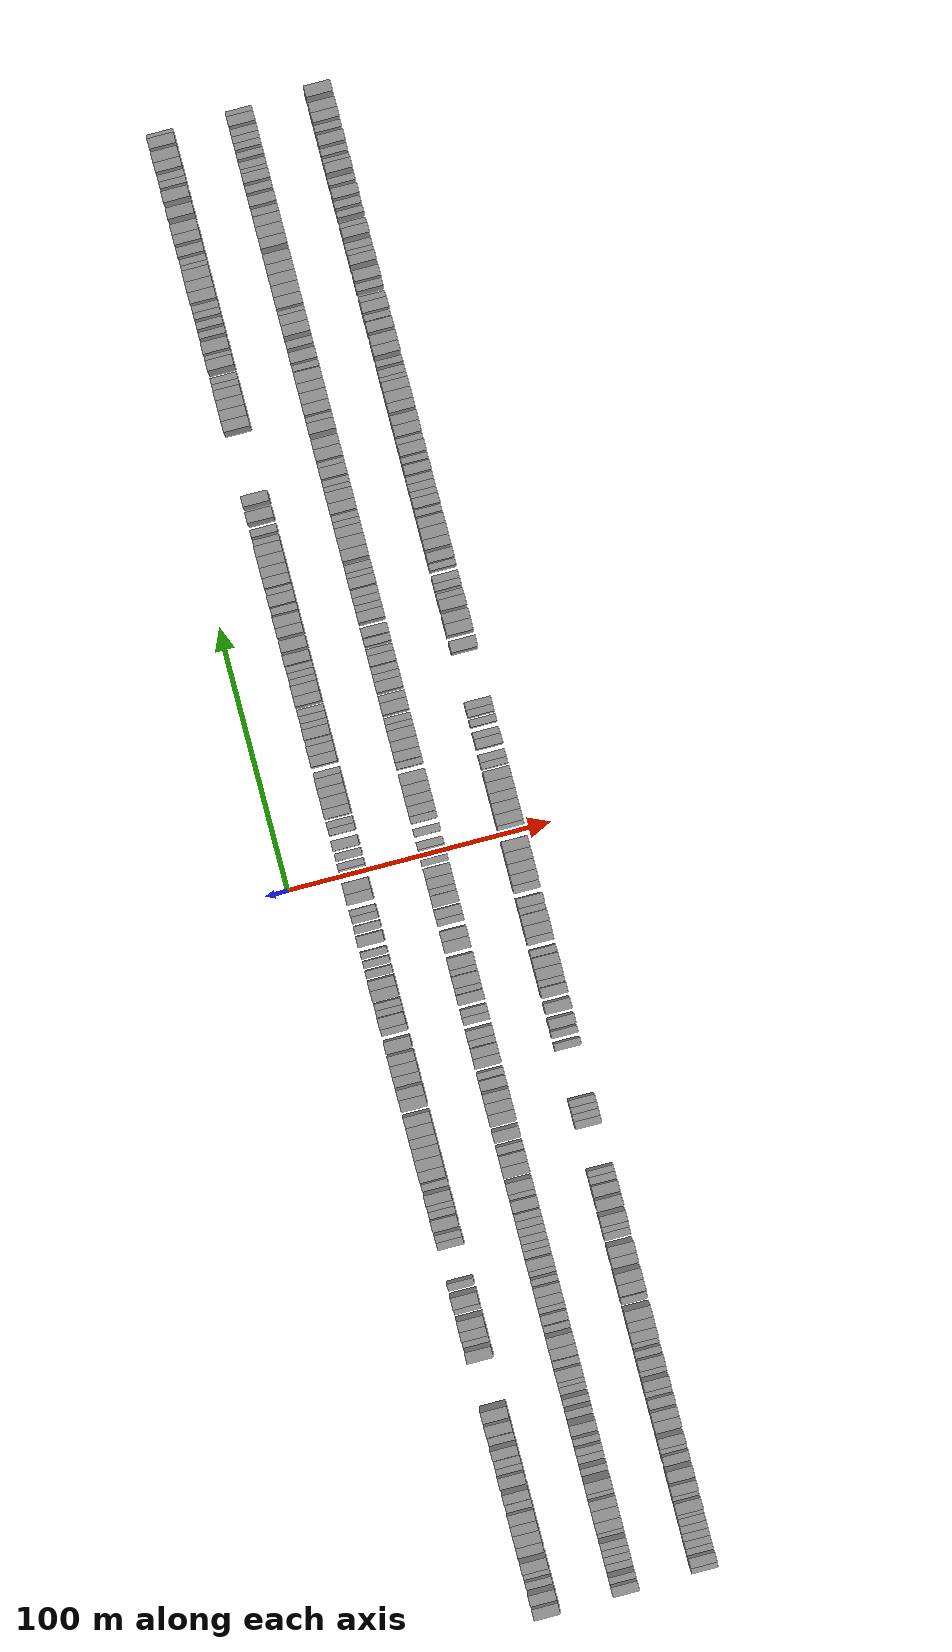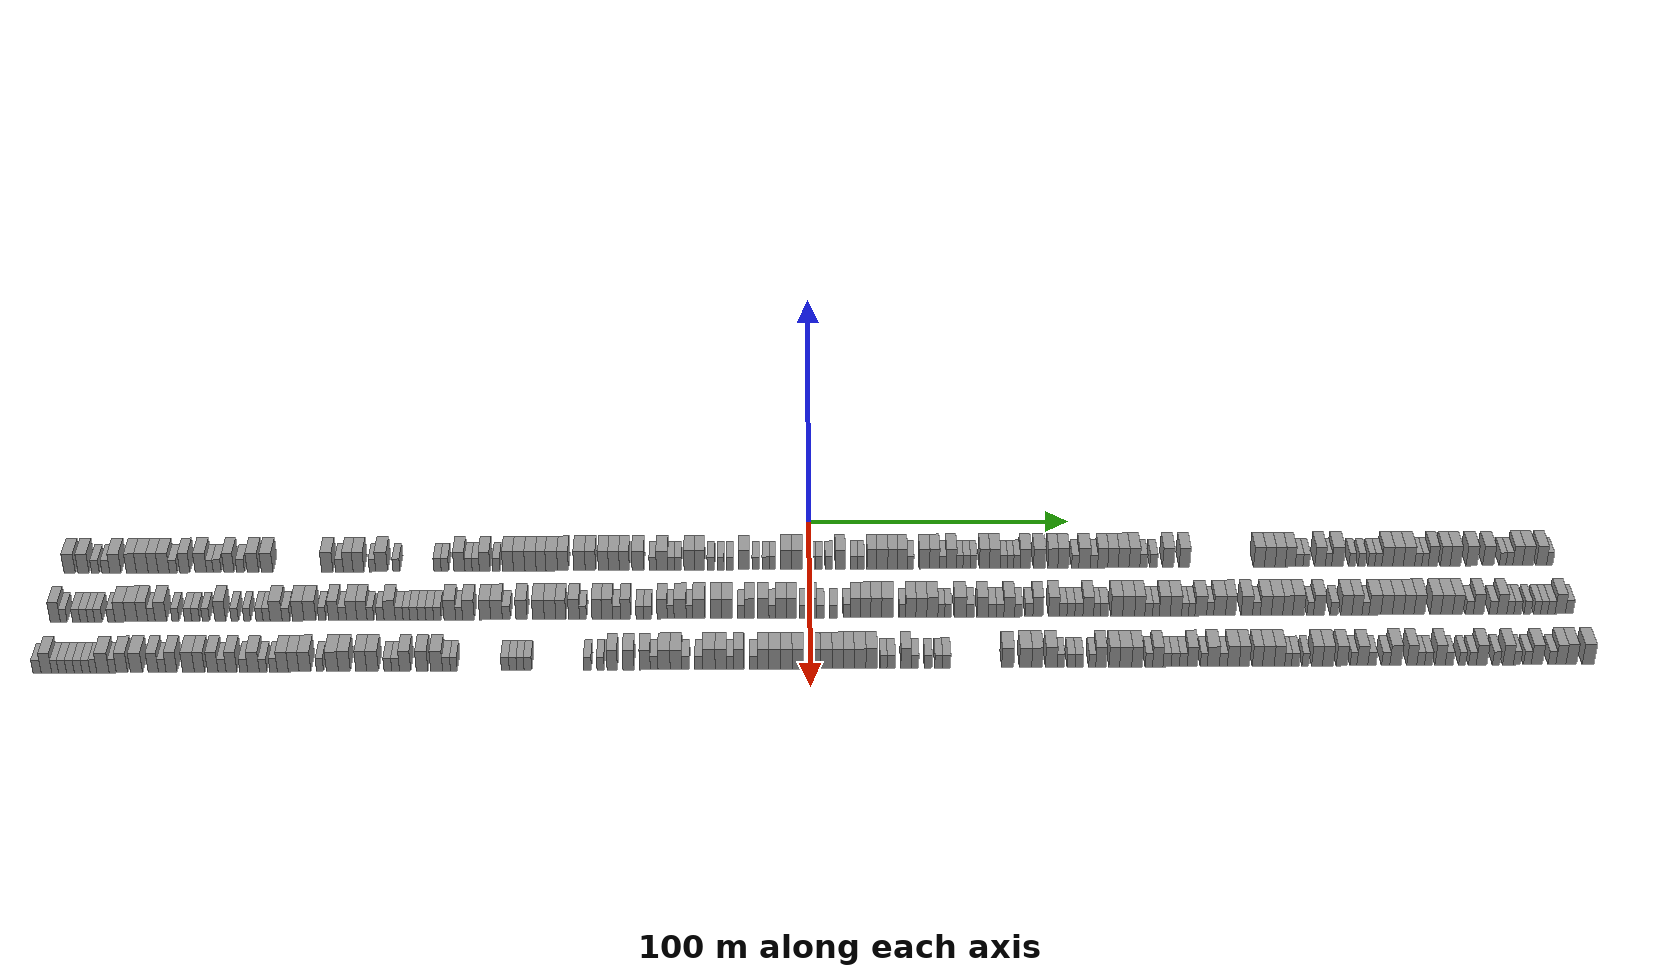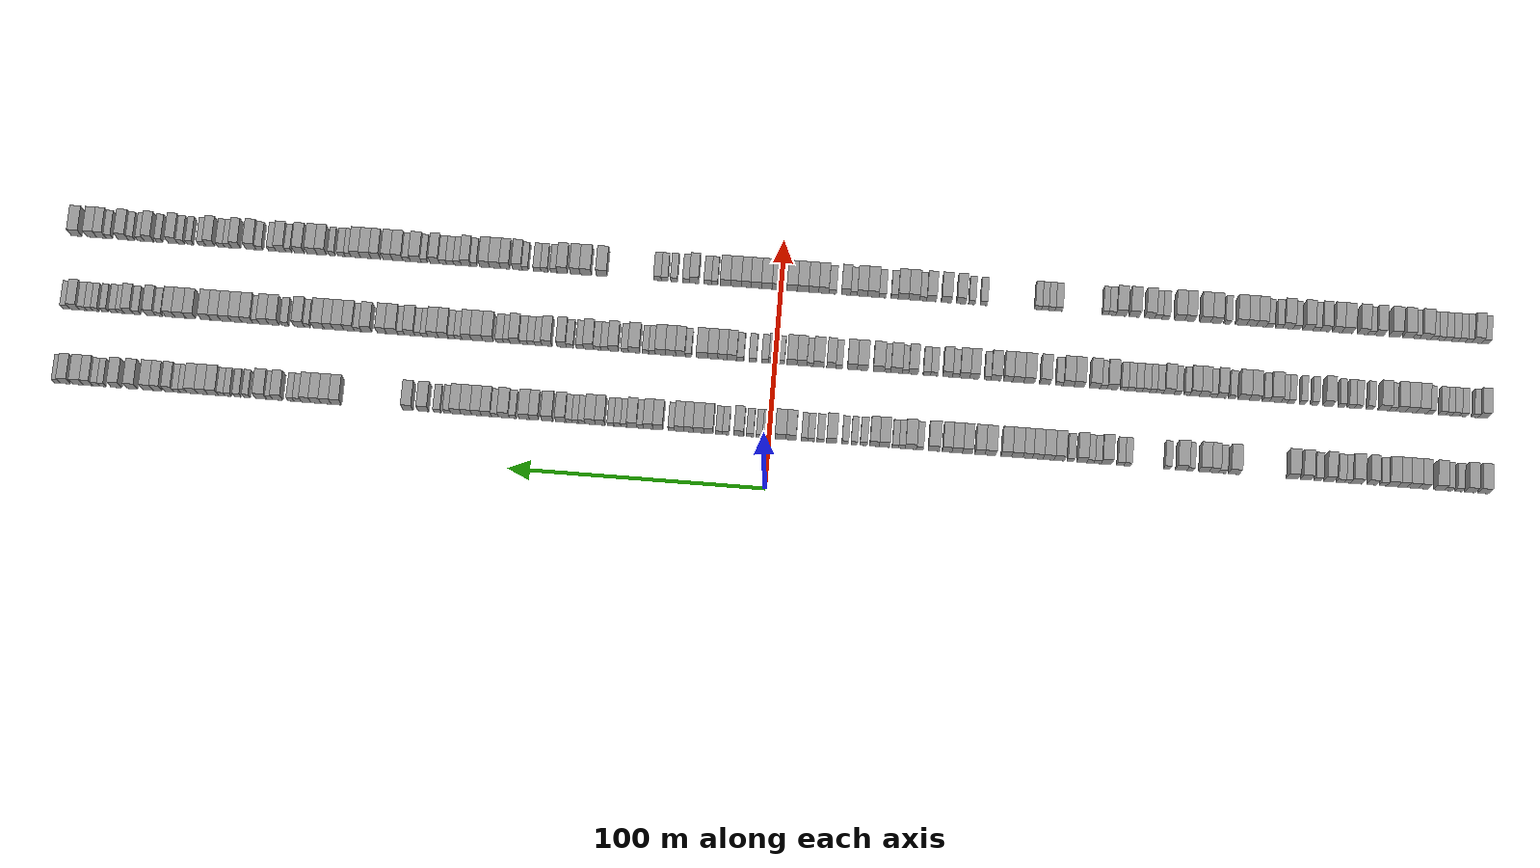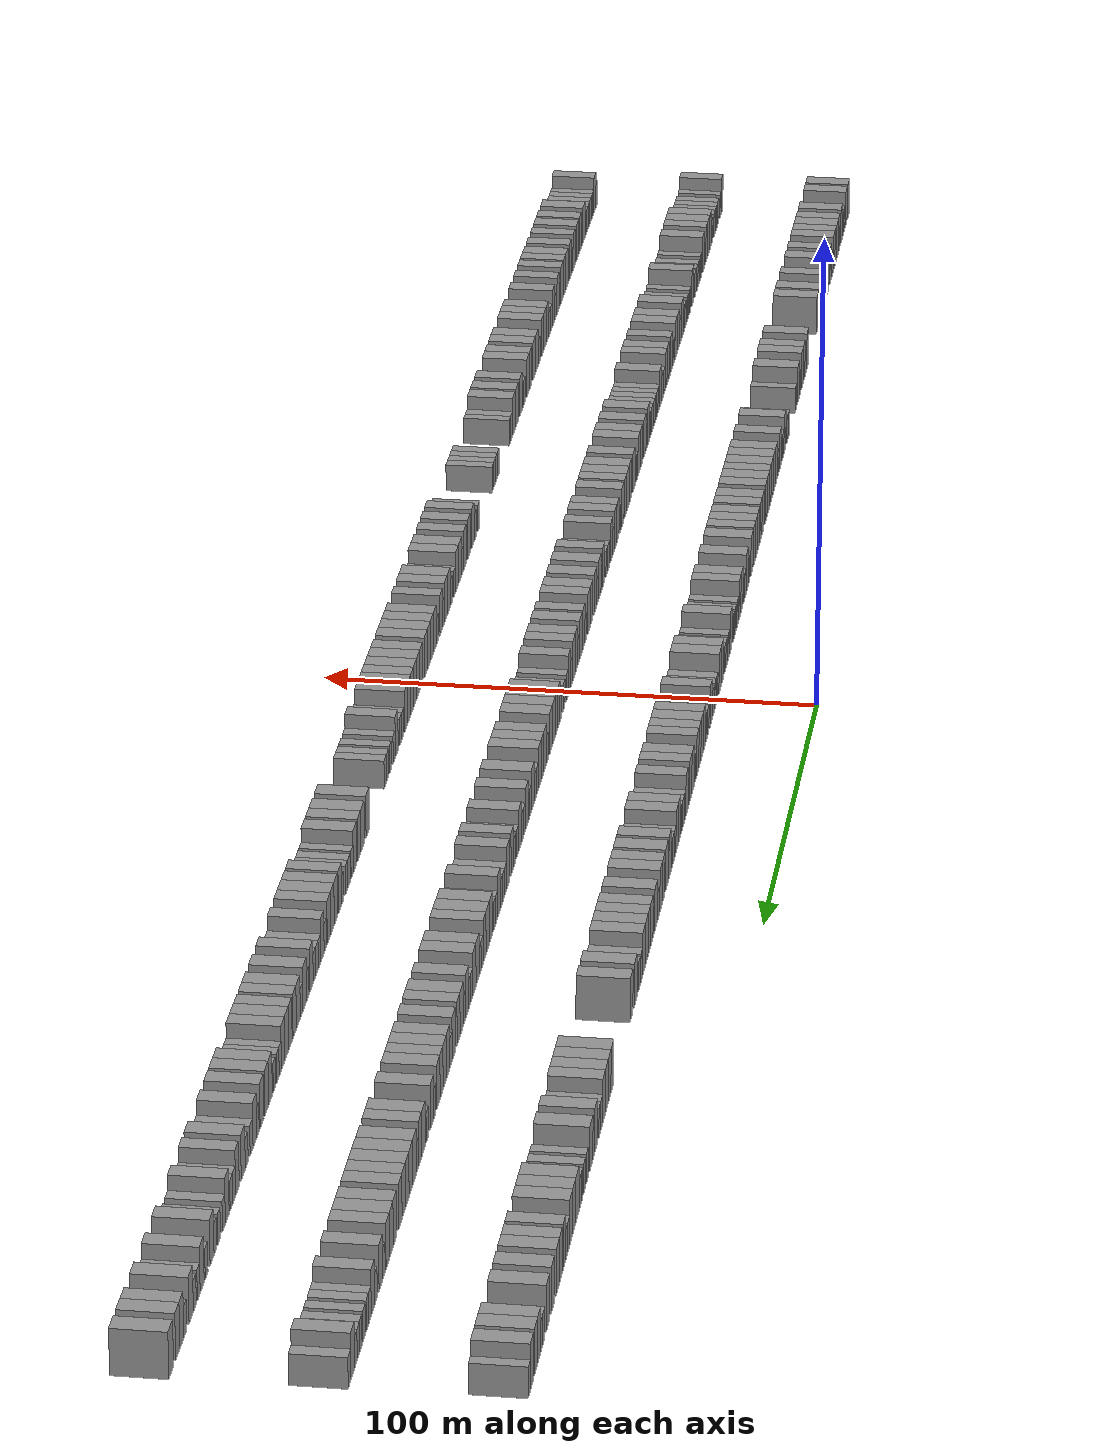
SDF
<sdf version="1.6">
 <world name="default">
  <scene>
   <sky><clouds><speed>12</speed></clouds></sky>
   <ambient>0.4 0.4 0.4 1</ambient>
   <background>0.7 0.7 0.7 1</background>
   <shadows>1</shadows>
  </scene>
  <gravity>0 0 -9.8066</gravity>
  <magnetic_field>6e-06 2.3e-05 -4.2e-05</magnetic_field>
  <physics default="0" name="default_physics" type="ode">
   <ode>
    <solver>
     <type>quick</type>
     <iters>10</iters>
     <sor>1.0</sor>
     <use_dynamic_moi_rescaling>0</use_dynamic_moi_rescaling>
    </solver>
    <constraints>
     <cfm>0</cfm>
     <erp>0.2</erp>
     <contact_max_correcting_vel>100</contact_max_correcting_vel>
     <contact_surface_layer>0.001</contact_surface_layer>
    </constraints>
   </ode>
   <max_step_size>0.004</max_step_size>
   <real_time_factor>1</real_time_factor>
   <real_time_update_rate>250</real_time_update_rate>
  </physics>
  <light name="sun" type="directional">
   <pose>0 0 10 0 0 0</pose>
   <diffuse>0.8 0.8 0.8 1</diffuse>
   <specular>0.2 0.2 0.2 1</specular>
   <attenuation>
    <range>1000</range>
    <constant>0.9</constant>
    <linear>0.01</linear>
    <quadratic>0.001</quadratic>
   </attenuation>
   <direction>-0.5 0.1 -0.9</direction>
  </light>
  <model name="building_1">
   <static>1</static>
   <pose>25.0000 -277.8792 0 0.000000 0.000000 0.000000</pose>
   <link name="link">
    <pose>0 0 4.50 0 0 0</pose>
    <collision name="collision"><geometry><box><size>10.0000 4.2417 9.0000</size></box></geometry></collision>
    <visual name="visual">
     <cast_shadows>0</cast_shadows>
     <geometry><box><size>10.0000 4.2417 9.0000</size></box></geometry>
     <material>
      <script>
       <uri>model://grey_wall/materials/scripts</uri>
       <uri>model://grey_wall/materials/textures</uri>
       <name>vrc/grey_wall</name>
      </script>
     </material>
    </visual>
   </link>
  </model>
  <model name="building_2">
   <static>1</static>
   <pose>25.0000 -272.6916 0 0.000000 0.000000 0.000000</pose>
   <link name="link">
    <pose>0 0 4.50 0 0 0</pose>
    <collision name="collision"><geometry><box><size>10.0000 4.1333 9.0000</size></box></geometry></collision>
    <visual name="visual">
     <cast_shadows>0</cast_shadows>
     <geometry><box><size>10.0000 4.1333 9.0000</size></box></geometry>
     <material>
      <script>
       <uri>model://grey_wall/materials/scripts</uri>
       <uri>model://grey_wall/materials/textures</uri>
       <name>vrc/grey_wall</name>
      </script>
     </material>
    </visual>
   </link>
  </model>
  <model name="building_3">
   <static>1</static>
   <pose>25.0000 -268.2089 0 0.000000 0.000000 0.000000</pose>
   <link name="link">
    <pose>0 0 3.00 0 0 0</pose>
    <collision name="collision"><geometry><box><size>10.0000 2.8322 6.0000</size></box></geometry></collision>
    <visual name="visual">
     <cast_shadows>0</cast_shadows>
     <geometry><box><size>10.0000 2.8322 6.0000</size></box></geometry>
     <material>
      <script>
       <uri>model://grey_wall/materials/scripts</uri>
       <uri>model://grey_wall/materials/textures</uri>
       <name>vrc/grey_wall</name>
      </script>
     </material>
    </visual>
   </link>
  </model>
  <model name="building_4">
   <static>1</static>
   <pose>25.0000 -264.3238 0 0.000000 0.000000 0.000000</pose>
   <link name="link">
    <pose>0 0 3.00 0 0 0</pose>
    <collision name="collision"><geometry><box><size>10.0000 2.9380 6.0000</size></box></geometry></collision>
    <visual name="visual">
     <cast_shadows>0</cast_shadows>
     <geometry><box><size>10.0000 2.9380 6.0000</size></box></geometry>
     <material>
      <script>
       <uri>model://grey_wall/materials/scripts</uri>
       <uri>model://grey_wall/materials/textures</uri>
       <name>vrc/grey_wall</name>
      </script>
     </material>
    </visual>
   </link>
  </model>
  <model name="building_5">
   <static>1</static>
   <pose>25.0000 -260.7361 0 0.000000 0.000000 0.000000</pose>
   <link name="link">
    <pose>0 0 4.50 0 0 0</pose>
    <collision name="collision"><geometry><box><size>10.0000 4.2375 9.0000</size></box></geometry></collision>
    <visual name="visual">
     <cast_shadows>0</cast_shadows>
     <geometry><box><size>10.0000 4.2375 9.0000</size></box></geometry>
     <material>
      <script>
       <uri>model://grey_wall/materials/scripts</uri>
       <uri>model://grey_wall/materials/textures</uri>
       <name>vrc/grey_wall</name>
      </script>
     </material>
    </visual>
   </link>
  </model>
  <model name="building_6">
   <static>1</static>
   <pose>25.0000 -254.7386 0 0.000000 0.000000 0.000000</pose>
   <link name="link">
    <pose>0 0 4.50 0 0 0</pose>
    <collision name="collision"><geometry><box><size>10.0000 3.7576 9.0000</size></box></geometry></collision>
    <visual name="visual">
     <cast_shadows>0</cast_shadows>
     <geometry><box><size>10.0000 3.7576 9.0000</size></box></geometry>
     <material>
      <script>
       <uri>model://grey_wall/materials/scripts</uri>
       <uri>model://grey_wall/materials/textures</uri>
       <name>vrc/grey_wall</name>
      </script>
     </material>
    </visual>
   </link>
  </model>
  <model name="building_7">
   <static>1</static>
   <pose>25.0000 -250.6340 0 0.000000 0.000000 0.000000</pose>
   <link name="link">
    <pose>0 0 4.50 0 0 0</pose>
    <collision name="collision"><geometry><box><size>10.0000 4.4515 9.0000</size></box></geometry></collision>
    <visual name="visual">
     <cast_shadows>0</cast_shadows>
     <geometry><box><size>10.0000 4.4515 9.0000</size></box></geometry>
     <material>
      <script>
       <uri>model://grey_wall/materials/scripts</uri>
       <uri>model://grey_wall/materials/textures</uri>
       <name>vrc/grey_wall</name>
      </script>
     </material>
    </visual>
   </link>
  </model>
  <model name="building_8">
   <static>1</static>
   <pose>25.0000 -246.5620 0 0.000000 0.000000 0.000000</pose>
   <link name="link">
    <pose>0 0 4.50 0 0 0</pose>
    <collision name="collision"><geometry><box><size>10.0000 3.6925 9.0000</size></box></geometry></collision>
    <visual name="visual">
     <cast_shadows>0</cast_shadows>
     <geometry><box><size>10.0000 3.6925 9.0000</size></box></geometry>
     <material>
      <script>
       <uri>model://grey_wall/materials/scripts</uri>
       <uri>model://grey_wall/materials/textures</uri>
       <name>vrc/grey_wall</name>
      </script>
     </material>
    </visual>
   </link>
  </model>
  <model name="building_9">
   <static>1</static>
   <pose>25.0000 -242.6047 0 0.000000 0.000000 0.000000</pose>
   <link name="link">
    <pose>0 0 4.50 0 0 0</pose>
    <collision name="collision"><geometry><box><size>10.0000 4.2221 9.0000</size></box></geometry></collision>
    <visual name="visual">
     <cast_shadows>0</cast_shadows>
     <geometry><box><size>10.0000 4.2221 9.0000</size></box></geometry>
     <material>
      <script>
       <uri>model://grey_wall/materials/scripts</uri>
       <uri>model://grey_wall/materials/textures</uri>
       <name>vrc/grey_wall</name>
      </script>
     </material>
    </visual>
   </link>
  </model>
  <model name="building_10">
   <static>1</static>
   <pose>25.0000 -239.0274 0 0.000000 0.000000 0.000000</pose>
   <link name="link">
    <pose>0 0 3.00 0 0 0</pose>
    <collision name="collision"><geometry><box><size>10.0000 2.9325 6.0000</size></box></geometry></collision>
    <visual name="visual">
     <cast_shadows>0</cast_shadows>
     <geometry><box><size>10.0000 2.9325 6.0000</size></box></geometry>
     <material>
      <script>
       <uri>model://grey_wall/materials/scripts</uri>
       <uri>model://grey_wall/materials/textures</uri>
       <name>vrc/grey_wall</name>
      </script>
     </material>
    </visual>
   </link>
  </model>
  <model name="building_11">
   <static>1</static>
   <pose>25.0000 -234.6927 0 0.000000 0.000000 0.000000</pose>
   <link name="link">
    <pose>0 0 4.50 0 0 0</pose>
    <collision name="collision"><geometry><box><size>10.0000 3.7369 9.0000</size></box></geometry></collision>
    <visual name="visual">
     <cast_shadows>0</cast_shadows>
     <geometry><box><size>10.0000 3.7369 9.0000</size></box></geometry>
     <material>
      <script>
       <uri>model://grey_wall/materials/scripts</uri>
       <uri>model://grey_wall/materials/textures</uri>
       <name>vrc/grey_wall</name>
      </script>
     </material>
    </visual>
   </link>
  </model>
  <model name="building_12">
   <static>1</static>
   <pose>25.0000 -228.6443 0 0.000000 0.000000 0.000000</pose>
   <link name="link">
    <pose>0 0 4.50 0 0 0</pose>
    <collision name="collision"><geometry><box><size>10.0000 4.3599 9.0000</size></box></geometry></collision>
    <visual name="visual">
     <cast_shadows>0</cast_shadows>
     <geometry><box><size>10.0000 4.3599 9.0000</size></box></geometry>
     <material>
      <script>
       <uri>model://grey_wall/materials/scripts</uri>
       <uri>model://grey_wall/materials/textures</uri>
       <name>vrc/grey_wall</name>
      </script>
     </material>
    </visual>
   </link>
  </model>
  <model name="building_13">
   <static>1</static>
   <pose>25.0000 -225.2310 0 0.000000 0.000000 0.000000</pose>
   <link name="link">
    <pose>0 0 3.00 0 0 0</pose>
    <collision name="collision"><geometry><box><size>10.0000 2.4668 6.0000</size></box></geometry></collision>
    <visual name="visual">
     <cast_shadows>0</cast_shadows>
     <geometry><box><size>10.0000 2.4668 6.0000</size></box></geometry>
     <material>
      <script>
       <uri>model://grey_wall/materials/scripts</uri>
       <uri>model://grey_wall/materials/textures</uri>
       <name>vrc/grey_wall</name>
      </script>
     </material>
    </visual>
   </link>
  </model>
  <model name="building_14">
   <static>1</static>
   <pose>25.0000 -222.5047 0 0.000000 0.000000 0.000000</pose>
   <link name="link">
    <pose>0 0 3.00 0 0 0</pose>
    <collision name="collision"><geometry><box><size>10.0000 2.9858 6.0000</size></box></geometry></collision>
    <visual name="visual">
     <cast_shadows>0</cast_shadows>
     <geometry><box><size>10.0000 2.9858 6.0000</size></box></geometry>
     <material>
      <script>
       <uri>model://grey_wall/materials/scripts</uri>
       <uri>model://grey_wall/materials/textures</uri>
       <name>vrc/grey_wall</name>
      </script>
     </material>
    </visual>
   </link>
  </model>
  <model name="building_15">
   <static>1</static>
   <pose>25.0000 -218.1075 0 0.000000 0.000000 0.000000</pose>
   <link name="link">
    <pose>0 0 4.50 0 0 0</pose>
    <collision name="collision"><geometry><box><size>10.0000 3.8086 9.0000</size></box></geometry></collision>
    <visual name="visual">
     <cast_shadows>0</cast_shadows>
     <geometry><box><size>10.0000 3.8086 9.0000</size></box></geometry>
     <material>
      <script>
       <uri>model://grey_wall/materials/scripts</uri>
       <uri>model://grey_wall/materials/textures</uri>
       <name>vrc/grey_wall</name>
      </script>
     </material>
    </visual>
   </link>
  </model>
  <model name="building_16">
   <static>1</static>
   <pose>25.0000 -213.7368 0 0.000000 0.000000 0.000000</pose>
   <link name="link">
    <pose>0 0 3.00 0 0 0</pose>
    <collision name="collision"><geometry><box><size>10.0000 2.9328 6.0000</size></box></geometry></collision>
    <visual name="visual">
     <cast_shadows>0</cast_shadows>
     <geometry><box><size>10.0000 2.9328 6.0000</size></box></geometry>
     <material>
      <script>
       <uri>model://grey_wall/materials/scripts</uri>
       <uri>model://grey_wall/materials/textures</uri>
       <name>vrc/grey_wall</name>
      </script>
     </material>
    </visual>
   </link>
  </model>
  <model name="building_17">
   <static>1</static>
   <pose>25.0000 -209.1297 0 0.000000 0.000000 0.000000</pose>
   <link name="link">
    <pose>0 0 4.50 0 0 0</pose>
    <collision name="collision"><geometry><box><size>10.0000 4.2814 9.0000</size></box></geometry></collision>
    <visual name="visual">
     <cast_shadows>0</cast_shadows>
     <geometry><box><size>10.0000 4.2814 9.0000</size></box></geometry>
     <material>
      <script>
       <uri>model://grey_wall/materials/scripts</uri>
       <uri>model://grey_wall/materials/textures</uri>
       <name>vrc/grey_wall</name>
      </script>
     </material>
    </visual>
   </link>
  </model>
  <model name="building_18">
   <static>1</static>
   <pose>25.0000 -203.7977 0 0.000000 0.000000 0.000000</pose>
   <link name="link">
    <pose>0 0 4.50 0 0 0</pose>
    <collision name="collision"><geometry><box><size>10.0000 4.3825 9.0000</size></box></geometry></collision>
    <visual name="visual">
     <cast_shadows>0</cast_shadows>
     <geometry><box><size>10.0000 4.3825 9.0000</size></box></geometry>
     <material>
      <script>
       <uri>model://grey_wall/materials/scripts</uri>
       <uri>model://grey_wall/materials/textures</uri>
       <name>vrc/grey_wall</name>
      </script>
     </material>
    </visual>
   </link>
  </model>
  <model name="building_19">
   <static>1</static>
   <pose>25.0000 -181.2089 0 0.000000 0.000000 0.000000</pose>
   <link name="link">
    <pose>0 0 4.50 0 0 0</pose>
    <collision name="collision"><geometry><box><size>10.0000 4.2651 9.0000</size></box></geometry></collision>
    <visual name="visual">
     <cast_shadows>0</cast_shadows>
     <geometry><box><size>10.0000 4.2651 9.0000</size></box></geometry>
     <material>
      <script>
       <uri>model://grey_wall/materials/scripts</uri>
       <uri>model://grey_wall/materials/textures</uri>
       <name>vrc/grey_wall</name>
      </script>
     </material>
    </visual>
   </link>
  </model>
  <model name="building_20">
   <static>1</static>
   <pose>25.0000 -176.6187 0 0.000000 0.000000 0.000000</pose>
   <link name="link">
    <pose>0 0 3.00 0 0 0</pose>
    <collision name="collision"><geometry><box><size>10.0000 2.9152 6.0000</size></box></geometry></collision>
    <visual name="visual">
     <cast_shadows>0</cast_shadows>
     <geometry><box><size>10.0000 2.9152 6.0000</size></box></geometry>
     <material>
      <script>
       <uri>model://grey_wall/materials/scripts</uri>
       <uri>model://grey_wall/materials/textures</uri>
       <name>vrc/grey_wall</name>
      </script>
     </material>
    </visual>
   </link>
  </model>
  <model name="building_21">
   <static>1</static>
   <pose>25.0000 -173.3480 0 0.000000 0.000000 0.000000</pose>
   <link name="link">
    <pose>0 0 4.50 0 0 0</pose>
    <collision name="collision"><geometry><box><size>10.0000 3.6261 9.0000</size></box></geometry></collision>
    <visual name="visual">
     <cast_shadows>0</cast_shadows>
     <geometry><box><size>10.0000 3.6261 9.0000</size></box></geometry>
     <material>
      <script>
       <uri>model://grey_wall/materials/scripts</uri>
       <uri>model://grey_wall/materials/textures</uri>
       <name>vrc/grey_wall</name>
      </script>
     </material>
    </visual>
   </link>
  </model>
  <model name="building_22">
   <static>1</static>
   <pose>25.0000 -169.4924 0 0.000000 0.000000 0.000000</pose>
   <link name="link">
    <pose>0 0 4.50 0 0 0</pose>
    <collision name="collision"><geometry><box><size>10.0000 4.0851 9.0000</size></box></geometry></collision>
    <visual name="visual">
     <cast_shadows>0</cast_shadows>
     <geometry><box><size>10.0000 4.0851 9.0000</size></box></geometry>
     <material>
      <script>
       <uri>model://grey_wall/materials/scripts</uri>
       <uri>model://grey_wall/materials/textures</uri>
       <name>vrc/grey_wall</name>
      </script>
     </material>
    </visual>
   </link>
  </model>
  <model name="building_23">
   <static>1</static>
   <pose>25.0000 -164.2421 0 0.000000 0.000000 0.000000</pose>
   <link name="link">
    <pose>0 0 3.00 0 0 0</pose>
    <collision name="collision"><geometry><box><size>10.0000 2.4156 6.0000</size></box></geometry></collision>
    <visual name="visual">
     <cast_shadows>0</cast_shadows>
     <geometry><box><size>10.0000 2.4156 6.0000</size></box></geometry>
     <material>
      <script>
       <uri>model://grey_wall/materials/scripts</uri>
       <uri>model://grey_wall/materials/textures</uri>
       <name>vrc/grey_wall</name>
      </script>
     </material>
    </visual>
   </link>
  </model>
  <model name="building_24">
   <static>1</static>
   <pose>25.0000 -160.7934 0 0.000000 0.000000 0.000000</pose>
   <link name="link">
    <pose>0 0 4.50 0 0 0</pose>
    <collision name="collision"><geometry><box><size>10.0000 4.4818 9.0000</size></box></geometry></collision>
    <visual name="visual">
     <cast_shadows>0</cast_shadows>
     <geometry><box><size>10.0000 4.4818 9.0000</size></box></geometry>
     <material>
      <script>
       <uri>model://grey_wall/materials/scripts</uri>
       <uri>model://grey_wall/materials/textures</uri>
       <name>vrc/grey_wall</name>
      </script>
     </material>
    </visual>
   </link>
  </model>
  <model name="building_25">
   <static>1</static>
   <pose>25.0000 -155.2299 0 0.000000 0.000000 0.000000</pose>
   <link name="link">
    <pose>0 0 3.00 0 0 0</pose>
    <collision name="collision"><geometry><box><size>10.0000 2.6451 6.0000</size></box></geometry></collision>
    <visual name="visual">
     <cast_shadows>0</cast_shadows>
     <geometry><box><size>10.0000 2.6451 6.0000</size></box></geometry>
     <material>
      <script>
       <uri>model://grey_wall/materials/scripts</uri>
       <uri>model://grey_wall/materials/textures</uri>
       <name>vrc/grey_wall</name>
      </script>
     </material>
    </visual>
   </link>
  </model>
  <model name="building_26">
   <static>1</static>
   <pose>25.0000 -139.7880 0 0.000000 0.000000 0.000000</pose>
   <link name="link">
    <pose>0 0 3.00 0 0 0</pose>
    <collision name="collision"><geometry><box><size>10.0000 2.7462 6.0000</size></box></geometry></collision>
    <visual name="visual">
     <cast_shadows>0</cast_shadows>
     <geometry><box><size>10.0000 2.7462 6.0000</size></box></geometry>
     <material>
      <script>
       <uri>model://grey_wall/materials/scripts</uri>
       <uri>model://grey_wall/materials/textures</uri>
       <name>vrc/grey_wall</name>
      </script>
     </material>
    </visual>
   </link>
  </model>
  <model name="building_27">
   <static>1</static>
   <pose>25.0000 -137.0259 0 0.000000 0.000000 0.000000</pose>
   <link name="link">
    <pose>0 0 3.00 0 0 0</pose>
    <collision name="collision"><geometry><box><size>10.0000 2.7780 6.0000</size></box></geometry></collision>
    <visual name="visual">
     <cast_shadows>0</cast_shadows>
     <geometry><box><size>10.0000 2.7780 6.0000</size></box></geometry>
     <material>
      <script>
       <uri>model://grey_wall/materials/scripts</uri>
       <uri>model://grey_wall/materials/textures</uri>
       <name>vrc/grey_wall</name>
      </script>
     </material>
    </visual>
   </link>
  </model>
  <model name="building_28">
   <static>1</static>
   <pose>25.0000 -131.5813 0 0.000000 0.000000 0.000000</pose>
   <link name="link">
    <pose>0 0 4.50 0 0 0</pose>
    <collision name="collision"><geometry><box><size>10.0000 4.1113 9.0000</size></box></geometry></collision>
    <visual name="visual">
     <cast_shadows>0</cast_shadows>
     <geometry><box><size>10.0000 4.1113 9.0000</size></box></geometry>
     <material>
      <script>
       <uri>model://grey_wall/materials/scripts</uri>
       <uri>model://grey_wall/materials/textures</uri>
       <name>vrc/grey_wall</name>
      </script>
     </material>
    </visual>
   </link>
  </model>
  <model name="building_29">
   <static>1</static>
   <pose>25.0000 -128.1571 0 0.000000 0.000000 0.000000</pose>
   <link name="link">
    <pose>0 0 3.00 0 0 0</pose>
    <collision name="collision"><geometry><box><size>10.0000 2.7370 6.0000</size></box></geometry></collision>
    <visual name="visual">
     <cast_shadows>0</cast_shadows>
     <geometry><box><size>10.0000 2.7370 6.0000</size></box></geometry>
     <material>
      <script>
       <uri>model://grey_wall/materials/scripts</uri>
       <uri>model://grey_wall/materials/textures</uri>
       <name>vrc/grey_wall</name>
      </script>
     </material>
    </visual>
   </link>
  </model>
  <model name="building_30">
   <static>1</static>
   <pose>25.0000 -125.4257 0 0.000000 0.000000 0.000000</pose>
   <link name="link">
    <pose>0 0 3.00 0 0 0</pose>
    <collision name="collision"><geometry><box><size>10.0000 2.7259 6.0000</size></box></geometry></collision>
    <visual name="visual">
     <cast_shadows>0</cast_shadows>
     <geometry><box><size>10.0000 2.7259 6.0000</size></box></geometry>
     <material>
      <script>
       <uri>model://grey_wall/materials/scripts</uri>
       <uri>model://grey_wall/materials/textures</uri>
       <name>vrc/grey_wall</name>
      </script>
     </material>
    </visual>
   </link>
  </model>
  <model name="building_31">
   <static>1</static>
   <pose>25.0000 -122.0370 0 0.000000 0.000000 0.000000</pose>
   <link name="link">
    <pose>0 0 4.50 0 0 0</pose>
    <collision name="collision"><geometry><box><size>10.0000 4.0514 9.0000</size></box></geometry></collision>
    <visual name="visual">
     <cast_shadows>0</cast_shadows>
     <geometry><box><size>10.0000 4.0514 9.0000</size></box></geometry>
     <material>
      <script>
       <uri>model://grey_wall/materials/scripts</uri>
       <uri>model://grey_wall/materials/textures</uri>
       <name>vrc/grey_wall</name>
      </script>
     </material>
    </visual>
   </link>
  </model>
  <model name="building_32">
   <static>1</static>
   <pose>25.0000 -117.6676 0 0.000000 0.000000 0.000000</pose>
   <link name="link">
    <pose>0 0 3.00 0 0 0</pose>
    <collision name="collision"><geometry><box><size>10.0000 2.6874 6.0000</size></box></geometry></collision>
    <visual name="visual">
     <cast_shadows>0</cast_shadows>
     <geometry><box><size>10.0000 2.6874 6.0000</size></box></geometry>
     <material>
      <script>
       <uri>model://grey_wall/materials/scripts</uri>
       <uri>model://grey_wall/materials/textures</uri>
       <name>vrc/grey_wall</name>
      </script>
     </material>
    </visual>
   </link>
  </model>
  <model name="building_33">
   <static>1</static>
   <pose>25.0000 -113.2914 0 0.000000 0.000000 0.000000</pose>
   <link name="link">
    <pose>0 0 4.50 0 0 0</pose>
    <collision name="collision"><geometry><box><size>10.0000 4.0650 9.0000</size></box></geometry></collision>
    <visual name="visual">
     <cast_shadows>0</cast_shadows>
     <geometry><box><size>10.0000 4.0650 9.0000</size></box></geometry>
     <material>
      <script>
       <uri>model://grey_wall/materials/scripts</uri>
       <uri>model://grey_wall/materials/textures</uri>
       <name>vrc/grey_wall</name>
      </script>
     </material>
    </visual>
   </link>
  </model>
  <model name="building_34">
   <static>1</static>
   <pose>25.0000 -109.1173 0 0.000000 0.000000 0.000000</pose>
   <link name="link">
    <pose>0 0 4.50 0 0 0</pose>
    <collision name="collision"><geometry><box><size>10.0000 4.2831 9.0000</size></box></geometry></collision>
    <visual name="visual">
     <cast_shadows>0</cast_shadows>
     <geometry><box><size>10.0000 4.2831 9.0000</size></box></geometry>
     <material>
      <script>
       <uri>model://grey_wall/materials/scripts</uri>
       <uri>model://grey_wall/materials/textures</uri>
       <name>vrc/grey_wall</name>
      </script>
     </material>
    </visual>
   </link>
  </model>
  <model name="building_35">
   <static>1</static>
   <pose>25.0000 -104.8553 0 0.000000 0.000000 0.000000</pose>
   <link name="link">
    <pose>0 0 4.50 0 0 0</pose>
    <collision name="collision"><geometry><box><size>10.0000 4.2411 9.0000</size></box></geometry></collision>
    <visual name="visual">
     <cast_shadows>0</cast_shadows>
     <geometry><box><size>10.0000 4.2411 9.0000</size></box></geometry>
     <material>
      <script>
       <uri>model://grey_wall/materials/scripts</uri>
       <uri>model://grey_wall/materials/textures</uri>
       <name>vrc/grey_wall</name>
      </script>
     </material>
    </visual>
   </link>
  </model>
  <model name="building_36">
   <static>1</static>
   <pose>25.0000 -100.9008 0 0.000000 0.000000 0.000000</pose>
   <link name="link">
    <pose>0 0 4.50 0 0 0</pose>
    <collision name="collision"><geometry><box><size>10.0000 3.6677 9.0000</size></box></geometry></collision>
    <visual name="visual">
     <cast_shadows>0</cast_shadows>
     <geometry><box><size>10.0000 3.6677 9.0000</size></box></geometry>
     <material>
      <script>
       <uri>model://grey_wall/materials/scripts</uri>
       <uri>model://grey_wall/materials/textures</uri>
       <name>vrc/grey_wall</name>
      </script>
     </material>
    </visual>
   </link>
  </model>
  <model name="building_37">
   <static>1</static>
   <pose>25.0000 -96.8652 0 0.000000 0.000000 0.000000</pose>
   <link name="link">
    <pose>0 0 4.50 0 0 0</pose>
    <collision name="collision"><geometry><box><size>10.0000 4.4035 9.0000</size></box></geometry></collision>
    <visual name="visual">
     <cast_shadows>0</cast_shadows>
     <geometry><box><size>10.0000 4.4035 9.0000</size></box></geometry>
     <material>
      <script>
       <uri>model://grey_wall/materials/scripts</uri>
       <uri>model://grey_wall/materials/textures</uri>
       <name>vrc/grey_wall</name>
      </script>
     </material>
    </visual>
   </link>
  </model>
  <model name="building_38">
   <static>1</static>
   <pose>25.0000 -92.6300 0 0.000000 0.000000 0.000000</pose>
   <link name="link">
    <pose>0 0 4.50 0 0 0</pose>
    <collision name="collision"><geometry><box><size>10.0000 4.0669 9.0000</size></box></geometry></collision>
    <visual name="visual">
     <cast_shadows>0</cast_shadows>
     <geometry><box><size>10.0000 4.0669 9.0000</size></box></geometry>
     <material>
      <script>
       <uri>model://grey_wall/materials/scripts</uri>
       <uri>model://grey_wall/materials/textures</uri>
       <name>vrc/grey_wall</name>
      </script>
     </material>
    </visual>
   </link>
  </model>
  <model name="building_39">
   <static>1</static>
   <pose>25.0000 -86.4419 0 0.000000 0.000000 0.000000</pose>
   <link name="link">
    <pose>0 0 4.50 0 0 0</pose>
    <collision name="collision"><geometry><box><size>10.0000 4.3093 9.0000</size></box></geometry></collision>
    <visual name="visual">
     <cast_shadows>0</cast_shadows>
     <geometry><box><size>10.0000 4.3093 9.0000</size></box></geometry>
     <material>
      <script>
       <uri>model://grey_wall/materials/scripts</uri>
       <uri>model://grey_wall/materials/textures</uri>
       <name>vrc/grey_wall</name>
      </script>
     </material>
    </visual>
   </link>
  </model>
  <model name="building_40">
   <static>1</static>
   <pose>25.0000 -82.3162 0 0.000000 0.000000 0.000000</pose>
   <link name="link">
    <pose>0 0 4.50 0 0 0</pose>
    <collision name="collision"><geometry><box><size>10.0000 3.9421 9.0000</size></box></geometry></collision>
    <visual name="visual">
     <cast_shadows>0</cast_shadows>
     <geometry><box><size>10.0000 3.9421 9.0000</size></box></geometry>
     <material>
      <script>
       <uri>model://grey_wall/materials/scripts</uri>
       <uri>model://grey_wall/materials/textures</uri>
       <name>vrc/grey_wall</name>
      </script>
     </material>
    </visual>
   </link>
  </model>
  <model name="building_41">
   <static>1</static>
   <pose>25.0000 -77.4432 0 0.000000 0.000000 0.000000</pose>
   <link name="link">
    <pose>0 0 4.50 0 0 0</pose>
    <collision name="collision"><geometry><box><size>10.0000 3.8039 9.0000</size></box></geometry></collision>
    <visual name="visual">
     <cast_shadows>0</cast_shadows>
     <geometry><box><size>10.0000 3.8039 9.0000</size></box></geometry>
     <material>
      <script>
       <uri>model://grey_wall/materials/scripts</uri>
       <uri>model://grey_wall/materials/textures</uri>
       <name>vrc/grey_wall</name>
      </script>
     </material>
    </visual>
   </link>
  </model>
  <model name="building_42">
   <static>1</static>
   <pose>25.0000 -73.4997 0 0.000000 0.000000 0.000000</pose>
   <link name="link">
    <pose>0 0 4.50 0 0 0</pose>
    <collision name="collision"><geometry><box><size>10.0000 4.0831 9.0000</size></box></geometry></collision>
    <visual name="visual">
     <cast_shadows>0</cast_shadows>
     <geometry><box><size>10.0000 4.0831 9.0000</size></box></geometry>
     <material>
      <script>
       <uri>model://grey_wall/materials/scripts</uri>
       <uri>model://grey_wall/materials/textures</uri>
       <name>vrc/grey_wall</name>
      </script>
     </material>
    </visual>
   </link>
  </model>
  <model name="building_43">
   <static>1</static>
   <pose>25.0000 -69.5776 0 0.000000 0.000000 0.000000</pose>
   <link name="link">
    <pose>0 0 4.50 0 0 0</pose>
    <collision name="collision"><geometry><box><size>10.0000 3.7611 9.0000</size></box></geometry></collision>
    <visual name="visual">
     <cast_shadows>0</cast_shadows>
     <geometry><box><size>10.0000 3.7611 9.0000</size></box></geometry>
     <material>
      <script>
       <uri>model://grey_wall/materials/scripts</uri>
       <uri>model://grey_wall/materials/textures</uri>
       <name>vrc/grey_wall</name>
      </script>
     </material>
    </visual>
   </link>
  </model>
  <model name="building_44">
   <static>1</static>
   <pose>25.0000 -64.4506 0 0.000000 0.000000 0.000000</pose>
   <link name="link">
    <pose>0 0 4.50 0 0 0</pose>
    <collision name="collision"><geometry><box><size>10.0000 4.4929 9.0000</size></box></geometry></collision>
    <visual name="visual">
     <cast_shadows>0</cast_shadows>
     <geometry><box><size>10.0000 4.4929 9.0000</size></box></geometry>
     <material>
      <script>
       <uri>model://grey_wall/materials/scripts</uri>
       <uri>model://grey_wall/materials/textures</uri>
       <name>vrc/grey_wall</name>
      </script>
     </material>
    </visual>
   </link>
  </model>
  <model name="building_45">
   <static>1</static>
   <pose>25.0000 -58.8808 0 0.000000 0.000000 0.000000</pose>
   <link name="link">
    <pose>0 0 3.00 0 0 0</pose>
    <collision name="collision"><geometry><box><size>10.0000 2.6467 6.0000</size></box></geometry></collision>
    <visual name="visual">
     <cast_shadows>0</cast_shadows>
     <geometry><box><size>10.0000 2.6467 6.0000</size></box></geometry>
     <material>
      <script>
       <uri>model://grey_wall/materials/scripts</uri>
       <uri>model://grey_wall/materials/textures</uri>
       <name>vrc/grey_wall</name>
      </script>
     </material>
    </visual>
   </link>
  </model>
  <model name="building_46">
   <static>1</static>
   <pose>25.0000 -55.3931 0 0.000000 0.000000 0.000000</pose>
   <link name="link">
    <pose>0 0 4.50 0 0 0</pose>
    <collision name="collision"><geometry><box><size>10.0000 4.3287 9.0000</size></box></geometry></collision>
    <visual name="visual">
     <cast_shadows>0</cast_shadows>
     <geometry><box><size>10.0000 4.3287 9.0000</size></box></geometry>
     <material>
      <script>
       <uri>model://grey_wall/materials/scripts</uri>
       <uri>model://grey_wall/materials/textures</uri>
       <name>vrc/grey_wall</name>
      </script>
     </material>
    </visual>
   </link>
  </model>
  <model name="building_47">
   <static>1</static>
   <pose>25.0000 -51.9567 0 0.000000 0.000000 0.000000</pose>
   <link name="link">
    <pose>0 0 3.00 0 0 0</pose>
    <collision name="collision"><geometry><box><size>10.0000 2.5442 6.0000</size></box></geometry></collision>
    <visual name="visual">
     <cast_shadows>0</cast_shadows>
     <geometry><box><size>10.0000 2.5442 6.0000</size></box></geometry>
     <material>
      <script>
       <uri>model://grey_wall/materials/scripts</uri>
       <uri>model://grey_wall/materials/textures</uri>
       <name>vrc/grey_wall</name>
      </script>
     </material>
    </visual>
   </link>
  </model>
  <model name="building_48">
   <static>1</static>
   <pose>25.0000 -49.4070 0 0.000000 0.000000 0.000000</pose>
   <link name="link">
    <pose>0 0 3.00 0 0 0</pose>
    <collision name="collision"><geometry><box><size>10.0000 2.5553 6.0000</size></box></geometry></collision>
    <visual name="visual">
     <cast_shadows>0</cast_shadows>
     <geometry><box><size>10.0000 2.5553 6.0000</size></box></geometry>
     <material>
      <script>
       <uri>model://grey_wall/materials/scripts</uri>
       <uri>model://grey_wall/materials/textures</uri>
       <name>vrc/grey_wall</name>
      </script>
     </material>
    </visual>
   </link>
  </model>
  <model name="building_49">
   <static>1</static>
   <pose>25.0000 -45.0971 0 0.000000 0.000000 0.000000</pose>
   <link name="link">
    <pose>0 0 4.50 0 0 0</pose>
    <collision name="collision"><geometry><box><size>10.0000 4.0646 9.0000</size></box></geometry></collision>
    <visual name="visual">
     <cast_shadows>0</cast_shadows>
     <geometry><box><size>10.0000 4.0646 9.0000</size></box></geometry>
     <material>
      <script>
       <uri>model://grey_wall/materials/scripts</uri>
       <uri>model://grey_wall/materials/textures</uri>
       <name>vrc/grey_wall</name>
      </script>
     </material>
    </visual>
   </link>
  </model>
  <model name="building_50">
   <static>1</static>
   <pose>25.0000 -41.2417 0 0.000000 0.000000 0.000000</pose>
   <link name="link">
    <pose>0 0 4.50 0 0 0</pose>
    <collision name="collision"><geometry><box><size>10.0000 3.6462 9.0000</size></box></geometry></collision>
    <visual name="visual">
     <cast_shadows>0</cast_shadows>
     <geometry><box><size>10.0000 3.6462 9.0000</size></box></geometry>
     <material>
      <script>
       <uri>model://grey_wall/materials/scripts</uri>
       <uri>model://grey_wall/materials/textures</uri>
       <name>vrc/grey_wall</name>
      </script>
     </material>
    </visual>
   </link>
  </model>
  <model name="building_51">
   <static>1</static>
   <pose>25.0000 -37.0096 0 0.000000 0.000000 0.000000</pose>
   <link name="link">
    <pose>0 0 3.00 0 0 0</pose>
    <collision name="collision"><geometry><box><size>10.0000 2.8180 6.0000</size></box></geometry></collision>
    <visual name="visual">
     <cast_shadows>0</cast_shadows>
     <geometry><box><size>10.0000 2.8180 6.0000</size></box></geometry>
     <material>
      <script>
       <uri>model://grey_wall/materials/scripts</uri>
       <uri>model://grey_wall/materials/textures</uri>
       <name>vrc/grey_wall</name>
      </script>
     </material>
    </visual>
   </link>
  </model>
  <model name="building_52">
   <static>1</static>
   <pose>25.0000 -33.3293 0 0.000000 0.000000 0.000000</pose>
   <link name="link">
    <pose>0 0 3.00 0 0 0</pose>
    <collision name="collision"><geometry><box><size>10.0000 2.5426 6.0000</size></box></geometry></collision>
    <visual name="visual">
     <cast_shadows>0</cast_shadows>
     <geometry><box><size>10.0000 2.5426 6.0000</size></box></geometry>
     <material>
      <script>
       <uri>model://grey_wall/materials/scripts</uri>
       <uri>model://grey_wall/materials/textures</uri>
       <name>vrc/grey_wall</name>
      </script>
     </material>
    </visual>
   </link>
  </model>
  <model name="building_53">
   <static>1</static>
   <pose>25.0000 -29.7868 0 0.000000 0.000000 0.000000</pose>
   <link name="link">
    <pose>0 0 3.00 0 0 0</pose>
    <collision name="collision"><geometry><box><size>10.0000 2.5425 6.0000</size></box></geometry></collision>
    <visual name="visual">
     <cast_shadows>0</cast_shadows>
     <geometry><box><size>10.0000 2.5425 6.0000</size></box></geometry>
     <material>
      <script>
       <uri>model://grey_wall/materials/scripts</uri>
       <uri>model://grey_wall/materials/textures</uri>
       <name>vrc/grey_wall</name>
      </script>
     </material>
    </visual>
   </link>
  </model>
  <model name="building_54">
   <static>1</static>
   <pose>25.0000 -24.5192 0 0.000000 0.000000 0.000000</pose>
   <link name="link">
    <pose>0 0 4.50 0 0 0</pose>
    <collision name="collision"><geometry><box><size>10.0000 3.9926 9.0000</size></box></geometry></collision>
    <visual name="visual">
     <cast_shadows>0</cast_shadows>
     <geometry><box><size>10.0000 3.9926 9.0000</size></box></geometry>
     <material>
      <script>
       <uri>model://grey_wall/materials/scripts</uri>
       <uri>model://grey_wall/materials/textures</uri>
       <name>vrc/grey_wall</name>
      </script>
     </material>
    </visual>
   </link>
  </model>
  <model name="building_55">
   <static>1</static>
   <pose>25.0000 -20.1433 0 0.000000 0.000000 0.000000</pose>
   <link name="link">
    <pose>0 0 3.00 0 0 0</pose>
    <collision name="collision"><geometry><box><size>10.0000 2.7592 6.0000</size></box></geometry></collision>
    <visual name="visual">
     <cast_shadows>0</cast_shadows>
     <geometry><box><size>10.0000 2.7592 6.0000</size></box></geometry>
     <material>
      <script>
       <uri>model://grey_wall/materials/scripts</uri>
       <uri>model://grey_wall/materials/textures</uri>
       <name>vrc/grey_wall</name>
      </script>
     </material>
    </visual>
   </link>
  </model>
  <model name="building_56">
   <static>1</static>
   <pose>25.0000 -16.4435 0 0.000000 0.000000 0.000000</pose>
   <link name="link">
    <pose>0 0 3.00 0 0 0</pose>
    <collision name="collision"><geometry><box><size>10.0000 2.6403 6.0000</size></box></geometry></collision>
    <visual name="visual">
     <cast_shadows>0</cast_shadows>
     <geometry><box><size>10.0000 2.6403 6.0000</size></box></geometry>
     <material>
      <script>
       <uri>model://grey_wall/materials/scripts</uri>
       <uri>model://grey_wall/materials/textures</uri>
       <name>vrc/grey_wall</name>
      </script>
     </material>
    </visual>
   </link>
  </model>
  <model name="building_57">
   <static>1</static>
   <pose>25.0000 -13.8980 0 0.000000 0.000000 0.000000</pose>
   <link name="link">
    <pose>0 0 3.00 0 0 0</pose>
    <collision name="collision"><geometry><box><size>10.0000 2.4508 6.0000</size></box></geometry></collision>
    <visual name="visual">
     <cast_shadows>0</cast_shadows>
     <geometry><box><size>10.0000 2.4508 6.0000</size></box></geometry>
     <material>
      <script>
       <uri>model://grey_wall/materials/scripts</uri>
       <uri>model://grey_wall/materials/textures</uri>
       <name>vrc/grey_wall</name>
      </script>
     </material>
    </visual>
   </link>
  </model>
  <model name="building_58">
   <static>1</static>
   <pose>25.0000 -8.7240 0 0.000000 0.000000 0.000000</pose>
   <link name="link">
    <pose>0 0 4.50 0 0 0</pose>
    <collision name="collision"><geometry><box><size>10.0000 3.8971 9.0000</size></box></geometry></collision>
    <visual name="visual">
     <cast_shadows>0</cast_shadows>
     <geometry><box><size>10.0000 3.8971 9.0000</size></box></geometry>
     <material>
      <script>
       <uri>model://grey_wall/materials/scripts</uri>
       <uri>model://grey_wall/materials/textures</uri>
       <name>vrc/grey_wall</name>
      </script>
     </material>
    </visual>
   </link>
  </model>
  <model name="building_59">
   <static>1</static>
   <pose>25.0000 -4.6005 0 0.000000 0.000000 0.000000</pose>
   <link name="link">
    <pose>0 0 4.50 0 0 0</pose>
    <collision name="collision"><geometry><box><size>10.0000 4.3501 9.0000</size></box></geometry></collision>
    <visual name="visual">
     <cast_shadows>0</cast_shadows>
     <geometry><box><size>10.0000 4.3501 9.0000</size></box></geometry>
     <material>
      <script>
       <uri>model://grey_wall/materials/scripts</uri>
       <uri>model://grey_wall/materials/textures</uri>
       <name>vrc/grey_wall</name>
      </script>
     </material>
    </visual>
   </link>
  </model>
  <model name="building_60">
   <static>1</static>
   <pose>25.0000 1.0293 0 0.000000 0.000000 0.000000</pose>
   <link name="link">
    <pose>0 0 3.00 0 0 0</pose>
    <collision name="collision"><geometry><box><size>10.0000 2.9094 6.0000</size></box></geometry></collision>
    <visual name="visual">
     <cast_shadows>0</cast_shadows>
     <geometry><box><size>10.0000 2.9094 6.0000</size></box></geometry>
     <material>
      <script>
       <uri>model://grey_wall/materials/scripts</uri>
       <uri>model://grey_wall/materials/textures</uri>
       <name>vrc/grey_wall</name>
      </script>
     </material>
    </visual>
   </link>
  </model>
  <model name="building_61">
   <static>1</static>
   <pose>25.0000 3.7083 0 0.000000 0.000000 0.000000</pose>
   <link name="link">
    <pose>0 0 3.00 0 0 0</pose>
    <collision name="collision"><geometry><box><size>10.0000 2.4486 6.0000</size></box></geometry></collision>
    <visual name="visual">
     <cast_shadows>0</cast_shadows>
     <geometry><box><size>10.0000 2.4486 6.0000</size></box></geometry>
     <material>
      <script>
       <uri>model://grey_wall/materials/scripts</uri>
       <uri>model://grey_wall/materials/textures</uri>
       <name>vrc/grey_wall</name>
      </script>
     </material>
    </visual>
   </link>
  </model>
  <model name="building_62">
   <static>1</static>
   <pose>25.0000 7.3436 0 0.000000 0.000000 0.000000</pose>
   <link name="link">
    <pose>0 0 3.00 0 0 0</pose>
    <collision name="collision"><geometry><box><size>10.0000 2.8220 6.0000</size></box></geometry></collision>
    <visual name="visual">
     <cast_shadows>0</cast_shadows>
     <geometry><box><size>10.0000 2.8220 6.0000</size></box></geometry>
     <material>
      <script>
       <uri>model://grey_wall/materials/scripts</uri>
       <uri>model://grey_wall/materials/textures</uri>
       <name>vrc/grey_wall</name>
      </script>
     </material>
    </visual>
   </link>
  </model>
  <model name="building_63">
   <static>1</static>
   <pose>25.0000 11.6347 0 0.000000 0.000000 0.000000</pose>
   <link name="link">
    <pose>0 0 4.50 0 0 0</pose>
    <collision name="collision"><geometry><box><size>10.0000 3.7601 9.0000</size></box></geometry></collision>
    <visual name="visual">
     <cast_shadows>0</cast_shadows>
     <geometry><box><size>10.0000 3.7601 9.0000</size></box></geometry>
     <material>
      <script>
       <uri>model://grey_wall/materials/scripts</uri>
       <uri>model://grey_wall/materials/textures</uri>
       <name>vrc/grey_wall</name>
      </script>
     </material>
    </visual>
   </link>
  </model>
  <model name="building_64">
   <static>1</static>
   <pose>25.0000 16.8259 0 0.000000 0.000000 0.000000</pose>
   <link name="link">
    <pose>0 0 3.00 0 0 0</pose>
    <collision name="collision"><geometry><box><size>10.0000 2.6224 6.0000</size></box></geometry></collision>
    <visual name="visual">
     <cast_shadows>0</cast_shadows>
     <geometry><box><size>10.0000 2.6224 6.0000</size></box></geometry>
     <material>
      <script>
       <uri>model://grey_wall/materials/scripts</uri>
       <uri>model://grey_wall/materials/textures</uri>
       <name>vrc/grey_wall</name>
      </script>
     </material>
    </visual>
   </link>
  </model>
  <model name="building_65">
   <static>1</static>
   <pose>25.0000 19.4246 0 0.000000 0.000000 0.000000</pose>
   <link name="link">
    <pose>0 0 3.00 0 0 0</pose>
    <collision name="collision"><geometry><box><size>10.0000 2.5749 6.0000</size></box></geometry></collision>
    <visual name="visual">
     <cast_shadows>0</cast_shadows>
     <geometry><box><size>10.0000 2.5749 6.0000</size></box></geometry>
     <material>
      <script>
       <uri>model://grey_wall/materials/scripts</uri>
       <uri>model://grey_wall/materials/textures</uri>
       <name>vrc/grey_wall</name>
      </script>
     </material>
    </visual>
   </link>
  </model>
  <model name="building_66">
   <static>1</static>
   <pose>25.0000 23.5431 0 0.000000 0.000000 0.000000</pose>
   <link name="link">
    <pose>0 0 4.50 0 0 0</pose>
    <collision name="collision"><geometry><box><size>10.0000 3.6621 9.0000</size></box></geometry></collision>
    <visual name="visual">
     <cast_shadows>0</cast_shadows>
     <geometry><box><size>10.0000 3.6621 9.0000</size></box></geometry>
     <material>
      <script>
       <uri>model://grey_wall/materials/scripts</uri>
       <uri>model://grey_wall/materials/textures</uri>
       <name>vrc/grey_wall</name>
      </script>
     </material>
    </visual>
   </link>
  </model>
  <model name="building_67">
   <static>1</static>
   <pose>25.0000 27.4623 0 0.000000 0.000000 0.000000</pose>
   <link name="link">
    <pose>0 0 4.50 0 0 0</pose>
    <collision name="collision"><geometry><box><size>10.0000 4.1763 9.0000</size></box></geometry></collision>
    <visual name="visual">
     <cast_shadows>0</cast_shadows>
     <geometry><box><size>10.0000 4.1763 9.0000</size></box></geometry>
     <material>
      <script>
       <uri>model://grey_wall/materials/scripts</uri>
       <uri>model://grey_wall/materials/textures</uri>
       <name>vrc/grey_wall</name>
      </script>
     </material>
    </visual>
   </link>
  </model>
  <model name="building_68">
   <static>1</static>
   <pose>25.0000 31.3696 0 0.000000 0.000000 0.000000</pose>
   <link name="link">
    <pose>0 0 4.50 0 0 0</pose>
    <collision name="collision"><geometry><box><size>10.0000 3.6383 9.0000</size></box></geometry></collision>
    <visual name="visual">
     <cast_shadows>0</cast_shadows>
     <geometry><box><size>10.0000 3.6383 9.0000</size></box></geometry>
     <material>
      <script>
       <uri>model://grey_wall/materials/scripts</uri>
       <uri>model://grey_wall/materials/textures</uri>
       <name>vrc/grey_wall</name>
      </script>
     </material>
    </visual>
   </link>
  </model>
  <model name="building_69">
   <static>1</static>
   <pose>25.0000 35.0305 0 0.000000 0.000000 0.000000</pose>
   <link name="link">
    <pose>0 0 4.50 0 0 0</pose>
    <collision name="collision"><geometry><box><size>10.0000 3.6835 9.0000</size></box></geometry></collision>
    <visual name="visual">
     <cast_shadows>0</cast_shadows>
     <geometry><box><size>10.0000 3.6835 9.0000</size></box></geometry>
     <material>
      <script>
       <uri>model://grey_wall/materials/scripts</uri>
       <uri>model://grey_wall/materials/textures</uri>
       <name>vrc/grey_wall</name>
      </script>
     </material>
    </visual>
   </link>
  </model>
  <model name="building_70">
   <static>1</static>
   <pose>25.0000 38.1041 0 0.000000 0.000000 0.000000</pose>
   <link name="link">
    <pose>0 0 3.00 0 0 0</pose>
    <collision name="collision"><geometry><box><size>10.0000 2.4638 6.0000</size></box></geometry></collision>
    <visual name="visual">
     <cast_shadows>0</cast_shadows>
     <geometry><box><size>10.0000 2.4638 6.0000</size></box></geometry>
     <material>
      <script>
       <uri>model://grey_wall/materials/scripts</uri>
       <uri>model://grey_wall/materials/textures</uri>
       <name>vrc/grey_wall</name>
      </script>
     </material>
    </visual>
   </link>
  </model>
  <model name="building_71">
   <static>1</static>
   <pose>25.0000 43.3074 0 0.000000 0.000000 0.000000</pose>
   <link name="link">
    <pose>0 0 4.50 0 0 0</pose>
    <collision name="collision"><geometry><box><size>10.0000 3.9428 9.0000</size></box></geometry></collision>
    <visual name="visual">
     <cast_shadows>0</cast_shadows>
     <geometry><box><size>10.0000 3.9428 9.0000</size></box></geometry>
     <material>
      <script>
       <uri>model://grey_wall/materials/scripts</uri>
       <uri>model://grey_wall/materials/textures</uri>
       <name>vrc/grey_wall</name>
      </script>
     </material>
    </visual>
   </link>
  </model>
  <model name="building_72">
   <static>1</static>
   <pose>25.0000 47.1563 0 0.000000 0.000000 0.000000</pose>
   <link name="link">
    <pose>0 0 4.50 0 0 0</pose>
    <collision name="collision"><geometry><box><size>10.0000 3.7549 9.0000</size></box></geometry></collision>
    <visual name="visual">
     <cast_shadows>0</cast_shadows>
     <geometry><box><size>10.0000 3.7549 9.0000</size></box></geometry>
     <material>
      <script>
       <uri>model://grey_wall/materials/scripts</uri>
       <uri>model://grey_wall/materials/textures</uri>
       <name>vrc/grey_wall</name>
      </script>
     </material>
    </visual>
   </link>
  </model>
  <model name="building_73">
   <static>1</static>
   <pose>25.0000 50.2749 0 0.000000 0.000000 0.000000</pose>
   <link name="link">
    <pose>0 0 3.00 0 0 0</pose>
    <collision name="collision"><geometry><box><size>10.0000 2.4824 6.0000</size></box></geometry></collision>
    <visual name="visual">
     <cast_shadows>0</cast_shadows>
     <geometry><box><size>10.0000 2.4824 6.0000</size></box></geometry>
     <material>
      <script>
       <uri>model://grey_wall/materials/scripts</uri>
       <uri>model://grey_wall/materials/textures</uri>
       <name>vrc/grey_wall</name>
      </script>
     </material>
    </visual>
   </link>
  </model>
  <model name="building_74">
   <static>1</static>
   <pose>25.0000 53.4746 0 0.000000 0.000000 0.000000</pose>
   <link name="link">
    <pose>0 0 4.50 0 0 0</pose>
    <collision name="collision"><geometry><box><size>10.0000 3.9169 9.0000</size></box></geometry></collision>
    <visual name="visual">
     <cast_shadows>0</cast_shadows>
     <geometry><box><size>10.0000 3.9169 9.0000</size></box></geometry>
     <material>
      <script>
       <uri>model://grey_wall/materials/scripts</uri>
       <uri>model://grey_wall/materials/textures</uri>
       <name>vrc/grey_wall</name>
      </script>
     </material>
    </visual>
   </link>
  </model>
  <model name="building_75">
   <static>1</static>
   <pose>25.0000 56.6359 0 0.000000 0.000000 0.000000</pose>
   <link name="link">
    <pose>0 0 3.00 0 0 0</pose>
    <collision name="collision"><geometry><box><size>10.0000 2.4057 6.0000</size></box></geometry></collision>
    <visual name="visual">
     <cast_shadows>0</cast_shadows>
     <geometry><box><size>10.0000 2.4057 6.0000</size></box></geometry>
     <material>
      <script>
       <uri>model://grey_wall/materials/scripts</uri>
       <uri>model://grey_wall/materials/textures</uri>
       <name>vrc/grey_wall</name>
      </script>
     </material>
    </visual>
   </link>
  </model>
  <model name="building_76">
   <static>1</static>
   <pose>25.0000 59.1966 0 0.000000 0.000000 0.000000</pose>
   <link name="link">
    <pose>0 0 3.00 0 0 0</pose>
    <collision name="collision"><geometry><box><size>10.0000 2.7157 6.0000</size></box></geometry></collision>
    <visual name="visual">
     <cast_shadows>0</cast_shadows>
     <geometry><box><size>10.0000 2.7157 6.0000</size></box></geometry>
     <material>
      <script>
       <uri>model://grey_wall/materials/scripts</uri>
       <uri>model://grey_wall/materials/textures</uri>
       <name>vrc/grey_wall</name>
      </script>
     </material>
    </visual>
   </link>
  </model>
  <model name="building_77">
   <static>1</static>
   <pose>25.0000 61.8009 0 0.000000 0.000000 0.000000</pose>
   <link name="link">
    <pose>0 0 3.00 0 0 0</pose>
    <collision name="collision"><geometry><box><size>10.0000 2.4929 6.0000</size></box></geometry></collision>
    <visual name="visual">
     <cast_shadows>0</cast_shadows>
     <geometry><box><size>10.0000 2.4929 6.0000</size></box></geometry>
     <material>
      <script>
       <uri>model://grey_wall/materials/scripts</uri>
       <uri>model://grey_wall/materials/textures</uri>
       <name>vrc/grey_wall</name>
      </script>
     </material>
    </visual>
   </link>
  </model>
  <model name="building_78">
   <static>1</static>
   <pose>25.0000 65.9230 0 0.000000 0.000000 0.000000</pose>
   <link name="link">
    <pose>0 0 4.50 0 0 0</pose>
    <collision name="collision"><geometry><box><size>10.0000 3.7513 9.0000</size></box></geometry></collision>
    <visual name="visual">
     <cast_shadows>0</cast_shadows>
     <geometry><box><size>10.0000 3.7513 9.0000</size></box></geometry>
     <material>
      <script>
       <uri>model://grey_wall/materials/scripts</uri>
       <uri>model://grey_wall/materials/textures</uri>
       <name>vrc/grey_wall</name>
      </script>
     </material>
    </visual>
   </link>
  </model>
  <model name="building_79">
   <static>1</static>
   <pose>25.0000 69.8228 0 0.000000 0.000000 0.000000</pose>
   <link name="link">
    <pose>0 0 4.50 0 0 0</pose>
    <collision name="collision"><geometry><box><size>10.0000 4.0482 9.0000</size></box></geometry></collision>
    <visual name="visual">
     <cast_shadows>0</cast_shadows>
     <geometry><box><size>10.0000 4.0482 9.0000</size></box></geometry>
     <material>
      <script>
       <uri>model://grey_wall/materials/scripts</uri>
       <uri>model://grey_wall/materials/textures</uri>
       <name>vrc/grey_wall</name>
      </script>
     </material>
    </visual>
   </link>
  </model>
  <model name="building_80">
   <static>1</static>
   <pose>25.0000 73.1573 0 0.000000 0.000000 0.000000</pose>
   <link name="link">
    <pose>0 0 3.00 0 0 0</pose>
    <collision name="collision"><geometry><box><size>10.0000 2.6209 6.0000</size></box></geometry></collision>
    <visual name="visual">
     <cast_shadows>0</cast_shadows>
     <geometry><box><size>10.0000 2.6209 6.0000</size></box></geometry>
     <material>
      <script>
       <uri>model://grey_wall/materials/scripts</uri>
       <uri>model://grey_wall/materials/textures</uri>
       <name>vrc/grey_wall</name>
      </script>
     </material>
    </visual>
   </link>
  </model>
  <model name="building_81">
   <static>1</static>
   <pose>25.0000 75.6925 0 0.000000 0.000000 0.000000</pose>
   <link name="link">
    <pose>0 0 3.00 0 0 0</pose>
    <collision name="collision"><geometry><box><size>10.0000 2.4494 6.0000</size></box></geometry></collision>
    <visual name="visual">
     <cast_shadows>0</cast_shadows>
     <geometry><box><size>10.0000 2.4494 6.0000</size></box></geometry>
     <material>
      <script>
       <uri>model://grey_wall/materials/scripts</uri>
       <uri>model://grey_wall/materials/textures</uri>
       <name>vrc/grey_wall</name>
      </script>
     </material>
    </visual>
   </link>
  </model>
  <model name="building_82">
   <static>1</static>
   <pose>25.0000 78.1473 0 0.000000 0.000000 0.000000</pose>
   <link name="link">
    <pose>0 0 3.00 0 0 0</pose>
    <collision name="collision"><geometry><box><size>10.0000 2.4601 6.0000</size></box></geometry></collision>
    <visual name="visual">
     <cast_shadows>0</cast_shadows>
     <geometry><box><size>10.0000 2.4601 6.0000</size></box></geometry>
     <material>
      <script>
       <uri>model://grey_wall/materials/scripts</uri>
       <uri>model://grey_wall/materials/textures</uri>
       <name>vrc/grey_wall</name>
      </script>
     </material>
    </visual>
   </link>
  </model>
  <model name="building_83">
   <static>1</static>
   <pose>25.0000 81.3884 0 0.000000 0.000000 0.000000</pose>
   <link name="link">
    <pose>0 0 4.50 0 0 0</pose>
    <collision name="collision"><geometry><box><size>10.0000 4.0221 9.0000</size></box></geometry></collision>
    <visual name="visual">
     <cast_shadows>0</cast_shadows>
     <geometry><box><size>10.0000 4.0221 9.0000</size></box></geometry>
     <material>
      <script>
       <uri>model://grey_wall/materials/scripts</uri>
       <uri>model://grey_wall/materials/textures</uri>
       <name>vrc/grey_wall</name>
      </script>
     </material>
    </visual>
   </link>
  </model>
  <model name="building_84">
   <static>1</static>
   <pose>25.0000 86.6411 0 0.000000 0.000000 0.000000</pose>
   <link name="link">
    <pose>0 0 4.50 0 0 0</pose>
    <collision name="collision"><geometry><box><size>10.0000 4.4832 9.0000</size></box></geometry></collision>
    <visual name="visual">
     <cast_shadows>0</cast_shadows>
     <geometry><box><size>10.0000 4.4832 9.0000</size></box></geometry>
     <material>
      <script>
       <uri>model://grey_wall/materials/scripts</uri>
       <uri>model://grey_wall/materials/textures</uri>
       <name>vrc/grey_wall</name>
      </script>
     </material>
    </visual>
   </link>
  </model>
  <model name="building_85">
   <static>1</static>
   <pose>25.0000 91.7443 0 0.000000 0.000000 0.000000</pose>
   <link name="link">
    <pose>0 0 4.50 0 0 0</pose>
    <collision name="collision"><geometry><box><size>10.0000 3.7233 9.0000</size></box></geometry></collision>
    <visual name="visual">
     <cast_shadows>0</cast_shadows>
     <geometry><box><size>10.0000 3.7233 9.0000</size></box></geometry>
     <material>
      <script>
       <uri>model://grey_wall/materials/scripts</uri>
       <uri>model://grey_wall/materials/textures</uri>
       <name>vrc/grey_wall</name>
      </script>
     </material>
    </visual>
   </link>
  </model>
  <model name="building_86">
   <static>1</static>
   <pose>25.0000 95.6959 0 0.000000 0.000000 0.000000</pose>
   <link name="link">
    <pose>0 0 4.50 0 0 0</pose>
    <collision name="collision"><geometry><box><size>10.0000 4.1798 9.0000</size></box></geometry></collision>
    <visual name="visual">
     <cast_shadows>0</cast_shadows>
     <geometry><box><size>10.0000 4.1798 9.0000</size></box></geometry>
     <material>
      <script>
       <uri>model://grey_wall/materials/scripts</uri>
       <uri>model://grey_wall/materials/textures</uri>
       <name>vrc/grey_wall</name>
      </script>
     </material>
    </visual>
   </link>
  </model>
  <model name="building_87">
   <static>1</static>
   <pose>25.0000 100.1499 0 0.000000 0.000000 0.000000</pose>
   <link name="link">
    <pose>0 0 3.00 0 0 0</pose>
    <collision name="collision"><geometry><box><size>10.0000 2.7283 6.0000</size></box></geometry></collision>
    <visual name="visual">
     <cast_shadows>0</cast_shadows>
     <geometry><box><size>10.0000 2.7283 6.0000</size></box></geometry>
     <material>
      <script>
       <uri>model://grey_wall/materials/scripts</uri>
       <uri>model://grey_wall/materials/textures</uri>
       <name>vrc/grey_wall</name>
      </script>
     </material>
    </visual>
   </link>
  </model>
  <model name="building_88">
   <static>1</static>
   <pose>25.0000 103.6721 0 0.000000 0.000000 0.000000</pose>
   <link name="link">
    <pose>0 0 4.50 0 0 0</pose>
    <collision name="collision"><geometry><box><size>10.0000 4.3162 9.0000</size></box></geometry></collision>
    <visual name="visual">
     <cast_shadows>0</cast_shadows>
     <geometry><box><size>10.0000 4.3162 9.0000</size></box></geometry>
     <material>
      <script>
       <uri>model://grey_wall/materials/scripts</uri>
       <uri>model://grey_wall/materials/textures</uri>
       <name>vrc/grey_wall</name>
      </script>
     </material>
    </visual>
   </link>
  </model>
  <model name="building_89">
   <static>1</static>
   <pose>25.0000 107.2015 0 0.000000 0.000000 0.000000</pose>
   <link name="link">
    <pose>0 0 3.00 0 0 0</pose>
    <collision name="collision"><geometry><box><size>10.0000 2.7425 6.0000</size></box></geometry></collision>
    <visual name="visual">
     <cast_shadows>0</cast_shadows>
     <geometry><box><size>10.0000 2.7425 6.0000</size></box></geometry>
     <material>
      <script>
       <uri>model://grey_wall/materials/scripts</uri>
       <uri>model://grey_wall/materials/textures</uri>
       <name>vrc/grey_wall</name>
      </script>
     </material>
    </visual>
   </link>
  </model>
  <model name="building_90">
   <static>1</static>
   <pose>25.0000 110.5030 0 0.000000 0.000000 0.000000</pose>
   <link name="link">
    <pose>0 0 4.50 0 0 0</pose>
    <collision name="collision"><geometry><box><size>10.0000 3.8606 9.0000</size></box></geometry></collision>
    <visual name="visual">
     <cast_shadows>0</cast_shadows>
     <geometry><box><size>10.0000 3.8606 9.0000</size></box></geometry>
     <material>
      <script>
       <uri>model://grey_wall/materials/scripts</uri>
       <uri>model://grey_wall/materials/textures</uri>
       <name>vrc/grey_wall</name>
      </script>
     </material>
    </visual>
   </link>
  </model>
  <model name="building_91">
   <static>1</static>
   <pose>25.0000 114.3730 0 0.000000 0.000000 0.000000</pose>
   <link name="link">
    <pose>0 0 4.50 0 0 0</pose>
    <collision name="collision"><geometry><box><size>10.0000 3.8794 9.0000</size></box></geometry></collision>
    <visual name="visual">
     <cast_shadows>0</cast_shadows>
     <geometry><box><size>10.0000 3.8794 9.0000</size></box></geometry>
     <material>
      <script>
       <uri>model://grey_wall/materials/scripts</uri>
       <uri>model://grey_wall/materials/textures</uri>
       <name>vrc/grey_wall</name>
      </script>
     </material>
    </visual>
   </link>
  </model>
  <model name="building_92">
   <static>1</static>
   <pose>25.0000 118.3794 0 0.000000 0.000000 0.000000</pose>
   <link name="link">
    <pose>0 0 4.50 0 0 0</pose>
    <collision name="collision"><geometry><box><size>10.0000 4.1334 9.0000</size></box></geometry></collision>
    <visual name="visual">
     <cast_shadows>0</cast_shadows>
     <geometry><box><size>10.0000 4.1334 9.0000</size></box></geometry>
     <material>
      <script>
       <uri>model://grey_wall/materials/scripts</uri>
       <uri>model://grey_wall/materials/textures</uri>
       <name>vrc/grey_wall</name>
      </script>
     </material>
    </visual>
   </link>
  </model>
  <model name="building_93">
   <static>1</static>
   <pose>25.0000 122.4822 0 0.000000 0.000000 0.000000</pose>
   <link name="link">
    <pose>0 0 4.50 0 0 0</pose>
    <collision name="collision"><geometry><box><size>10.0000 4.0723 9.0000</size></box></geometry></collision>
    <visual name="visual">
     <cast_shadows>0</cast_shadows>
     <geometry><box><size>10.0000 4.0723 9.0000</size></box></geometry>
     <material>
      <script>
       <uri>model://grey_wall/materials/scripts</uri>
       <uri>model://grey_wall/materials/textures</uri>
       <name>vrc/grey_wall</name>
      </script>
     </material>
    </visual>
   </link>
  </model>
  <model name="building_94">
   <static>1</static>
   <pose>25.0000 125.8988 0 0.000000 0.000000 0.000000</pose>
   <link name="link">
    <pose>0 0 3.00 0 0 0</pose>
    <collision name="collision"><geometry><box><size>10.0000 2.7609 6.0000</size></box></geometry></collision>
    <visual name="visual">
     <cast_shadows>0</cast_shadows>
     <geometry><box><size>10.0000 2.7609 6.0000</size></box></geometry>
     <material>
      <script>
       <uri>model://grey_wall/materials/scripts</uri>
       <uri>model://grey_wall/materials/textures</uri>
       <name>vrc/grey_wall</name>
      </script>
     </material>
    </visual>
   </link>
  </model>
  <model name="building_95">
   <static>1</static>
   <pose>25.0000 129.6972 0 0.000000 0.000000 0.000000</pose>
   <link name="link">
    <pose>0 0 3.00 0 0 0</pose>
    <collision name="collision"><geometry><box><size>10.0000 2.8359 6.0000</size></box></geometry></collision>
    <visual name="visual">
     <cast_shadows>0</cast_shadows>
     <geometry><box><size>10.0000 2.8359 6.0000</size></box></geometry>
     <material>
      <script>
       <uri>model://grey_wall/materials/scripts</uri>
       <uri>model://grey_wall/materials/textures</uri>
       <name>vrc/grey_wall</name>
      </script>
     </material>
    </visual>
   </link>
  </model>
  <model name="building_96">
   <static>1</static>
   <pose>25.0000 135.2191 0 0.000000 0.000000 0.000000</pose>
   <link name="link">
    <pose>0 0 4.50 0 0 0</pose>
    <collision name="collision"><geometry><box><size>10.0000 4.2078 9.0000</size></box></geometry></collision>
    <visual name="visual">
     <cast_shadows>0</cast_shadows>
     <geometry><box><size>10.0000 4.2078 9.0000</size></box></geometry>
     <material>
      <script>
       <uri>model://grey_wall/materials/scripts</uri>
       <uri>model://grey_wall/materials/textures</uri>
       <name>vrc/grey_wall</name>
      </script>
     </material>
    </visual>
   </link>
  </model>
  <model name="building_97">
   <static>1</static>
   <pose>25.0000 141.3383 0 0.000000 0.000000 0.000000</pose>
   <link name="link">
    <pose>0 0 4.50 0 0 0</pose>
    <collision name="collision"><geometry><box><size>10.0000 4.0306 9.0000</size></box></geometry></collision>
    <visual name="visual">
     <cast_shadows>0</cast_shadows>
     <geometry><box><size>10.0000 4.0306 9.0000</size></box></geometry>
     <material>
      <script>
       <uri>model://grey_wall/materials/scripts</uri>
       <uri>model://grey_wall/materials/textures</uri>
       <name>vrc/grey_wall</name>
      </script>
     </material>
    </visual>
   </link>
  </model>
  <model name="building_98">
   <static>1</static>
   <pose>25.0000 169.4876 0 0.000000 0.000000 0.000000</pose>
   <link name="link">
    <pose>0 0 4.50 0 0 0</pose>
    <collision name="collision"><geometry><box><size>10.0000 4.0893 9.0000</size></box></geometry></collision>
    <visual name="visual">
     <cast_shadows>0</cast_shadows>
     <geometry><box><size>10.0000 4.0893 9.0000</size></box></geometry>
     <material>
      <script>
       <uri>model://grey_wall/materials/scripts</uri>
       <uri>model://grey_wall/materials/textures</uri>
       <name>vrc/grey_wall</name>
      </script>
     </material>
    </visual>
   </link>
  </model>
  <model name="building_99">
   <static>1</static>
   <pose>25.0000 173.5231 0 0.000000 0.000000 0.000000</pose>
   <link name="link">
    <pose>0 0 4.50 0 0 0</pose>
    <collision name="collision"><geometry><box><size>10.0000 3.9816 9.0000</size></box></geometry></collision>
    <visual name="visual">
     <cast_shadows>0</cast_shadows>
     <geometry><box><size>10.0000 3.9816 9.0000</size></box></geometry>
     <material>
      <script>
       <uri>model://grey_wall/materials/scripts</uri>
       <uri>model://grey_wall/materials/textures</uri>
       <name>vrc/grey_wall</name>
      </script>
     </material>
    </visual>
   </link>
  </model>
  <model name="building_100">
   <static>1</static>
   <pose>25.0000 177.4533 0 0.000000 0.000000 0.000000</pose>
   <link name="link">
    <pose>0 0 4.50 0 0 0</pose>
    <collision name="collision"><geometry><box><size>10.0000 3.8789 9.0000</size></box></geometry></collision>
    <visual name="visual">
     <cast_shadows>0</cast_shadows>
     <geometry><box><size>10.0000 3.8789 9.0000</size></box></geometry>
     <material>
      <script>
       <uri>model://grey_wall/materials/scripts</uri>
       <uri>model://grey_wall/materials/textures</uri>
       <name>vrc/grey_wall</name>
      </script>
     </material>
    </visual>
   </link>
  </model>
  <model name="building_101">
   <static>1</static>
   <pose>25.0000 181.2518 0 0.000000 0.000000 0.000000</pose>
   <link name="link">
    <pose>0 0 4.50 0 0 0</pose>
    <collision name="collision"><geometry><box><size>10.0000 3.7180 9.0000</size></box></geometry></collision>
    <visual name="visual">
     <cast_shadows>0</cast_shadows>
     <geometry><box><size>10.0000 3.7180 9.0000</size></box></geometry>
     <material>
      <script>
       <uri>model://grey_wall/materials/scripts</uri>
       <uri>model://grey_wall/materials/textures</uri>
       <name>vrc/grey_wall</name>
      </script>
     </material>
    </visual>
   </link>
  </model>
  <model name="building_102">
   <static>1</static>
   <pose>25.0000 184.5844 0 0.000000 0.000000 0.000000</pose>
   <link name="link">
    <pose>0 0 3.00 0 0 0</pose>
    <collision name="collision"><geometry><box><size>10.0000 2.9474 6.0000</size></box></geometry></collision>
    <visual name="visual">
     <cast_shadows>0</cast_shadows>
     <geometry><box><size>10.0000 2.9474 6.0000</size></box></geometry>
     <material>
      <script>
       <uri>model://grey_wall/materials/scripts</uri>
       <uri>model://grey_wall/materials/textures</uri>
       <name>vrc/grey_wall</name>
      </script>
     </material>
    </visual>
   </link>
  </model>
  <model name="building_103">
   <static>1</static>
   <pose>25.0000 187.2776 0 0.000000 0.000000 0.000000</pose>
   <link name="link">
    <pose>0 0 3.00 0 0 0</pose>
    <collision name="collision"><geometry><box><size>10.0000 2.4389 6.0000</size></box></geometry></collision>
    <visual name="visual">
     <cast_shadows>0</cast_shadows>
     <geometry><box><size>10.0000 2.4389 6.0000</size></box></geometry>
     <material>
      <script>
       <uri>model://grey_wall/materials/scripts</uri>
       <uri>model://grey_wall/materials/textures</uri>
       <name>vrc/grey_wall</name>
      </script>
     </material>
    </visual>
   </link>
  </model>
  <model name="building_104">
   <static>1</static>
   <pose>25.0000 192.4817 0 0.000000 0.000000 0.000000</pose>
   <link name="link">
    <pose>0 0 4.50 0 0 0</pose>
    <collision name="collision"><geometry><box><size>10.0000 3.9693 9.0000</size></box></geometry></collision>
    <visual name="visual">
     <cast_shadows>0</cast_shadows>
     <geometry><box><size>10.0000 3.9693 9.0000</size></box></geometry>
     <material>
      <script>
       <uri>model://grey_wall/materials/scripts</uri>
       <uri>model://grey_wall/materials/textures</uri>
       <name>vrc/grey_wall</name>
      </script>
     </material>
    </visual>
   </link>
  </model>
  <model name="building_105">
   <static>1</static>
   <pose>25.0000 195.6701 0 0.000000 0.000000 0.000000</pose>
   <link name="link">
    <pose>0 0 3.00 0 0 0</pose>
    <collision name="collision"><geometry><box><size>10.0000 2.4074 6.0000</size></box></geometry></collision>
    <visual name="visual">
     <cast_shadows>0</cast_shadows>
     <geometry><box><size>10.0000 2.4074 6.0000</size></box></geometry>
     <material>
      <script>
       <uri>model://grey_wall/materials/scripts</uri>
       <uri>model://grey_wall/materials/textures</uri>
       <name>vrc/grey_wall</name>
      </script>
     </material>
    </visual>
   </link>
  </model>
  <model name="building_106">
   <static>1</static>
   <pose>25.0000 199.1160 0 0.000000 0.000000 0.000000</pose>
   <link name="link">
    <pose>0 0 4.50 0 0 0</pose>
    <collision name="collision"><geometry><box><size>10.0000 4.4845 9.0000</size></box></geometry></collision>
    <visual name="visual">
     <cast_shadows>0</cast_shadows>
     <geometry><box><size>10.0000 4.4845 9.0000</size></box></geometry>
     <material>
      <script>
       <uri>model://grey_wall/materials/scripts</uri>
       <uri>model://grey_wall/materials/textures</uri>
       <name>vrc/grey_wall</name>
      </script>
     </material>
    </visual>
   </link>
  </model>
  <model name="building_107">
   <static>1</static>
   <pose>25.0000 204.6171 0 0.000000 0.000000 0.000000</pose>
   <link name="link">
    <pose>0 0 3.00 0 0 0</pose>
    <collision name="collision"><geometry><box><size>10.0000 2.5177 6.0000</size></box></geometry></collision>
    <visual name="visual">
     <cast_shadows>0</cast_shadows>
     <geometry><box><size>10.0000 2.5177 6.0000</size></box></geometry>
     <material>
      <script>
       <uri>model://grey_wall/materials/scripts</uri>
       <uri>model://grey_wall/materials/textures</uri>
       <name>vrc/grey_wall</name>
      </script>
     </material>
    </visual>
   </link>
  </model>
  <model name="building_108">
   <static>1</static>
   <pose>25.0000 208.2448 0 0.000000 0.000000 0.000000</pose>
   <link name="link">
    <pose>0 0 3.00 0 0 0</pose>
    <collision name="collision"><geometry><box><size>10.0000 2.7377 6.0000</size></box></geometry></collision>
    <visual name="visual">
     <cast_shadows>0</cast_shadows>
     <geometry><box><size>10.0000 2.7377 6.0000</size></box></geometry>
     <material>
      <script>
       <uri>model://grey_wall/materials/scripts</uri>
       <uri>model://grey_wall/materials/textures</uri>
       <name>vrc/grey_wall</name>
      </script>
     </material>
    </visual>
   </link>
  </model>
  <model name="building_109">
   <static>1</static>
   <pose>25.0000 211.8629 0 0.000000 0.000000 0.000000</pose>
   <link name="link">
    <pose>0 0 3.00 0 0 0</pose>
    <collision name="collision"><geometry><box><size>10.0000 2.4986 6.0000</size></box></geometry></collision>
    <visual name="visual">
     <cast_shadows>0</cast_shadows>
     <geometry><box><size>10.0000 2.4986 6.0000</size></box></geometry>
     <material>
      <script>
       <uri>model://grey_wall/materials/scripts</uri>
       <uri>model://grey_wall/materials/textures</uri>
       <name>vrc/grey_wall</name>
      </script>
     </material>
    </visual>
   </link>
  </model>
  <model name="building_110">
   <static>1</static>
   <pose>25.0000 214.4516 0 0.000000 0.000000 0.000000</pose>
   <link name="link">
    <pose>0 0 3.00 0 0 0</pose>
    <collision name="collision"><geometry><box><size>10.0000 2.6788 6.0000</size></box></geometry></collision>
    <visual name="visual">
     <cast_shadows>0</cast_shadows>
     <geometry><box><size>10.0000 2.6788 6.0000</size></box></geometry>
     <material>
      <script>
       <uri>model://grey_wall/materials/scripts</uri>
       <uri>model://grey_wall/materials/textures</uri>
       <name>vrc/grey_wall</name>
      </script>
     </material>
    </visual>
   </link>
  </model>
  <model name="building_111">
   <static>1</static>
   <pose>25.0000 217.8887 0 0.000000 0.000000 0.000000</pose>
   <link name="link">
    <pose>0 0 4.50 0 0 0</pose>
    <collision name="collision"><geometry><box><size>10.0000 4.1953 9.0000</size></box></geometry></collision>
    <visual name="visual">
     <cast_shadows>0</cast_shadows>
     <geometry><box><size>10.0000 4.1953 9.0000</size></box></geometry>
     <material>
      <script>
       <uri>model://grey_wall/materials/scripts</uri>
       <uri>model://grey_wall/materials/textures</uri>
       <name>vrc/grey_wall</name>
      </script>
     </material>
    </visual>
   </link>
  </model>
  <model name="building_112">
   <static>1</static>
   <pose>25.0000 221.9739 0 0.000000 0.000000 0.000000</pose>
   <link name="link">
    <pose>0 0 4.50 0 0 0</pose>
    <collision name="collision"><geometry><box><size>10.0000 3.9751 9.0000</size></box></geometry></collision>
    <visual name="visual">
     <cast_shadows>0</cast_shadows>
     <geometry><box><size>10.0000 3.9751 9.0000</size></box></geometry>
     <material>
      <script>
       <uri>model://grey_wall/materials/scripts</uri>
       <uri>model://grey_wall/materials/textures</uri>
       <name>vrc/grey_wall</name>
      </script>
     </material>
    </visual>
   </link>
  </model>
  <model name="building_113">
   <static>1</static>
   <pose>25.0000 226.0770 0 0.000000 0.000000 0.000000</pose>
   <link name="link">
    <pose>0 0 4.50 0 0 0</pose>
    <collision name="collision"><geometry><box><size>10.0000 4.2312 9.0000</size></box></geometry></collision>
    <visual name="visual">
     <cast_shadows>0</cast_shadows>
     <geometry><box><size>10.0000 4.2312 9.0000</size></box></geometry>
     <material>
      <script>
       <uri>model://grey_wall/materials/scripts</uri>
       <uri>model://grey_wall/materials/textures</uri>
       <name>vrc/grey_wall</name>
      </script>
     </material>
    </visual>
   </link>
  </model>
  <model name="building_114">
   <static>1</static>
   <pose>25.0000 229.5596 0 0.000000 0.000000 0.000000</pose>
   <link name="link">
    <pose>0 0 3.00 0 0 0</pose>
    <collision name="collision"><geometry><box><size>10.0000 2.7341 6.0000</size></box></geometry></collision>
    <visual name="visual">
     <cast_shadows>0</cast_shadows>
     <geometry><box><size>10.0000 2.7341 6.0000</size></box></geometry>
     <material>
      <script>
       <uri>model://grey_wall/materials/scripts</uri>
       <uri>model://grey_wall/materials/textures</uri>
       <name>vrc/grey_wall</name>
      </script>
     </material>
    </visual>
   </link>
  </model>
  <model name="building_115">
   <static>1</static>
   <pose>25.0000 232.1366 0 0.000000 0.000000 0.000000</pose>
   <link name="link">
    <pose>0 0 3.00 0 0 0</pose>
    <collision name="collision"><geometry><box><size>10.0000 2.4199 6.0000</size></box></geometry></collision>
    <visual name="visual">
     <cast_shadows>0</cast_shadows>
     <geometry><box><size>10.0000 2.4199 6.0000</size></box></geometry>
     <material>
      <script>
       <uri>model://grey_wall/materials/scripts</uri>
       <uri>model://grey_wall/materials/textures</uri>
       <name>vrc/grey_wall</name>
      </script>
     </material>
    </visual>
   </link>
  </model>
  <model name="building_116">
   <static>1</static>
   <pose>25.0000 235.1518 0 0.000000 0.000000 0.000000</pose>
   <link name="link">
    <pose>0 0 4.50 0 0 0</pose>
    <collision name="collision"><geometry><box><size>10.0000 3.6105 9.0000</size></box></geometry></collision>
    <visual name="visual">
     <cast_shadows>0</cast_shadows>
     <geometry><box><size>10.0000 3.6105 9.0000</size></box></geometry>
     <material>
      <script>
       <uri>model://grey_wall/materials/scripts</uri>
       <uri>model://grey_wall/materials/textures</uri>
       <name>vrc/grey_wall</name>
      </script>
     </material>
    </visual>
   </link>
  </model>
  <model name="building_117">
   <static>1</static>
   <pose>25.0000 239.7912 0 0.000000 0.000000 0.000000</pose>
   <link name="link">
    <pose>0 0 4.50 0 0 0</pose>
    <collision name="collision"><geometry><box><size>10.0000 3.6682 9.0000</size></box></geometry></collision>
    <visual name="visual">
     <cast_shadows>0</cast_shadows>
     <geometry><box><size>10.0000 3.6682 9.0000</size></box></geometry>
     <material>
      <script>
       <uri>model://grey_wall/materials/scripts</uri>
       <uri>model://grey_wall/materials/textures</uri>
       <name>vrc/grey_wall</name>
      </script>
     </material>
    </visual>
   </link>
  </model>
  <model name="building_118">
   <static>1</static>
   <pose>25.0000 243.6455 0 0.000000 0.000000 0.000000</pose>
   <link name="link">
    <pose>0 0 4.50 0 0 0</pose>
    <collision name="collision"><geometry><box><size>10.0000 4.0405 9.0000</size></box></geometry></collision>
    <visual name="visual">
     <cast_shadows>0</cast_shadows>
     <geometry><box><size>10.0000 4.0405 9.0000</size></box></geometry>
     <material>
      <script>
       <uri>model://grey_wall/materials/scripts</uri>
       <uri>model://grey_wall/materials/textures</uri>
       <name>vrc/grey_wall</name>
      </script>
     </material>
    </visual>
   </link>
  </model>
  <model name="building_119">
   <static>1</static>
   <pose>25.0000 249.7905 0 0.000000 0.000000 0.000000</pose>
   <link name="link">
    <pose>0 0 4.50 0 0 0</pose>
    <collision name="collision"><geometry><box><size>10.0000 4.2494 9.0000</size></box></geometry></collision>
    <visual name="visual">
     <cast_shadows>0</cast_shadows>
     <geometry><box><size>10.0000 4.2494 9.0000</size></box></geometry>
     <material>
      <script>
       <uri>model://grey_wall/materials/scripts</uri>
       <uri>model://grey_wall/materials/textures</uri>
       <name>vrc/grey_wall</name>
      </script>
     </material>
    </visual>
   </link>
  </model>
  <model name="building_120">
   <static>1</static>
   <pose>25.0000 256.0481 0 0.000000 0.000000 0.000000</pose>
   <link name="link">
    <pose>0 0 4.50 0 0 0</pose>
    <collision name="collision"><geometry><box><size>10.0000 4.2659 9.0000</size></box></geometry></collision>
    <visual name="visual">
     <cast_shadows>0</cast_shadows>
     <geometry><box><size>10.0000 4.2659 9.0000</size></box></geometry>
     <material>
      <script>
       <uri>model://grey_wall/materials/scripts</uri>
       <uri>model://grey_wall/materials/textures</uri>
       <name>vrc/grey_wall</name>
      </script>
     </material>
    </visual>
   </link>
  </model>
  <model name="building_121">
   <static>1</static>
   <pose>25.0000 261.4391 0 0.000000 0.000000 0.000000</pose>
   <link name="link">
    <pose>0 0 3.00 0 0 0</pose>
    <collision name="collision"><geometry><box><size>10.0000 2.5162 6.0000</size></box></geometry></collision>
    <visual name="visual">
     <cast_shadows>0</cast_shadows>
     <geometry><box><size>10.0000 2.5162 6.0000</size></box></geometry>
     <material>
      <script>
       <uri>model://grey_wall/materials/scripts</uri>
       <uri>model://grey_wall/materials/textures</uri>
       <name>vrc/grey_wall</name>
      </script>
     </material>
    </visual>
   </link>
  </model>
  <model name="building_122">
   <static>1</static>
   <pose>25.0000 263.9939 0 0.000000 0.000000 0.000000</pose>
   <link name="link">
    <pose>0 0 3.00 0 0 0</pose>
    <collision name="collision"><geometry><box><size>10.0000 2.5934 6.0000</size></box></geometry></collision>
    <visual name="visual">
     <cast_shadows>0</cast_shadows>
     <geometry><box><size>10.0000 2.5934 6.0000</size></box></geometry>
     <material>
      <script>
       <uri>model://grey_wall/materials/scripts</uri>
       <uri>model://grey_wall/materials/textures</uri>
       <name>vrc/grey_wall</name>
      </script>
     </material>
    </visual>
   </link>
  </model>
  <model name="building_123">
   <static>1</static>
   <pose>25.0000 267.1107 0 0.000000 0.000000 0.000000</pose>
   <link name="link">
    <pose>0 0 4.50 0 0 0</pose>
    <collision name="collision"><geometry><box><size>10.0000 3.6402 9.0000</size></box></geometry></collision>
    <visual name="visual">
     <cast_shadows>0</cast_shadows>
     <geometry><box><size>10.0000 3.6402 9.0000</size></box></geometry>
     <material>
      <script>
       <uri>model://grey_wall/materials/scripts</uri>
       <uri>model://grey_wall/materials/textures</uri>
       <name>vrc/grey_wall</name>
      </script>
     </material>
    </visual>
   </link>
  </model>
  <model name="building_124">
   <static>1</static>
   <pose>25.0000 271.0103 0 0.000000 0.000000 0.000000</pose>
   <link name="link">
    <pose>0 0 4.50 0 0 0</pose>
    <collision name="collision"><geometry><box><size>10.0000 4.1590 9.0000</size></box></geometry></collision>
    <visual name="visual">
     <cast_shadows>0</cast_shadows>
     <geometry><box><size>10.0000 4.1590 9.0000</size></box></geometry>
     <material>
      <script>
       <uri>model://grey_wall/materials/scripts</uri>
       <uri>model://grey_wall/materials/textures</uri>
       <name>vrc/grey_wall</name>
      </script>
     </material>
    </visual>
   </link>
  </model>
  <model name="building_125">
   <static>1</static>
   <pose>25.0000 276.0786 0 0.000000 0.000000 0.000000</pose>
   <link name="link">
    <pose>0 0 4.50 0 0 0</pose>
    <collision name="collision"><geometry><box><size>10.0000 3.9776 9.0000</size></box></geometry></collision>
    <visual name="visual">
     <cast_shadows>0</cast_shadows>
     <geometry><box><size>10.0000 3.9776 9.0000</size></box></geometry>
     <material>
      <script>
       <uri>model://grey_wall/materials/scripts</uri>
       <uri>model://grey_wall/materials/textures</uri>
       <name>vrc/grey_wall</name>
      </script>
     </material>
    </visual>
   </link>
  </model>
  <model name="building_126">
   <static>1</static>
   <pose>25.0000 279.2692 0 0.000000 0.000000 0.000000</pose>
   <link name="link">
    <pose>0 0 3.00 0 0 0</pose>
    <collision name="collision"><geometry><box><size>10.0000 2.4036 6.0000</size></box></geometry></collision>
    <visual name="visual">
     <cast_shadows>0</cast_shadows>
     <geometry><box><size>10.0000 2.4036 6.0000</size></box></geometry>
     <material>
      <script>
       <uri>model://grey_wall/materials/scripts</uri>
       <uri>model://grey_wall/materials/textures</uri>
       <name>vrc/grey_wall</name>
      </script>
     </material>
    </visual>
   </link>
  </model>
  <model name="building_127">
   <static>1</static>
   <pose>55.0000 -277.1519 0 0.000000 0.000000 0.000000</pose>
   <link name="link">
    <pose>0 0 4.50 0 0 0</pose>
    <collision name="collision"><geometry><box><size>10.0000 3.6961 9.0000</size></box></geometry></collision>
    <visual name="visual">
     <cast_shadows>0</cast_shadows>
     <geometry><box><size>10.0000 3.6961 9.0000</size></box></geometry>
     <material>
      <script>
       <uri>model://grey_wall/materials/scripts</uri>
       <uri>model://grey_wall/materials/textures</uri>
       <name>vrc/grey_wall</name>
      </script>
     </material>
    </visual>
   </link>
  </model>
  <model name="building_128">
   <static>1</static>
   <pose>55.0000 -274.0454 0 0.000000 0.000000 0.000000</pose>
   <link name="link">
    <pose>0 0 3.00 0 0 0</pose>
    <collision name="collision"><geometry><box><size>10.0000 2.5169 6.0000</size></box></geometry></collision>
    <visual name="visual">
     <cast_shadows>0</cast_shadows>
     <geometry><box><size>10.0000 2.5169 6.0000</size></box></geometry>
     <material>
      <script>
       <uri>model://grey_wall/materials/scripts</uri>
       <uri>model://grey_wall/materials/textures</uri>
       <name>vrc/grey_wall</name>
      </script>
     </material>
    </visual>
   </link>
  </model>
  <model name="building_129">
   <static>1</static>
   <pose>55.0000 -269.3989 0 0.000000 0.000000 0.000000</pose>
   <link name="link">
    <pose>0 0 3.00 0 0 0</pose>
    <collision name="collision"><geometry><box><size>10.0000 2.7760 6.0000</size></box></geometry></collision>
    <visual name="visual">
     <cast_shadows>0</cast_shadows>
     <geometry><box><size>10.0000 2.7760 6.0000</size></box></geometry>
     <material>
      <script>
       <uri>model://grey_wall/materials/scripts</uri>
       <uri>model://grey_wall/materials/textures</uri>
       <name>vrc/grey_wall</name>
      </script>
     </material>
    </visual>
   </link>
  </model>
  <model name="building_130">
   <static>1</static>
   <pose>55.0000 -266.6018 0 0.000000 0.000000 0.000000</pose>
   <link name="link">
    <pose>0 0 3.00 0 0 0</pose>
    <collision name="collision"><geometry><box><size>10.0000 2.8182 6.0000</size></box></geometry></collision>
    <visual name="visual">
     <cast_shadows>0</cast_shadows>
     <geometry><box><size>10.0000 2.8182 6.0000</size></box></geometry>
     <material>
      <script>
       <uri>model://grey_wall/materials/scripts</uri>
       <uri>model://grey_wall/materials/textures</uri>
       <name>vrc/grey_wall</name>
      </script>
     </material>
    </visual>
   </link>
  </model>
  <model name="building_131">
   <static>1</static>
   <pose>55.0000 -263.9467 0 0.000000 0.000000 0.000000</pose>
   <link name="link">
    <pose>0 0 3.00 0 0 0</pose>
    <collision name="collision"><geometry><box><size>10.0000 2.4919 6.0000</size></box></geometry></collision>
    <visual name="visual">
     <cast_shadows>0</cast_shadows>
     <geometry><box><size>10.0000 2.4919 6.0000</size></box></geometry>
     <material>
      <script>
       <uri>model://grey_wall/materials/scripts</uri>
       <uri>model://grey_wall/materials/textures</uri>
       <name>vrc/grey_wall</name>
      </script>
     </material>
    </visual>
   </link>
  </model>
  <model name="building_132">
   <static>1</static>
   <pose>55.0000 -261.2927 0 0.000000 0.000000 0.000000</pose>
   <link name="link">
    <pose>0 0 3.00 0 0 0</pose>
    <collision name="collision"><geometry><box><size>10.0000 2.8162 6.0000</size></box></geometry></collision>
    <visual name="visual">
     <cast_shadows>0</cast_shadows>
     <geometry><box><size>10.0000 2.8162 6.0000</size></box></geometry>
     <material>
      <script>
       <uri>model://grey_wall/materials/scripts</uri>
       <uri>model://grey_wall/materials/textures</uri>
       <name>vrc/grey_wall</name>
      </script>
     </material>
    </visual>
   </link>
  </model>
  <model name="building_133">
   <static>1</static>
   <pose>55.0000 -256.5629 0 0.000000 0.000000 0.000000</pose>
   <link name="link">
    <pose>0 0 3.00 0 0 0</pose>
    <collision name="collision"><geometry><box><size>10.0000 2.6432 6.0000</size></box></geometry></collision>
    <visual name="visual">
     <cast_shadows>0</cast_shadows>
     <geometry><box><size>10.0000 2.6432 6.0000</size></box></geometry>
     <material>
      <script>
       <uri>model://grey_wall/materials/scripts</uri>
       <uri>model://grey_wall/materials/textures</uri>
       <name>vrc/grey_wall</name>
      </script>
     </material>
    </visual>
   </link>
  </model>
  <model name="building_134">
   <static>1</static>
   <pose>55.0000 -253.2460 0 0.000000 0.000000 0.000000</pose>
   <link name="link">
    <pose>0 0 4.50 0 0 0</pose>
    <collision name="collision"><geometry><box><size>10.0000 3.9907 9.0000</size></box></geometry></collision>
    <visual name="visual">
     <cast_shadows>0</cast_shadows>
     <geometry><box><size>10.0000 3.9907 9.0000</size></box></geometry>
     <material>
      <script>
       <uri>model://grey_wall/materials/scripts</uri>
       <uri>model://grey_wall/materials/textures</uri>
       <name>vrc/grey_wall</name>
      </script>
     </material>
    </visual>
   </link>
  </model>
  <model name="building_135">
   <static>1</static>
   <pose>55.0000 -249.0757 0 0.000000 0.000000 0.000000</pose>
   <link name="link">
    <pose>0 0 4.50 0 0 0</pose>
    <collision name="collision"><geometry><box><size>10.0000 4.3499 9.0000</size></box></geometry></collision>
    <visual name="visual">
     <cast_shadows>0</cast_shadows>
     <geometry><box><size>10.0000 4.3499 9.0000</size></box></geometry>
     <material>
      <script>
       <uri>model://grey_wall/materials/scripts</uri>
       <uri>model://grey_wall/materials/textures</uri>
       <name>vrc/grey_wall</name>
      </script>
     </material>
    </visual>
   </link>
  </model>
  <model name="building_136">
   <static>1</static>
   <pose>55.0000 -245.0255 0 0.000000 0.000000 0.000000</pose>
   <link name="link">
    <pose>0 0 4.50 0 0 0</pose>
    <collision name="collision"><geometry><box><size>10.0000 3.7504 9.0000</size></box></geometry></collision>
    <visual name="visual">
     <cast_shadows>0</cast_shadows>
     <geometry><box><size>10.0000 3.7504 9.0000</size></box></geometry>
     <material>
      <script>
       <uri>model://grey_wall/materials/scripts</uri>
       <uri>model://grey_wall/materials/textures</uri>
       <name>vrc/grey_wall</name>
      </script>
     </material>
    </visual>
   </link>
  </model>
  <model name="building_137">
   <static>1</static>
   <pose>55.0000 -241.8328 0 0.000000 0.000000 0.000000</pose>
   <link name="link">
    <pose>0 0 3.00 0 0 0</pose>
    <collision name="collision"><geometry><box><size>10.0000 2.6351 6.0000</size></box></geometry></collision>
    <visual name="visual">
     <cast_shadows>0</cast_shadows>
     <geometry><box><size>10.0000 2.6351 6.0000</size></box></geometry>
     <material>
      <script>
       <uri>model://grey_wall/materials/scripts</uri>
       <uri>model://grey_wall/materials/textures</uri>
       <name>vrc/grey_wall</name>
      </script>
     </material>
    </visual>
   </link>
  </model>
  <model name="building_138">
   <static>1</static>
   <pose>55.0000 -238.4219 0 0.000000 0.000000 0.000000</pose>
   <link name="link">
    <pose>0 0 4.50 0 0 0</pose>
    <collision name="collision"><geometry><box><size>10.0000 4.1868 9.0000</size></box></geometry></collision>
    <visual name="visual">
     <cast_shadows>0</cast_shadows>
     <geometry><box><size>10.0000 4.1868 9.0000</size></box></geometry>
     <material>
      <script>
       <uri>model://grey_wall/materials/scripts</uri>
       <uri>model://grey_wall/materials/textures</uri>
       <name>vrc/grey_wall</name>
      </script>
     </material>
    </visual>
   </link>
  </model>
  <model name="building_139">
   <static>1</static>
   <pose>55.0000 -233.0221 0 0.000000 0.000000 0.000000</pose>
   <link name="link">
    <pose>0 0 3.00 0 0 0</pose>
    <collision name="collision"><geometry><box><size>10.0000 2.6127 6.0000</size></box></geometry></collision>
    <visual name="visual">
     <cast_shadows>0</cast_shadows>
     <geometry><box><size>10.0000 2.6127 6.0000</size></box></geometry>
     <material>
      <script>
       <uri>model://grey_wall/materials/scripts</uri>
       <uri>model://grey_wall/materials/textures</uri>
       <name>vrc/grey_wall</name>
      </script>
     </material>
    </visual>
   </link>
  </model>
  <model name="building_140">
   <static>1</static>
   <pose>55.0000 -228.3564 0 0.000000 0.000000 0.000000</pose>
   <link name="link">
    <pose>0 0 3.00 0 0 0</pose>
    <collision name="collision"><geometry><box><size>10.0000 2.7188 6.0000</size></box></geometry></collision>
    <visual name="visual">
     <cast_shadows>0</cast_shadows>
     <geometry><box><size>10.0000 2.7188 6.0000</size></box></geometry>
     <material>
      <script>
       <uri>model://grey_wall/materials/scripts</uri>
       <uri>model://grey_wall/materials/textures</uri>
       <name>vrc/grey_wall</name>
      </script>
     </material>
    </visual>
   </link>
  </model>
  <model name="building_141">
   <static>1</static>
   <pose>55.0000 -225.5922 0 0.000000 0.000000 0.000000</pose>
   <link name="link">
    <pose>0 0 3.00 0 0 0</pose>
    <collision name="collision"><geometry><box><size>10.0000 2.8096 6.0000</size></box></geometry></collision>
    <visual name="visual">
     <cast_shadows>0</cast_shadows>
     <geometry><box><size>10.0000 2.8096 6.0000</size></box></geometry>
     <material>
      <script>
       <uri>model://grey_wall/materials/scripts</uri>
       <uri>model://grey_wall/materials/textures</uri>
       <name>vrc/grey_wall</name>
      </script>
     </material>
    </visual>
   </link>
  </model>
  <model name="building_142">
   <static>1</static>
   <pose>55.0000 -221.8724 0 0.000000 0.000000 0.000000</pose>
   <link name="link">
    <pose>0 0 3.00 0 0 0</pose>
    <collision name="collision"><geometry><box><size>10.0000 2.6299 6.0000</size></box></geometry></collision>
    <visual name="visual">
     <cast_shadows>0</cast_shadows>
     <geometry><box><size>10.0000 2.6299 6.0000</size></box></geometry>
     <material>
      <script>
       <uri>model://grey_wall/materials/scripts</uri>
       <uri>model://grey_wall/materials/textures</uri>
       <name>vrc/grey_wall</name>
      </script>
     </material>
    </visual>
   </link>
  </model>
  <model name="building_143">
   <static>1</static>
   <pose>55.0000 -216.5961 0 0.000000 0.000000 0.000000</pose>
   <link name="link">
    <pose>0 0 4.50 0 0 0</pose>
    <collision name="collision"><geometry><box><size>10.0000 3.9227 9.0000</size></box></geometry></collision>
    <visual name="visual">
     <cast_shadows>0</cast_shadows>
     <geometry><box><size>10.0000 3.9227 9.0000</size></box></geometry>
     <material>
      <script>
       <uri>model://grey_wall/materials/scripts</uri>
       <uri>model://grey_wall/materials/textures</uri>
       <name>vrc/grey_wall</name>
      </script>
     </material>
    </visual>
   </link>
  </model>
  <model name="building_144">
   <static>1</static>
   <pose>55.0000 -211.2910 0 0.000000 0.000000 0.000000</pose>
   <link name="link">
    <pose>0 0 3.00 0 0 0</pose>
    <collision name="collision"><geometry><box><size>10.0000 2.6875 6.0000</size></box></geometry></collision>
    <visual name="visual">
     <cast_shadows>0</cast_shadows>
     <geometry><box><size>10.0000 2.6875 6.0000</size></box></geometry>
     <material>
      <script>
       <uri>model://grey_wall/materials/scripts</uri>
       <uri>model://grey_wall/materials/textures</uri>
       <name>vrc/grey_wall</name>
      </script>
     </material>
    </visual>
   </link>
  </model>
  <model name="building_145">
   <static>1</static>
   <pose>55.0000 -206.7177 0 0.000000 0.000000 0.000000</pose>
   <link name="link">
    <pose>0 0 3.00 0 0 0</pose>
    <collision name="collision"><geometry><box><size>10.0000 2.4591 6.0000</size></box></geometry></collision>
    <visual name="visual">
     <cast_shadows>0</cast_shadows>
     <geometry><box><size>10.0000 2.4591 6.0000</size></box></geometry>
     <material>
      <script>
       <uri>model://grey_wall/materials/scripts</uri>
       <uri>model://grey_wall/materials/textures</uri>
       <name>vrc/grey_wall</name>
      </script>
     </material>
    </visual>
   </link>
  </model>
  <model name="building_146">
   <static>1</static>
   <pose>55.0000 -202.2250 0 0.000000 0.000000 0.000000</pose>
   <link name="link">
    <pose>0 0 3.00 0 0 0</pose>
    <collision name="collision"><geometry><box><size>10.0000 2.5265 6.0000</size></box></geometry></collision>
    <visual name="visual">
     <cast_shadows>0</cast_shadows>
     <geometry><box><size>10.0000 2.5265 6.0000</size></box></geometry>
     <material>
      <script>
       <uri>model://grey_wall/materials/scripts</uri>
       <uri>model://grey_wall/materials/textures</uri>
       <name>vrc/grey_wall</name>
      </script>
     </material>
    </visual>
   </link>
  </model>
  <model name="building_147">
   <static>1</static>
   <pose>55.0000 -199.6662 0 0.000000 0.000000 0.000000</pose>
   <link name="link">
    <pose>0 0 3.00 0 0 0</pose>
    <collision name="collision"><geometry><box><size>10.0000 2.5911 6.0000</size></box></geometry></collision>
    <visual name="visual">
     <cast_shadows>0</cast_shadows>
     <geometry><box><size>10.0000 2.5911 6.0000</size></box></geometry>
     <material>
      <script>
       <uri>model://grey_wall/materials/scripts</uri>
       <uri>model://grey_wall/materials/textures</uri>
       <name>vrc/grey_wall</name>
      </script>
     </material>
    </visual>
   </link>
  </model>
  <model name="building_148">
   <static>1</static>
   <pose>55.0000 -196.1461 0 0.000000 0.000000 0.000000</pose>
   <link name="link">
    <pose>0 0 4.50 0 0 0</pose>
    <collision name="collision"><geometry><box><size>10.0000 4.4492 9.0000</size></box></geometry></collision>
    <visual name="visual">
     <cast_shadows>0</cast_shadows>
     <geometry><box><size>10.0000 4.4492 9.0000</size></box></geometry>
     <material>
      <script>
       <uri>model://grey_wall/materials/scripts</uri>
       <uri>model://grey_wall/materials/textures</uri>
       <name>vrc/grey_wall</name>
      </script>
     </material>
    </visual>
   </link>
  </model>
  <model name="building_149">
   <static>1</static>
   <pose>55.0000 -192.4991 0 0.000000 0.000000 0.000000</pose>
   <link name="link">
    <pose>0 0 3.00 0 0 0</pose>
    <collision name="collision"><geometry><box><size>10.0000 2.8448 6.0000</size></box></geometry></collision>
    <visual name="visual">
     <cast_shadows>0</cast_shadows>
     <geometry><box><size>10.0000 2.8448 6.0000</size></box></geometry>
     <material>
      <script>
       <uri>model://grey_wall/materials/scripts</uri>
       <uri>model://grey_wall/materials/textures</uri>
       <name>vrc/grey_wall</name>
      </script>
     </material>
    </visual>
   </link>
  </model>
  <model name="building_150">
   <static>1</static>
   <pose>55.0000 -187.9894 0 0.000000 0.000000 0.000000</pose>
   <link name="link">
    <pose>0 0 4.50 0 0 0</pose>
    <collision name="collision"><geometry><box><size>10.0000 4.1746 9.0000</size></box></geometry></collision>
    <visual name="visual">
     <cast_shadows>0</cast_shadows>
     <geometry><box><size>10.0000 4.1746 9.0000</size></box></geometry>
     <material>
      <script>
       <uri>model://grey_wall/materials/scripts</uri>
       <uri>model://grey_wall/materials/textures</uri>
       <name>vrc/grey_wall</name>
      </script>
     </material>
    </visual>
   </link>
  </model>
  <model name="building_151">
   <static>1</static>
   <pose>55.0000 -183.7176 0 0.000000 0.000000 0.000000</pose>
   <link name="link">
    <pose>0 0 4.50 0 0 0</pose>
    <collision name="collision"><geometry><box><size>10.0000 4.3691 9.0000</size></box></geometry></collision>
    <visual name="visual">
     <cast_shadows>0</cast_shadows>
     <geometry><box><size>10.0000 4.3691 9.0000</size></box></geometry>
     <material>
      <script>
       <uri>model://grey_wall/materials/scripts</uri>
       <uri>model://grey_wall/materials/textures</uri>
       <name>vrc/grey_wall</name>
      </script>
     </material>
    </visual>
   </link>
  </model>
  <model name="building_152">
   <static>1</static>
   <pose>55.0000 -179.2013 0 0.000000 0.000000 0.000000</pose>
   <link name="link">
    <pose>0 0 3.00 0 0 0</pose>
    <collision name="collision"><geometry><box><size>10.0000 2.6634 6.0000</size></box></geometry></collision>
    <visual name="visual">
     <cast_shadows>0</cast_shadows>
     <geometry><box><size>10.0000 2.6634 6.0000</size></box></geometry>
     <material>
      <script>
       <uri>model://grey_wall/materials/scripts</uri>
       <uri>model://grey_wall/materials/textures</uri>
       <name>vrc/grey_wall</name>
      </script>
     </material>
    </visual>
   </link>
  </model>
  <model name="building_153">
   <static>1</static>
   <pose>55.0000 -175.0153 0 0.000000 0.000000 0.000000</pose>
   <link name="link">
    <pose>0 0 4.50 0 0 0</pose>
    <collision name="collision"><geometry><box><size>10.0000 3.7085 9.0000</size></box></geometry></collision>
    <visual name="visual">
     <cast_shadows>0</cast_shadows>
     <geometry><box><size>10.0000 3.7085 9.0000</size></box></geometry>
     <material>
      <script>
       <uri>model://grey_wall/materials/scripts</uri>
       <uri>model://grey_wall/materials/textures</uri>
       <name>vrc/grey_wall</name>
      </script>
     </material>
    </visual>
   </link>
  </model>
  <model name="building_154">
   <static>1</static>
   <pose>55.0000 -171.7183 0 0.000000 0.000000 0.000000</pose>
   <link name="link">
    <pose>0 0 3.00 0 0 0</pose>
    <collision name="collision"><geometry><box><size>10.0000 2.8856 6.0000</size></box></geometry></collision>
    <visual name="visual">
     <cast_shadows>0</cast_shadows>
     <geometry><box><size>10.0000 2.8856 6.0000</size></box></geometry>
     <material>
      <script>
       <uri>model://grey_wall/materials/scripts</uri>
       <uri>model://grey_wall/materials/textures</uri>
       <name>vrc/grey_wall</name>
      </script>
     </material>
    </visual>
   </link>
  </model>
  <model name="building_155">
   <static>1</static>
   <pose>55.0000 -168.3627 0 0.000000 0.000000 0.000000</pose>
   <link name="link">
    <pose>0 0 4.50 0 0 0</pose>
    <collision name="collision"><geometry><box><size>10.0000 3.8256 9.0000</size></box></geometry></collision>
    <visual name="visual">
     <cast_shadows>0</cast_shadows>
     <geometry><box><size>10.0000 3.8256 9.0000</size></box></geometry>
     <material>
      <script>
       <uri>model://grey_wall/materials/scripts</uri>
       <uri>model://grey_wall/materials/textures</uri>
       <name>vrc/grey_wall</name>
      </script>
     </material>
    </visual>
   </link>
  </model>
  <model name="building_156">
   <static>1</static>
   <pose>55.0000 -164.5997 0 0.000000 0.000000 0.000000</pose>
   <link name="link">
    <pose>0 0 4.50 0 0 0</pose>
    <collision name="collision"><geometry><box><size>10.0000 3.7004 9.0000</size></box></geometry></collision>
    <visual name="visual">
     <cast_shadows>0</cast_shadows>
     <geometry><box><size>10.0000 3.7004 9.0000</size></box></geometry>
     <material>
      <script>
       <uri>model://grey_wall/materials/scripts</uri>
       <uri>model://grey_wall/materials/textures</uri>
       <name>vrc/grey_wall</name>
      </script>
     </material>
    </visual>
   </link>
  </model>
  <model name="building_157">
   <static>1</static>
   <pose>55.0000 -161.5065 0 0.000000 0.000000 0.000000</pose>
   <link name="link">
    <pose>0 0 3.00 0 0 0</pose>
    <collision name="collision"><geometry><box><size>10.0000 2.4860 6.0000</size></box></geometry></collision>
    <visual name="visual">
     <cast_shadows>0</cast_shadows>
     <geometry><box><size>10.0000 2.4860 6.0000</size></box></geometry>
     <material>
      <script>
       <uri>model://grey_wall/materials/scripts</uri>
       <uri>model://grey_wall/materials/textures</uri>
       <name>vrc/grey_wall</name>
      </script>
     </material>
    </visual>
   </link>
  </model>
  <model name="building_158">
   <static>1</static>
   <pose>55.0000 -157.8949 0 0.000000 0.000000 0.000000</pose>
   <link name="link">
    <pose>0 0 3.00 0 0 0</pose>
    <collision name="collision"><geometry><box><size>10.0000 2.7372 6.0000</size></box></geometry></collision>
    <visual name="visual">
     <cast_shadows>0</cast_shadows>
     <geometry><box><size>10.0000 2.7372 6.0000</size></box></geometry>
     <material>
      <script>
       <uri>model://grey_wall/materials/scripts</uri>
       <uri>model://grey_wall/materials/textures</uri>
       <name>vrc/grey_wall</name>
      </script>
     </material>
    </visual>
   </link>
  </model>
  <model name="building_159">
   <static>1</static>
   <pose>55.0000 -154.4484 0 0.000000 0.000000 0.000000</pose>
   <link name="link">
    <pose>0 0 4.50 0 0 0</pose>
    <collision name="collision"><geometry><box><size>10.0000 4.1558 9.0000</size></box></geometry></collision>
    <visual name="visual">
     <cast_shadows>0</cast_shadows>
     <geometry><box><size>10.0000 4.1558 9.0000</size></box></geometry>
     <material>
      <script>
       <uri>model://grey_wall/materials/scripts</uri>
       <uri>model://grey_wall/materials/textures</uri>
       <name>vrc/grey_wall</name>
      </script>
     </material>
    </visual>
   </link>
  </model>
  <model name="building_160">
   <static>1</static>
   <pose>55.0000 -150.9578 0 0.000000 0.000000 0.000000</pose>
   <link name="link">
    <pose>0 0 3.00 0 0 0</pose>
    <collision name="collision"><geometry><box><size>10.0000 2.8255 6.0000</size></box></geometry></collision>
    <visual name="visual">
     <cast_shadows>0</cast_shadows>
     <geometry><box><size>10.0000 2.8255 6.0000</size></box></geometry>
     <material>
      <script>
       <uri>model://grey_wall/materials/scripts</uri>
       <uri>model://grey_wall/materials/textures</uri>
       <name>vrc/grey_wall</name>
      </script>
     </material>
    </visual>
   </link>
  </model>
  <model name="building_161">
   <static>1</static>
   <pose>55.0000 -148.2878 0 0.000000 0.000000 0.000000</pose>
   <link name="link">
    <pose>0 0 3.00 0 0 0</pose>
    <collision name="collision"><geometry><box><size>10.0000 2.5145 6.0000</size></box></geometry></collision>
    <visual name="visual">
     <cast_shadows>0</cast_shadows>
     <geometry><box><size>10.0000 2.5145 6.0000</size></box></geometry>
     <material>
      <script>
       <uri>model://grey_wall/materials/scripts</uri>
       <uri>model://grey_wall/materials/textures</uri>
       <name>vrc/grey_wall</name>
      </script>
     </material>
    </visual>
   </link>
  </model>
  <model name="building_162">
   <static>1</static>
   <pose>55.0000 -145.5676 0 0.000000 0.000000 0.000000</pose>
   <link name="link">
    <pose>0 0 3.00 0 0 0</pose>
    <collision name="collision"><geometry><box><size>10.0000 2.9258 6.0000</size></box></geometry></collision>
    <visual name="visual">
     <cast_shadows>0</cast_shadows>
     <geometry><box><size>10.0000 2.9258 6.0000</size></box></geometry>
     <material>
      <script>
       <uri>model://grey_wall/materials/scripts</uri>
       <uri>model://grey_wall/materials/textures</uri>
       <name>vrc/grey_wall</name>
      </script>
     </material>
    </visual>
   </link>
  </model>
  <model name="building_163">
   <static>1</static>
   <pose>55.0000 -142.6265 0 0.000000 0.000000 0.000000</pose>
   <link name="link">
    <pose>0 0 3.00 0 0 0</pose>
    <collision name="collision"><geometry><box><size>10.0000 2.9563 6.0000</size></box></geometry></collision>
    <visual name="visual">
     <cast_shadows>0</cast_shadows>
     <geometry><box><size>10.0000 2.9563 6.0000</size></box></geometry>
     <material>
      <script>
       <uri>model://grey_wall/materials/scripts</uri>
       <uri>model://grey_wall/materials/textures</uri>
       <name>vrc/grey_wall</name>
      </script>
     </material>
    </visual>
   </link>
  </model>
  <model name="building_164">
   <static>1</static>
   <pose>55.0000 -139.7189 0 0.000000 0.000000 0.000000</pose>
   <link name="link">
    <pose>0 0 3.00 0 0 0</pose>
    <collision name="collision"><geometry><box><size>10.0000 2.8590 6.0000</size></box></geometry></collision>
    <visual name="visual">
     <cast_shadows>0</cast_shadows>
     <geometry><box><size>10.0000 2.8590 6.0000</size></box></geometry>
     <material>
      <script>
       <uri>model://grey_wall/materials/scripts</uri>
       <uri>model://grey_wall/materials/textures</uri>
       <name>vrc/grey_wall</name>
      </script>
     </material>
    </visual>
   </link>
  </model>
  <model name="building_165">
   <static>1</static>
   <pose>55.0000 -136.9082 0 0.000000 0.000000 0.000000</pose>
   <link name="link">
    <pose>0 0 3.00 0 0 0</pose>
    <collision name="collision"><geometry><box><size>10.0000 2.7624 6.0000</size></box></geometry></collision>
    <visual name="visual">
     <cast_shadows>0</cast_shadows>
     <geometry><box><size>10.0000 2.7624 6.0000</size></box></geometry>
     <material>
      <script>
       <uri>model://grey_wall/materials/scripts</uri>
       <uri>model://grey_wall/materials/textures</uri>
       <name>vrc/grey_wall</name>
      </script>
     </material>
    </visual>
   </link>
  </model>
  <model name="building_166">
   <static>1</static>
   <pose>55.0000 -132.3588 0 0.000000 0.000000 0.000000</pose>
   <link name="link">
    <pose>0 0 4.50 0 0 0</pose>
    <collision name="collision"><geometry><box><size>10.0000 4.3364 9.0000</size></box></geometry></collision>
    <visual name="visual">
     <cast_shadows>0</cast_shadows>
     <geometry><box><size>10.0000 4.3364 9.0000</size></box></geometry>
     <material>
      <script>
       <uri>model://grey_wall/materials/scripts</uri>
       <uri>model://grey_wall/materials/textures</uri>
       <name>vrc/grey_wall</name>
      </script>
     </material>
    </visual>
   </link>
  </model>
  <model name="building_167">
   <static>1</static>
   <pose>55.0000 -128.9199 0 0.000000 0.000000 0.000000</pose>
   <link name="link">
    <pose>0 0 3.00 0 0 0</pose>
    <collision name="collision"><geometry><box><size>10.0000 2.5414 6.0000</size></box></geometry></collision>
    <visual name="visual">
     <cast_shadows>0</cast_shadows>
     <geometry><box><size>10.0000 2.5414 6.0000</size></box></geometry>
     <material>
      <script>
       <uri>model://grey_wall/materials/scripts</uri>
       <uri>model://grey_wall/materials/textures</uri>
       <name>vrc/grey_wall</name>
      </script>
     </material>
    </visual>
   </link>
  </model>
  <model name="building_168">
   <static>1</static>
   <pose>55.0000 -125.5203 0 0.000000 0.000000 0.000000</pose>
   <link name="link">
    <pose>0 0 4.50 0 0 0</pose>
    <collision name="collision"><geometry><box><size>10.0000 4.2578 9.0000</size></box></geometry></collision>
    <visual name="visual">
     <cast_shadows>0</cast_shadows>
     <geometry><box><size>10.0000 4.2578 9.0000</size></box></geometry>
     <material>
      <script>
       <uri>model://grey_wall/materials/scripts</uri>
       <uri>model://grey_wall/materials/textures</uri>
       <name>vrc/grey_wall</name>
      </script>
     </material>
    </visual>
   </link>
  </model>
  <model name="building_169">
   <static>1</static>
   <pose>55.0000 -119.3529 0 0.000000 0.000000 0.000000</pose>
   <link name="link">
    <pose>0 0 4.50 0 0 0</pose>
    <collision name="collision"><geometry><box><size>10.0000 4.0770 9.0000</size></box></geometry></collision>
    <visual name="visual">
     <cast_shadows>0</cast_shadows>
     <geometry><box><size>10.0000 4.0770 9.0000</size></box></geometry>
     <material>
      <script>
       <uri>model://grey_wall/materials/scripts</uri>
       <uri>model://grey_wall/materials/textures</uri>
       <name>vrc/grey_wall</name>
      </script>
     </material>
    </visual>
   </link>
  </model>
  <model name="building_170">
   <static>1</static>
   <pose>55.0000 -115.2009 0 0.000000 0.000000 0.000000</pose>
   <link name="link">
    <pose>0 0 4.50 0 0 0</pose>
    <collision name="collision"><geometry><box><size>10.0000 4.2271 9.0000</size></box></geometry></collision>
    <visual name="visual">
     <cast_shadows>0</cast_shadows>
     <geometry><box><size>10.0000 4.2271 9.0000</size></box></geometry>
     <material>
      <script>
       <uri>model://grey_wall/materials/scripts</uri>
       <uri>model://grey_wall/materials/textures</uri>
       <name>vrc/grey_wall</name>
      </script>
     </material>
    </visual>
   </link>
  </model>
  <model name="building_171">
   <static>1</static>
   <pose>55.0000 -111.5889 0 0.000000 0.000000 0.000000</pose>
   <link name="link">
    <pose>0 0 3.00 0 0 0</pose>
    <collision name="collision"><geometry><box><size>10.0000 2.9969 6.0000</size></box></geometry></collision>
    <visual name="visual">
     <cast_shadows>0</cast_shadows>
     <geometry><box><size>10.0000 2.9969 6.0000</size></box></geometry>
     <material>
      <script>
       <uri>model://grey_wall/materials/scripts</uri>
       <uri>model://grey_wall/materials/textures</uri>
       <name>vrc/grey_wall</name>
      </script>
     </material>
    </visual>
   </link>
  </model>
  <model name="building_172">
   <static>1</static>
   <pose>55.0000 -106.0221 0 0.000000 0.000000 0.000000</pose>
   <link name="link">
    <pose>0 0 4.50 0 0 0</pose>
    <collision name="collision"><geometry><box><size>10.0000 4.1366 9.0000</size></box></geometry></collision>
    <visual name="visual">
     <cast_shadows>0</cast_shadows>
     <geometry><box><size>10.0000 4.1366 9.0000</size></box></geometry>
     <material>
      <script>
       <uri>model://grey_wall/materials/scripts</uri>
       <uri>model://grey_wall/materials/textures</uri>
       <name>vrc/grey_wall</name>
      </script>
     </material>
    </visual>
   </link>
  </model>
  <model name="building_173">
   <static>1</static>
   <pose>55.0000 -99.8083 0 0.000000 0.000000 0.000000</pose>
   <link name="link">
    <pose>0 0 4.50 0 0 0</pose>
    <collision name="collision"><geometry><box><size>10.0000 4.2912 9.0000</size></box></geometry></collision>
    <visual name="visual">
     <cast_shadows>0</cast_shadows>
     <geometry><box><size>10.0000 4.2912 9.0000</size></box></geometry>
     <material>
      <script>
       <uri>model://grey_wall/materials/scripts</uri>
       <uri>model://grey_wall/materials/textures</uri>
       <name>vrc/grey_wall</name>
      </script>
     </material>
    </visual>
   </link>
  </model>
  <model name="building_174">
   <static>1</static>
   <pose>55.0000 -95.5378 0 0.000000 0.000000 0.000000</pose>
   <link name="link">
    <pose>0 0 4.50 0 0 0</pose>
    <collision name="collision"><geometry><box><size>10.0000 4.2497 9.0000</size></box></geometry></collision>
    <visual name="visual">
     <cast_shadows>0</cast_shadows>
     <geometry><box><size>10.0000 4.2497 9.0000</size></box></geometry>
     <material>
      <script>
       <uri>model://grey_wall/materials/scripts</uri>
       <uri>model://grey_wall/materials/textures</uri>
       <name>vrc/grey_wall</name>
      </script>
     </material>
    </visual>
   </link>
  </model>
  <model name="building_175">
   <static>1</static>
   <pose>55.0000 -91.5769 0 0.000000 0.000000 0.000000</pose>
   <link name="link">
    <pose>0 0 4.50 0 0 0</pose>
    <collision name="collision"><geometry><box><size>10.0000 3.6722 9.0000</size></box></geometry></collision>
    <visual name="visual">
     <cast_shadows>0</cast_shadows>
     <geometry><box><size>10.0000 3.6722 9.0000</size></box></geometry>
     <material>
      <script>
       <uri>model://grey_wall/materials/scripts</uri>
       <uri>model://grey_wall/materials/textures</uri>
       <name>vrc/grey_wall</name>
      </script>
     </material>
    </visual>
   </link>
  </model>
  <model name="building_176">
   <static>1</static>
   <pose>55.0000 -86.7364 0 0.000000 0.000000 0.000000</pose>
   <link name="link">
    <pose>0 0 4.50 0 0 0</pose>
    <collision name="collision"><geometry><box><size>10.0000 4.0087 9.0000</size></box></geometry></collision>
    <visual name="visual">
     <cast_shadows>0</cast_shadows>
     <geometry><box><size>10.0000 4.0087 9.0000</size></box></geometry>
     <material>
      <script>
       <uri>model://grey_wall/materials/scripts</uri>
       <uri>model://grey_wall/materials/textures</uri>
       <name>vrc/grey_wall</name>
      </script>
     </material>
    </visual>
   </link>
  </model>
  <model name="building_177">
   <static>1</static>
   <pose>55.0000 -83.4441 0 0.000000 0.000000 0.000000</pose>
   <link name="link">
    <pose>0 0 3.00 0 0 0</pose>
    <collision name="collision"><geometry><box><size>10.0000 2.5759 6.0000</size></box></geometry></collision>
    <visual name="visual">
     <cast_shadows>0</cast_shadows>
     <geometry><box><size>10.0000 2.5759 6.0000</size></box></geometry>
     <material>
      <script>
       <uri>model://grey_wall/materials/scripts</uri>
       <uri>model://grey_wall/materials/textures</uri>
       <name>vrc/grey_wall</name>
      </script>
     </material>
    </visual>
   </link>
  </model>
  <model name="building_178">
   <static>1</static>
   <pose>55.0000 -78.3337 0 0.000000 0.000000 0.000000</pose>
   <link name="link">
    <pose>0 0 4.50 0 0 0</pose>
    <collision name="collision"><geometry><box><size>10.0000 3.6450 9.0000</size></box></geometry></collision>
    <visual name="visual">
     <cast_shadows>0</cast_shadows>
     <geometry><box><size>10.0000 3.6450 9.0000</size></box></geometry>
     <material>
      <script>
       <uri>model://grey_wall/materials/scripts</uri>
       <uri>model://grey_wall/materials/textures</uri>
       <name>vrc/grey_wall</name>
      </script>
     </material>
    </visual>
   </link>
  </model>
  <model name="building_179">
   <static>1</static>
   <pose>55.0000 -74.5287 0 0.000000 0.000000 0.000000</pose>
   <link name="link">
    <pose>0 0 4.50 0 0 0</pose>
    <collision name="collision"><geometry><box><size>10.0000 3.9650 9.0000</size></box></geometry></collision>
    <visual name="visual">
     <cast_shadows>0</cast_shadows>
     <geometry><box><size>10.0000 3.9650 9.0000</size></box></geometry>
     <material>
      <script>
       <uri>model://grey_wall/materials/scripts</uri>
       <uri>model://grey_wall/materials/textures</uri>
       <name>vrc/grey_wall</name>
      </script>
     </material>
    </visual>
   </link>
  </model>
  <model name="building_180">
   <static>1</static>
   <pose>55.0000 -71.0784 0 0.000000 0.000000 0.000000</pose>
   <link name="link">
    <pose>0 0 3.00 0 0 0</pose>
    <collision name="collision"><geometry><box><size>10.0000 2.9356 6.0000</size></box></geometry></collision>
    <visual name="visual">
     <cast_shadows>0</cast_shadows>
     <geometry><box><size>10.0000 2.9356 6.0000</size></box></geometry>
     <material>
      <script>
       <uri>model://grey_wall/materials/scripts</uri>
       <uri>model://grey_wall/materials/textures</uri>
       <name>vrc/grey_wall</name>
      </script>
     </material>
    </visual>
   </link>
  </model>
  <model name="building_181">
   <static>1</static>
   <pose>55.0000 -67.7766 0 0.000000 0.000000 0.000000</pose>
   <link name="link">
    <pose>0 0 4.50 0 0 0</pose>
    <collision name="collision"><geometry><box><size>10.0000 3.6681 9.0000</size></box></geometry></collision>
    <visual name="visual">
     <cast_shadows>0</cast_shadows>
     <geometry><box><size>10.0000 3.6681 9.0000</size></box></geometry>
     <material>
      <script>
       <uri>model://grey_wall/materials/scripts</uri>
       <uri>model://grey_wall/materials/textures</uri>
       <name>vrc/grey_wall</name>
      </script>
     </material>
    </visual>
   </link>
  </model>
  <model name="building_182">
   <static>1</static>
   <pose>55.0000 -62.5302 0 0.000000 0.000000 0.000000</pose>
   <link name="link">
    <pose>0 0 3.00 0 0 0</pose>
    <collision name="collision"><geometry><box><size>10.0000 2.8247 6.0000</size></box></geometry></collision>
    <visual name="visual">
     <cast_shadows>0</cast_shadows>
     <geometry><box><size>10.0000 2.8247 6.0000</size></box></geometry>
     <material>
      <script>
       <uri>model://grey_wall/materials/scripts</uri>
       <uri>model://grey_wall/materials/textures</uri>
       <name>vrc/grey_wall</name>
      </script>
     </material>
    </visual>
   </link>
  </model>
  <model name="building_183">
   <static>1</static>
   <pose>55.0000 -59.6633 0 0.000000 0.000000 0.000000</pose>
   <link name="link">
    <pose>0 0 3.00 0 0 0</pose>
    <collision name="collision"><geometry><box><size>10.0000 2.9091 6.0000</size></box></geometry></collision>
    <visual name="visual">
     <cast_shadows>0</cast_shadows>
     <geometry><box><size>10.0000 2.9091 6.0000</size></box></geometry>
     <material>
      <script>
       <uri>model://grey_wall/materials/scripts</uri>
       <uri>model://grey_wall/materials/textures</uri>
       <name>vrc/grey_wall</name>
      </script>
     </material>
    </visual>
   </link>
  </model>
  <model name="building_184">
   <static>1</static>
   <pose>55.0000 -54.3398 0 0.000000 0.000000 0.000000</pose>
   <link name="link">
    <pose>0 0 4.50 0 0 0</pose>
    <collision name="collision"><geometry><box><size>10.0000 3.7379 9.0000</size></box></geometry></collision>
    <visual name="visual">
     <cast_shadows>0</cast_shadows>
     <geometry><box><size>10.0000 3.7379 9.0000</size></box></geometry>
     <material>
      <script>
       <uri>model://grey_wall/materials/scripts</uri>
       <uri>model://grey_wall/materials/textures</uri>
       <name>vrc/grey_wall</name>
      </script>
     </material>
    </visual>
   </link>
  </model>
  <model name="building_185">
   <static>1</static>
   <pose>55.0000 -51.2198 0 0.000000 0.000000 0.000000</pose>
   <link name="link">
    <pose>0 0 3.00 0 0 0</pose>
    <collision name="collision"><geometry><box><size>10.0000 2.5020 6.0000</size></box></geometry></collision>
    <visual name="visual">
     <cast_shadows>0</cast_shadows>
     <geometry><box><size>10.0000 2.5020 6.0000</size></box></geometry>
     <material>
      <script>
       <uri>model://grey_wall/materials/scripts</uri>
       <uri>model://grey_wall/materials/textures</uri>
       <name>vrc/grey_wall</name>
      </script>
     </material>
    </visual>
   </link>
  </model>
  <model name="building_186">
   <static>1</static>
   <pose>55.0000 -47.7339 0 0.000000 0.000000 0.000000</pose>
   <link name="link">
    <pose>0 0 4.50 0 0 0</pose>
    <collision name="collision"><geometry><box><size>10.0000 4.4698 9.0000</size></box></geometry></collision>
    <visual name="visual">
     <cast_shadows>0</cast_shadows>
     <geometry><box><size>10.0000 4.4698 9.0000</size></box></geometry>
     <material>
      <script>
       <uri>model://grey_wall/materials/scripts</uri>
       <uri>model://grey_wall/materials/textures</uri>
       <name>vrc/grey_wall</name>
      </script>
     </material>
    </visual>
   </link>
  </model>
  <model name="building_187">
   <static>1</static>
   <pose>55.0000 -44.2805 0 0.000000 0.000000 0.000000</pose>
   <link name="link">
    <pose>0 0 3.00 0 0 0</pose>
    <collision name="collision"><geometry><box><size>10.0000 2.4369 6.0000</size></box></geometry></collision>
    <visual name="visual">
     <cast_shadows>0</cast_shadows>
     <geometry><box><size>10.0000 2.4369 6.0000</size></box></geometry>
     <material>
      <script>
       <uri>model://grey_wall/materials/scripts</uri>
       <uri>model://grey_wall/materials/textures</uri>
       <name>vrc/grey_wall</name>
      </script>
     </material>
    </visual>
   </link>
  </model>
  <model name="building_188">
   <static>1</static>
   <pose>55.0000 -40.8346 0 0.000000 0.000000 0.000000</pose>
   <link name="link">
    <pose>0 0 4.50 0 0 0</pose>
    <collision name="collision"><geometry><box><size>10.0000 4.4549 9.0000</size></box></geometry></collision>
    <visual name="visual">
     <cast_shadows>0</cast_shadows>
     <geometry><box><size>10.0000 4.4549 9.0000</size></box></geometry>
     <material>
      <script>
       <uri>model://grey_wall/materials/scripts</uri>
       <uri>model://grey_wall/materials/textures</uri>
       <name>vrc/grey_wall</name>
      </script>
     </material>
    </visual>
   </link>
  </model>
  <model name="building_189">
   <static>1</static>
   <pose>55.0000 -34.4907 0 0.000000 0.000000 0.000000</pose>
   <link name="link">
    <pose>0 0 4.50 0 0 0</pose>
    <collision name="collision"><geometry><box><size>10.0000 4.2328 9.0000</size></box></geometry></collision>
    <visual name="visual">
     <cast_shadows>0</cast_shadows>
     <geometry><box><size>10.0000 4.2328 9.0000</size></box></geometry>
     <material>
      <script>
       <uri>model://grey_wall/materials/scripts</uri>
       <uri>model://grey_wall/materials/textures</uri>
       <name>vrc/grey_wall</name>
      </script>
     </material>
    </visual>
   </link>
  </model>
  <model name="building_190">
   <static>1</static>
   <pose>55.0000 -30.4448 0 0.000000 0.000000 0.000000</pose>
   <link name="link">
    <pose>0 0 4.50 0 0 0</pose>
    <collision name="collision"><geometry><box><size>10.0000 3.8591 9.0000</size></box></geometry></collision>
    <visual name="visual">
     <cast_shadows>0</cast_shadows>
     <geometry><box><size>10.0000 3.8591 9.0000</size></box></geometry>
     <material>
      <script>
       <uri>model://grey_wall/materials/scripts</uri>
       <uri>model://grey_wall/materials/textures</uri>
       <name>vrc/grey_wall</name>
      </script>
     </material>
    </visual>
   </link>
  </model>
  <model name="building_191">
   <static>1</static>
   <pose>55.0000 -25.2352 0 0.000000 0.000000 0.000000</pose>
   <link name="link">
    <pose>0 0 3.00 0 0 0</pose>
    <collision name="collision"><geometry><box><size>10.0000 2.5602 6.0000</size></box></geometry></collision>
    <visual name="visual">
     <cast_shadows>0</cast_shadows>
     <geometry><box><size>10.0000 2.5602 6.0000</size></box></geometry>
     <material>
      <script>
       <uri>model://grey_wall/materials/scripts</uri>
       <uri>model://grey_wall/materials/textures</uri>
       <name>vrc/grey_wall</name>
      </script>
     </material>
    </visual>
   </link>
  </model>
  <model name="building_192">
   <static>1</static>
   <pose>55.0000 -22.1537 0 0.000000 0.000000 0.000000</pose>
   <link name="link">
    <pose>0 0 4.50 0 0 0</pose>
    <collision name="collision"><geometry><box><size>10.0000 3.6026 9.0000</size></box></geometry></collision>
    <visual name="visual">
     <cast_shadows>0</cast_shadows>
     <geometry><box><size>10.0000 3.6026 9.0000</size></box></geometry>
     <material>
      <script>
       <uri>model://grey_wall/materials/scripts</uri>
       <uri>model://grey_wall/materials/textures</uri>
       <name>vrc/grey_wall</name>
      </script>
     </material>
    </visual>
   </link>
  </model>
  <model name="building_193">
   <static>1</static>
   <pose>55.0000 -17.2125 0 0.000000 0.000000 0.000000</pose>
   <link name="link">
    <pose>0 0 4.50 0 0 0</pose>
    <collision name="collision"><geometry><box><size>10.0000 4.2799 9.0000</size></box></geometry></collision>
    <visual name="visual">
     <cast_shadows>0</cast_shadows>
     <geometry><box><size>10.0000 4.2799 9.0000</size></box></geometry>
     <material>
      <script>
       <uri>model://grey_wall/materials/scripts</uri>
       <uri>model://grey_wall/materials/textures</uri>
       <name>vrc/grey_wall</name>
      </script>
     </material>
    </visual>
   </link>
  </model>
  <model name="building_194">
   <static>1</static>
   <pose>55.0000 -13.8398 0 0.000000 0.000000 0.000000</pose>
   <link name="link">
    <pose>0 0 3.00 0 0 0</pose>
    <collision name="collision"><geometry><box><size>10.0000 2.4654 6.0000</size></box></geometry></collision>
    <visual name="visual">
     <cast_shadows>0</cast_shadows>
     <geometry><box><size>10.0000 2.4654 6.0000</size></box></geometry>
     <material>
      <script>
       <uri>model://grey_wall/materials/scripts</uri>
       <uri>model://grey_wall/materials/textures</uri>
       <name>vrc/grey_wall</name>
      </script>
     </material>
    </visual>
   </link>
  </model>
  <model name="building_195">
   <static>1</static>
   <pose>55.0000 -10.6246 0 0.000000 0.000000 0.000000</pose>
   <link name="link">
    <pose>0 0 4.50 0 0 0</pose>
    <collision name="collision"><geometry><box><size>10.0000 3.9650 9.0000</size></box></geometry></collision>
    <visual name="visual">
     <cast_shadows>0</cast_shadows>
     <geometry><box><size>10.0000 3.9650 9.0000</size></box></geometry>
     <material>
      <script>
       <uri>model://grey_wall/materials/scripts</uri>
       <uri>model://grey_wall/materials/textures</uri>
       <name>vrc/grey_wall</name>
      </script>
     </material>
    </visual>
   </link>
  </model>
  <model name="building_196">
   <static>1</static>
   <pose>55.0000 -6.7308 0 0.000000 0.000000 0.000000</pose>
   <link name="link">
    <pose>0 0 4.50 0 0 0</pose>
    <collision name="collision"><geometry><box><size>10.0000 3.8226 9.0000</size></box></geometry></collision>
    <visual name="visual">
     <cast_shadows>0</cast_shadows>
     <geometry><box><size>10.0000 3.8226 9.0000</size></box></geometry>
     <material>
      <script>
       <uri>model://grey_wall/materials/scripts</uri>
       <uri>model://grey_wall/materials/textures</uri>
       <name>vrc/grey_wall</name>
      </script>
     </material>
    </visual>
   </link>
  </model>
  <model name="building_197">
   <static>1</static>
   <pose>55.0000 -2.6164 0 0.000000 0.000000 0.000000</pose>
   <link name="link">
    <pose>0 0 3.00 0 0 0</pose>
    <collision name="collision"><geometry><box><size>10.0000 2.4060 6.0000</size></box></geometry></collision>
    <visual name="visual">
     <cast_shadows>0</cast_shadows>
     <geometry><box><size>10.0000 2.4060 6.0000</size></box></geometry>
     <material>
      <script>
       <uri>model://grey_wall/materials/scripts</uri>
       <uri>model://grey_wall/materials/textures</uri>
       <name>vrc/grey_wall</name>
      </script>
     </material>
    </visual>
   </link>
  </model>
  <model name="building_198">
   <static>1</static>
   <pose>55.0000 0.4934 0 0.000000 0.000000 0.000000</pose>
   <link name="link">
    <pose>0 0 4.50 0 0 0</pose>
    <collision name="collision"><geometry><box><size>10.0000 3.8136 9.0000</size></box></geometry></collision>
    <visual name="visual">
     <cast_shadows>0</cast_shadows>
     <geometry><box><size>10.0000 3.8136 9.0000</size></box></geometry>
     <material>
      <script>
       <uri>model://grey_wall/materials/scripts</uri>
       <uri>model://grey_wall/materials/textures</uri>
       <name>vrc/grey_wall</name>
      </script>
     </material>
    </visual>
   </link>
  </model>
  <model name="building_199">
   <static>1</static>
   <pose>55.0000 3.8221 0 0.000000 0.000000 0.000000</pose>
   <link name="link">
    <pose>0 0 3.00 0 0 0</pose>
    <collision name="collision"><geometry><box><size>10.0000 2.8439 6.0000</size></box></geometry></collision>
    <visual name="visual">
     <cast_shadows>0</cast_shadows>
     <geometry><box><size>10.0000 2.8439 6.0000</size></box></geometry>
     <material>
      <script>
       <uri>model://grey_wall/materials/scripts</uri>
       <uri>model://grey_wall/materials/textures</uri>
       <name>vrc/grey_wall</name>
      </script>
     </material>
    </visual>
   </link>
  </model>
  <model name="building_200">
   <static>1</static>
   <pose>55.0000 8.7198 0 0.000000 0.000000 0.000000</pose>
   <link name="link">
    <pose>0 0 3.00 0 0 0</pose>
    <collision name="collision"><geometry><box><size>10.0000 2.9514 6.0000</size></box></geometry></collision>
    <visual name="visual">
     <cast_shadows>0</cast_shadows>
     <geometry><box><size>10.0000 2.9514 6.0000</size></box></geometry>
     <material>
      <script>
       <uri>model://grey_wall/materials/scripts</uri>
       <uri>model://grey_wall/materials/textures</uri>
       <name>vrc/grey_wall</name>
      </script>
     </material>
    </visual>
   </link>
  </model>
  <model name="building_201">
   <static>1</static>
   <pose>55.0000 13.5459 0 0.000000 0.000000 0.000000</pose>
   <link name="link">
    <pose>0 0 3.00 0 0 0</pose>
    <collision name="collision"><geometry><box><size>10.0000 2.7010 6.0000</size></box></geometry></collision>
    <visual name="visual">
     <cast_shadows>0</cast_shadows>
     <geometry><box><size>10.0000 2.7010 6.0000</size></box></geometry>
     <material>
      <script>
       <uri>model://grey_wall/materials/scripts</uri>
       <uri>model://grey_wall/materials/textures</uri>
       <name>vrc/grey_wall</name>
      </script>
     </material>
    </visual>
   </link>
  </model>
  <model name="building_202">
   <static>1</static>
   <pose>55.0000 16.7719 0 0.000000 0.000000 0.000000</pose>
   <link name="link">
    <pose>0 0 4.50 0 0 0</pose>
    <collision name="collision"><geometry><box><size>10.0000 3.7510 9.0000</size></box></geometry></collision>
    <visual name="visual">
     <cast_shadows>0</cast_shadows>
     <geometry><box><size>10.0000 3.7510 9.0000</size></box></geometry>
     <material>
      <script>
       <uri>model://grey_wall/materials/scripts</uri>
       <uri>model://grey_wall/materials/textures</uri>
       <name>vrc/grey_wall</name>
      </script>
     </material>
    </visual>
   </link>
  </model>
  <model name="building_203">
   <static>1</static>
   <pose>55.0000 20.5124 0 0.000000 0.000000 0.000000</pose>
   <link name="link">
    <pose>0 0 4.50 0 0 0</pose>
    <collision name="collision"><geometry><box><size>10.0000 3.7301 9.0000</size></box></geometry></collision>
    <visual name="visual">
     <cast_shadows>0</cast_shadows>
     <geometry><box><size>10.0000 3.7301 9.0000</size></box></geometry>
     <material>
      <script>
       <uri>model://grey_wall/materials/scripts</uri>
       <uri>model://grey_wall/materials/textures</uri>
       <name>vrc/grey_wall</name>
      </script>
     </material>
    </visual>
   </link>
  </model>
  <model name="building_204">
   <static>1</static>
   <pose>55.0000 24.3906 0 0.000000 0.000000 0.000000</pose>
   <link name="link">
    <pose>0 0 4.50 0 0 0</pose>
    <collision name="collision"><geometry><box><size>10.0000 4.0262 9.0000</size></box></geometry></collision>
    <visual name="visual">
     <cast_shadows>0</cast_shadows>
     <geometry><box><size>10.0000 4.0262 9.0000</size></box></geometry>
     <material>
      <script>
       <uri>model://grey_wall/materials/scripts</uri>
       <uri>model://grey_wall/materials/textures</uri>
       <name>vrc/grey_wall</name>
      </script>
     </material>
    </visual>
   </link>
  </model>
  <model name="building_205">
   <static>1</static>
   <pose>55.0000 28.5856 0 0.000000 0.000000 0.000000</pose>
   <link name="link">
    <pose>0 0 4.50 0 0 0</pose>
    <collision name="collision"><geometry><box><size>10.0000 4.3638 9.0000</size></box></geometry></collision>
    <visual name="visual">
     <cast_shadows>0</cast_shadows>
     <geometry><box><size>10.0000 4.3638 9.0000</size></box></geometry>
     <material>
      <script>
       <uri>model://grey_wall/materials/scripts</uri>
       <uri>model://grey_wall/materials/textures</uri>
       <name>vrc/grey_wall</name>
      </script>
     </material>
    </visual>
   </link>
  </model>
  <model name="building_206">
   <static>1</static>
   <pose>55.0000 34.0003 0 0.000000 0.000000 0.000000</pose>
   <link name="link">
    <pose>0 0 3.00 0 0 0</pose>
    <collision name="collision"><geometry><box><size>10.0000 2.4656 6.0000</size></box></geometry></collision>
    <visual name="visual">
     <cast_shadows>0</cast_shadows>
     <geometry><box><size>10.0000 2.4656 6.0000</size></box></geometry>
     <material>
      <script>
       <uri>model://grey_wall/materials/scripts</uri>
       <uri>model://grey_wall/materials/textures</uri>
       <name>vrc/grey_wall</name>
      </script>
     </material>
    </visual>
   </link>
  </model>
  <model name="building_207">
   <static>1</static>
   <pose>55.0000 37.1039 0 0.000000 0.000000 0.000000</pose>
   <link name="link">
    <pose>0 0 4.50 0 0 0</pose>
    <collision name="collision"><geometry><box><size>10.0000 3.7415 9.0000</size></box></geometry></collision>
    <visual name="visual">
     <cast_shadows>0</cast_shadows>
     <geometry><box><size>10.0000 3.7415 9.0000</size></box></geometry>
     <material>
      <script>
       <uri>model://grey_wall/materials/scripts</uri>
       <uri>model://grey_wall/materials/textures</uri>
       <name>vrc/grey_wall</name>
      </script>
     </material>
    </visual>
   </link>
  </model>
  <model name="building_208">
   <static>1</static>
   <pose>55.0000 40.9870 0 0.000000 0.000000 0.000000</pose>
   <link name="link">
    <pose>0 0 4.50 0 0 0</pose>
    <collision name="collision"><geometry><box><size>10.0000 4.0248 9.0000</size></box></geometry></collision>
    <visual name="visual">
     <cast_shadows>0</cast_shadows>
     <geometry><box><size>10.0000 4.0248 9.0000</size></box></geometry>
     <material>
      <script>
       <uri>model://grey_wall/materials/scripts</uri>
       <uri>model://grey_wall/materials/textures</uri>
       <name>vrc/grey_wall</name>
      </script>
     </material>
    </visual>
   </link>
  </model>
  <model name="building_209">
   <static>1</static>
   <pose>55.0000 45.0407 0 0.000000 0.000000 0.000000</pose>
   <link name="link">
    <pose>0 0 4.50 0 0 0</pose>
    <collision name="collision"><geometry><box><size>10.0000 4.0825 9.0000</size></box></geometry></collision>
    <visual name="visual">
     <cast_shadows>0</cast_shadows>
     <geometry><box><size>10.0000 4.0825 9.0000</size></box></geometry>
     <material>
      <script>
       <uri>model://grey_wall/materials/scripts</uri>
       <uri>model://grey_wall/materials/textures</uri>
       <name>vrc/grey_wall</name>
      </script>
     </material>
    </visual>
   </link>
  </model>
  <model name="building_210">
   <static>1</static>
   <pose>55.0000 48.3329 0 0.000000 0.000000 0.000000</pose>
   <link name="link">
    <pose>0 0 3.00 0 0 0</pose>
    <collision name="collision"><geometry><box><size>10.0000 2.5018 6.0000</size></box></geometry></collision>
    <visual name="visual">
     <cast_shadows>0</cast_shadows>
     <geometry><box><size>10.0000 2.5018 6.0000</size></box></geometry>
     <material>
      <script>
       <uri>model://grey_wall/materials/scripts</uri>
       <uri>model://grey_wall/materials/textures</uri>
       <name>vrc/grey_wall</name>
      </script>
     </material>
    </visual>
   </link>
  </model>
  <model name="building_211">
   <static>1</static>
   <pose>55.0000 50.8295 0 0.000000 0.000000 0.000000</pose>
   <link name="link">
    <pose>0 0 3.00 0 0 0</pose>
    <collision name="collision"><geometry><box><size>10.0000 2.4913 6.0000</size></box></geometry></collision>
    <visual name="visual">
     <cast_shadows>0</cast_shadows>
     <geometry><box><size>10.0000 2.4913 6.0000</size></box></geometry>
     <material>
      <script>
       <uri>model://grey_wall/materials/scripts</uri>
       <uri>model://grey_wall/materials/textures</uri>
       <name>vrc/grey_wall</name>
      </script>
     </material>
    </visual>
   </link>
  </model>
  <model name="building_212">
   <static>1</static>
   <pose>55.0000 55.3235 0 0.000000 0.000000 0.000000</pose>
   <link name="link">
    <pose>0 0 4.50 0 0 0</pose>
    <collision name="collision"><geometry><box><size>10.0000 4.4968 9.0000</size></box></geometry></collision>
    <visual name="visual">
     <cast_shadows>0</cast_shadows>
     <geometry><box><size>10.0000 4.4968 9.0000</size></box></geometry>
     <material>
      <script>
       <uri>model://grey_wall/materials/scripts</uri>
       <uri>model://grey_wall/materials/textures</uri>
       <name>vrc/grey_wall</name>
      </script>
     </material>
    </visual>
   </link>
  </model>
  <model name="building_213">
   <static>1</static>
   <pose>55.0000 59.0298 0 0.000000 0.000000 0.000000</pose>
   <link name="link">
    <pose>0 0 3.00 0 0 0</pose>
    <collision name="collision"><geometry><box><size>10.0000 2.9156 6.0000</size></box></geometry></collision>
    <visual name="visual">
     <cast_shadows>0</cast_shadows>
     <geometry><box><size>10.0000 2.9156 6.0000</size></box></geometry>
     <material>
      <script>
       <uri>model://grey_wall/materials/scripts</uri>
       <uri>model://grey_wall/materials/textures</uri>
       <name>vrc/grey_wall</name>
      </script>
     </material>
    </visual>
   </link>
  </model>
  <model name="building_214">
   <static>1</static>
   <pose>55.0000 63.5155 0 0.000000 0.000000 0.000000</pose>
   <link name="link">
    <pose>0 0 4.50 0 0 0</pose>
    <collision name="collision"><geometry><box><size>10.0000 4.0559 9.0000</size></box></geometry></collision>
    <visual name="visual">
     <cast_shadows>0</cast_shadows>
     <geometry><box><size>10.0000 4.0559 9.0000</size></box></geometry>
     <material>
      <script>
       <uri>model://grey_wall/materials/scripts</uri>
       <uri>model://grey_wall/materials/textures</uri>
       <name>vrc/grey_wall</name>
      </script>
     </material>
    </visual>
   </link>
  </model>
  <model name="building_215">
   <static>1</static>
   <pose>55.0000 67.0353 0 0.000000 0.000000 0.000000</pose>
   <link name="link">
    <pose>0 0 3.00 0 0 0</pose>
    <collision name="collision"><geometry><box><size>10.0000 2.9835 6.0000</size></box></geometry></collision>
    <visual name="visual">
     <cast_shadows>0</cast_shadows>
     <geometry><box><size>10.0000 2.9835 6.0000</size></box></geometry>
     <material>
      <script>
       <uri>model://grey_wall/materials/scripts</uri>
       <uri>model://grey_wall/materials/textures</uri>
       <name>vrc/grey_wall</name>
      </script>
     </material>
    </visual>
   </link>
  </model>
  <model name="building_216">
   <static>1</static>
   <pose>55.0000 69.9450 0 0.000000 0.000000 0.000000</pose>
   <link name="link">
    <pose>0 0 3.00 0 0 0</pose>
    <collision name="collision"><geometry><box><size>10.0000 2.8358 6.0000</size></box></geometry></collision>
    <visual name="visual">
     <cast_shadows>0</cast_shadows>
     <geometry><box><size>10.0000 2.8358 6.0000</size></box></geometry>
     <material>
      <script>
       <uri>model://grey_wall/materials/scripts</uri>
       <uri>model://grey_wall/materials/textures</uri>
       <name>vrc/grey_wall</name>
      </script>
     </material>
    </visual>
   </link>
  </model>
  <model name="building_217">
   <static>1</static>
   <pose>55.0000 73.3389 0 0.000000 0.000000 0.000000</pose>
   <link name="link">
    <pose>0 0 4.50 0 0 0</pose>
    <collision name="collision"><geometry><box><size>10.0000 3.9521 9.0000</size></box></geometry></collision>
    <visual name="visual">
     <cast_shadows>0</cast_shadows>
     <geometry><box><size>10.0000 3.9521 9.0000</size></box></geometry>
     <material>
      <script>
       <uri>model://grey_wall/materials/scripts</uri>
       <uri>model://grey_wall/materials/textures</uri>
       <name>vrc/grey_wall</name>
      </script>
     </material>
    </visual>
   </link>
  </model>
  <model name="building_218">
   <static>1</static>
   <pose>55.0000 76.7329 0 0.000000 0.000000 0.000000</pose>
   <link name="link">
    <pose>0 0 3.00 0 0 0</pose>
    <collision name="collision"><geometry><box><size>10.0000 2.8358 6.0000</size></box></geometry></collision>
    <visual name="visual">
     <cast_shadows>0</cast_shadows>
     <geometry><box><size>10.0000 2.8358 6.0000</size></box></geometry>
     <material>
      <script>
       <uri>model://grey_wall/materials/scripts</uri>
       <uri>model://grey_wall/materials/textures</uri>
       <name>vrc/grey_wall</name>
      </script>
     </material>
    </visual>
   </link>
  </model>
  <model name="building_219">
   <static>1</static>
   <pose>55.0000 80.6168 0 0.000000 0.000000 0.000000</pose>
   <link name="link">
    <pose>0 0 3.00 0 0 0</pose>
    <collision name="collision"><geometry><box><size>10.0000 2.9320 6.0000</size></box></geometry></collision>
    <visual name="visual">
     <cast_shadows>0</cast_shadows>
     <geometry><box><size>10.0000 2.9320 6.0000</size></box></geometry>
     <material>
      <script>
       <uri>model://grey_wall/materials/scripts</uri>
       <uri>model://grey_wall/materials/textures</uri>
       <name>vrc/grey_wall</name>
      </script>
     </material>
    </visual>
   </link>
  </model>
  <model name="building_220">
   <static>1</static>
   <pose>55.0000 83.9354 0 0.000000 0.000000 0.000000</pose>
   <link name="link">
    <pose>0 0 4.50 0 0 0</pose>
    <collision name="collision"><geometry><box><size>10.0000 3.7052 9.0000</size></box></geometry></collision>
    <visual name="visual">
     <cast_shadows>0</cast_shadows>
     <geometry><box><size>10.0000 3.7052 9.0000</size></box></geometry>
     <material>
      <script>
       <uri>model://grey_wall/materials/scripts</uri>
       <uri>model://grey_wall/materials/textures</uri>
       <name>vrc/grey_wall</name>
      </script>
     </material>
    </visual>
   </link>
  </model>
  <model name="building_221">
   <static>1</static>
   <pose>55.0000 89.7722 0 0.000000 0.000000 0.000000</pose>
   <link name="link">
    <pose>0 0 4.50 0 0 0</pose>
    <collision name="collision"><geometry><box><size>10.0000 3.9684 9.0000</size></box></geometry></collision>
    <visual name="visual">
     <cast_shadows>0</cast_shadows>
     <geometry><box><size>10.0000 3.9684 9.0000</size></box></geometry>
     <material>
      <script>
       <uri>model://grey_wall/materials/scripts</uri>
       <uri>model://grey_wall/materials/textures</uri>
       <name>vrc/grey_wall</name>
      </script>
     </material>
    </visual>
   </link>
  </model>
  <model name="building_222">
   <static>1</static>
   <pose>55.0000 93.1732 0 0.000000 0.000000 0.000000</pose>
   <link name="link">
    <pose>0 0 3.00 0 0 0</pose>
    <collision name="collision"><geometry><box><size>10.0000 2.8336 6.0000</size></box></geometry></collision>
    <visual name="visual">
     <cast_shadows>0</cast_shadows>
     <geometry><box><size>10.0000 2.8336 6.0000</size></box></geometry>
     <material>
      <script>
       <uri>model://grey_wall/materials/scripts</uri>
       <uri>model://grey_wall/materials/textures</uri>
       <name>vrc/grey_wall</name>
      </script>
     </material>
    </visual>
   </link>
  </model>
  <model name="building_223">
   <static>1</static>
   <pose>55.0000 96.0388 0 0.000000 0.000000 0.000000</pose>
   <link name="link">
    <pose>0 0 3.00 0 0 0</pose>
    <collision name="collision"><geometry><box><size>10.0000 2.8976 6.0000</size></box></geometry></collision>
    <visual name="visual">
     <cast_shadows>0</cast_shadows>
     <geometry><box><size>10.0000 2.8976 6.0000</size></box></geometry>
     <material>
      <script>
       <uri>model://grey_wall/materials/scripts</uri>
       <uri>model://grey_wall/materials/textures</uri>
       <name>vrc/grey_wall</name>
      </script>
     </material>
    </visual>
   </link>
  </model>
  <model name="building_224">
   <static>1</static>
   <pose>55.0000 98.9863 0 0.000000 0.000000 0.000000</pose>
   <link name="link">
    <pose>0 0 3.00 0 0 0</pose>
    <collision name="collision"><geometry><box><size>10.0000 2.9974 6.0000</size></box></geometry></collision>
    <visual name="visual">
     <cast_shadows>0</cast_shadows>
     <geometry><box><size>10.0000 2.9974 6.0000</size></box></geometry>
     <material>
      <script>
       <uri>model://grey_wall/materials/scripts</uri>
       <uri>model://grey_wall/materials/textures</uri>
       <name>vrc/grey_wall</name>
      </script>
     </material>
    </visual>
   </link>
  </model>
  <model name="building_225">
   <static>1</static>
   <pose>55.0000 102.4354 0 0.000000 0.000000 0.000000</pose>
   <link name="link">
    <pose>0 0 4.50 0 0 0</pose>
    <collision name="collision"><geometry><box><size>10.0000 3.9009 9.0000</size></box></geometry></collision>
    <visual name="visual">
     <cast_shadows>0</cast_shadows>
     <geometry><box><size>10.0000 3.9009 9.0000</size></box></geometry>
     <material>
      <script>
       <uri>model://grey_wall/materials/scripts</uri>
       <uri>model://grey_wall/materials/textures</uri>
       <name>vrc/grey_wall</name>
      </script>
     </material>
    </visual>
   </link>
  </model>
  <model name="building_226">
   <static>1</static>
   <pose>55.0000 105.6128 0 0.000000 0.000000 0.000000</pose>
   <link name="link">
    <pose>0 0 3.00 0 0 0</pose>
    <collision name="collision"><geometry><box><size>10.0000 2.4539 6.0000</size></box></geometry></collision>
    <visual name="visual">
     <cast_shadows>0</cast_shadows>
     <geometry><box><size>10.0000 2.4539 6.0000</size></box></geometry>
     <material>
      <script>
       <uri>model://grey_wall/materials/scripts</uri>
       <uri>model://grey_wall/materials/textures</uri>
       <name>vrc/grey_wall</name>
      </script>
     </material>
    </visual>
   </link>
  </model>
  <model name="building_227">
   <static>1</static>
   <pose>55.0000 108.3365 0 0.000000 0.000000 0.000000</pose>
   <link name="link">
    <pose>0 0 3.00 0 0 0</pose>
    <collision name="collision"><geometry><box><size>10.0000 2.9934 6.0000</size></box></geometry></collision>
    <visual name="visual">
     <cast_shadows>0</cast_shadows>
     <geometry><box><size>10.0000 2.9934 6.0000</size></box></geometry>
     <material>
      <script>
       <uri>model://grey_wall/materials/scripts</uri>
       <uri>model://grey_wall/materials/textures</uri>
       <name>vrc/grey_wall</name>
      </script>
     </material>
    </visual>
   </link>
  </model>
  <model name="building_228">
   <static>1</static>
   <pose>55.0000 112.9729 0 0.000000 0.000000 0.000000</pose>
   <link name="link">
    <pose>0 0 4.50 0 0 0</pose>
    <collision name="collision"><geometry><box><size>10.0000 4.2794 9.0000</size></box></geometry></collision>
    <visual name="visual">
     <cast_shadows>0</cast_shadows>
     <geometry><box><size>10.0000 4.2794 9.0000</size></box></geometry>
     <material>
      <script>
       <uri>model://grey_wall/materials/scripts</uri>
       <uri>model://grey_wall/materials/textures</uri>
       <name>vrc/grey_wall</name>
      </script>
     </material>
    </visual>
   </link>
  </model>
  <model name="building_229">
   <static>1</static>
   <pose>55.0000 117.3274 0 0.000000 0.000000 0.000000</pose>
   <link name="link">
    <pose>0 0 4.50 0 0 0</pose>
    <collision name="collision"><geometry><box><size>10.0000 4.4295 9.0000</size></box></geometry></collision>
    <visual name="visual">
     <cast_shadows>0</cast_shadows>
     <geometry><box><size>10.0000 4.4295 9.0000</size></box></geometry>
     <material>
      <script>
       <uri>model://grey_wall/materials/scripts</uri>
       <uri>model://grey_wall/materials/textures</uri>
       <name>vrc/grey_wall</name>
      </script>
     </material>
    </visual>
   </link>
  </model>
  <model name="building_230">
   <static>1</static>
   <pose>55.0000 121.4233 0 0.000000 0.000000 0.000000</pose>
   <link name="link">
    <pose>0 0 4.50 0 0 0</pose>
    <collision name="collision"><geometry><box><size>10.0000 3.7623 9.0000</size></box></geometry></collision>
    <visual name="visual">
     <cast_shadows>0</cast_shadows>
     <geometry><box><size>10.0000 3.7623 9.0000</size></box></geometry>
     <material>
      <script>
       <uri>model://grey_wall/materials/scripts</uri>
       <uri>model://grey_wall/materials/textures</uri>
       <name>vrc/grey_wall</name>
      </script>
     </material>
    </visual>
   </link>
  </model>
  <model name="building_231">
   <static>1</static>
   <pose>55.0000 124.7079 0 0.000000 0.000000 0.000000</pose>
   <link name="link">
    <pose>0 0 3.00 0 0 0</pose>
    <collision name="collision"><geometry><box><size>10.0000 2.8070 6.0000</size></box></geometry></collision>
    <visual name="visual">
     <cast_shadows>0</cast_shadows>
     <geometry><box><size>10.0000 2.8070 6.0000</size></box></geometry>
     <material>
      <script>
       <uri>model://grey_wall/materials/scripts</uri>
       <uri>model://grey_wall/materials/textures</uri>
       <name>vrc/grey_wall</name>
      </script>
     </material>
    </visual>
   </link>
  </model>
  <model name="building_232">
   <static>1</static>
   <pose>55.0000 127.3528 0 0.000000 0.000000 0.000000</pose>
   <link name="link">
    <pose>0 0 3.00 0 0 0</pose>
    <collision name="collision"><geometry><box><size>10.0000 2.4827 6.0000</size></box></geometry></collision>
    <visual name="visual">
     <cast_shadows>0</cast_shadows>
     <geometry><box><size>10.0000 2.4827 6.0000</size></box></geometry>
     <material>
      <script>
       <uri>model://grey_wall/materials/scripts</uri>
       <uri>model://grey_wall/materials/textures</uri>
       <name>vrc/grey_wall</name>
      </script>
     </material>
    </visual>
   </link>
  </model>
  <model name="building_233">
   <static>1</static>
   <pose>55.0000 130.6193 0 0.000000 0.000000 0.000000</pose>
   <link name="link">
    <pose>0 0 4.50 0 0 0</pose>
    <collision name="collision"><geometry><box><size>10.0000 4.0504 9.0000</size></box></geometry></collision>
    <visual name="visual">
     <cast_shadows>0</cast_shadows>
     <geometry><box><size>10.0000 4.0504 9.0000</size></box></geometry>
     <material>
      <script>
       <uri>model://grey_wall/materials/scripts</uri>
       <uri>model://grey_wall/materials/textures</uri>
       <name>vrc/grey_wall</name>
      </script>
     </material>
    </visual>
   </link>
  </model>
  <model name="building_234">
   <static>1</static>
   <pose>55.0000 134.7379 0 0.000000 0.000000 0.000000</pose>
   <link name="link">
    <pose>0 0 4.50 0 0 0</pose>
    <collision name="collision"><geometry><box><size>10.0000 4.1867 9.0000</size></box></geometry></collision>
    <visual name="visual">
     <cast_shadows>0</cast_shadows>
     <geometry><box><size>10.0000 4.1867 9.0000</size></box></geometry>
     <material>
      <script>
       <uri>model://grey_wall/materials/scripts</uri>
       <uri>model://grey_wall/materials/textures</uri>
       <name>vrc/grey_wall</name>
      </script>
     </material>
    </visual>
   </link>
  </model>
  <model name="building_235">
   <static>1</static>
   <pose>55.0000 138.0886 0 0.000000 0.000000 0.000000</pose>
   <link name="link">
    <pose>0 0 3.00 0 0 0</pose>
    <collision name="collision"><geometry><box><size>10.0000 2.5147 6.0000</size></box></geometry></collision>
    <visual name="visual">
     <cast_shadows>0</cast_shadows>
     <geometry><box><size>10.0000 2.5147 6.0000</size></box></geometry>
     <material>
      <script>
       <uri>model://grey_wall/materials/scripts</uri>
       <uri>model://grey_wall/materials/textures</uri>
       <name>vrc/grey_wall</name>
      </script>
     </material>
    </visual>
   </link>
  </model>
  <model name="building_236">
   <static>1</static>
   <pose>55.0000 140.5717 0 0.000000 0.000000 0.000000</pose>
   <link name="link">
    <pose>0 0 3.00 0 0 0</pose>
    <collision name="collision"><geometry><box><size>10.0000 2.4517 6.0000</size></box></geometry></collision>
    <visual name="visual">
     <cast_shadows>0</cast_shadows>
     <geometry><box><size>10.0000 2.4517 6.0000</size></box></geometry>
     <material>
      <script>
       <uri>model://grey_wall/materials/scripts</uri>
       <uri>model://grey_wall/materials/textures</uri>
       <name>vrc/grey_wall</name>
      </script>
     </material>
    </visual>
   </link>
  </model>
  <model name="building_237">
   <static>1</static>
   <pose>55.0000 143.9270 0 0.000000 0.000000 0.000000</pose>
   <link name="link">
    <pose>0 0 4.50 0 0 0</pose>
    <collision name="collision"><geometry><box><size>10.0000 4.2589 9.0000</size></box></geometry></collision>
    <visual name="visual">
     <cast_shadows>0</cast_shadows>
     <geometry><box><size>10.0000 4.2589 9.0000</size></box></geometry>
     <material>
      <script>
       <uri>model://grey_wall/materials/scripts</uri>
       <uri>model://grey_wall/materials/textures</uri>
       <name>vrc/grey_wall</name>
      </script>
     </material>
    </visual>
   </link>
  </model>
  <model name="building_238">
   <static>1</static>
   <pose>55.0000 147.3557 0 0.000000 0.000000 0.000000</pose>
   <link name="link">
    <pose>0 0 3.00 0 0 0</pose>
    <collision name="collision"><geometry><box><size>10.0000 2.5984 6.0000</size></box></geometry></collision>
    <visual name="visual">
     <cast_shadows>0</cast_shadows>
     <geometry><box><size>10.0000 2.5984 6.0000</size></box></geometry>
     <material>
      <script>
       <uri>model://grey_wall/materials/scripts</uri>
       <uri>model://grey_wall/materials/textures</uri>
       <name>vrc/grey_wall</name>
      </script>
     </material>
    </visual>
   </link>
  </model>
  <model name="building_239">
   <static>1</static>
   <pose>55.0000 150.8521 0 0.000000 0.000000 0.000000</pose>
   <link name="link">
    <pose>0 0 4.50 0 0 0</pose>
    <collision name="collision"><geometry><box><size>10.0000 4.3944 9.0000</size></box></geometry></collision>
    <visual name="visual">
     <cast_shadows>0</cast_shadows>
     <geometry><box><size>10.0000 4.3944 9.0000</size></box></geometry>
     <material>
      <script>
       <uri>model://grey_wall/materials/scripts</uri>
       <uri>model://grey_wall/materials/textures</uri>
       <name>vrc/grey_wall</name>
      </script>
     </material>
    </visual>
   </link>
  </model>
  <model name="building_240">
   <static>1</static>
   <pose>55.0000 154.9145 0 0.000000 0.000000 0.000000</pose>
   <link name="link">
    <pose>0 0 4.50 0 0 0</pose>
    <collision name="collision"><geometry><box><size>10.0000 3.7304 9.0000</size></box></geometry></collision>
    <visual name="visual">
     <cast_shadows>0</cast_shadows>
     <geometry><box><size>10.0000 3.7304 9.0000</size></box></geometry>
     <material>
      <script>
       <uri>model://grey_wall/materials/scripts</uri>
       <uri>model://grey_wall/materials/textures</uri>
       <name>vrc/grey_wall</name>
      </script>
     </material>
    </visual>
   </link>
  </model>
  <model name="building_241">
   <static>1</static>
   <pose>55.0000 160.8839 0 0.000000 0.000000 0.000000</pose>
   <link name="link">
    <pose>0 0 4.50 0 0 0</pose>
    <collision name="collision"><geometry><box><size>10.0000 4.2084 9.0000</size></box></geometry></collision>
    <visual name="visual">
     <cast_shadows>0</cast_shadows>
     <geometry><box><size>10.0000 4.2084 9.0000</size></box></geometry>
     <material>
      <script>
       <uri>model://grey_wall/materials/scripts</uri>
       <uri>model://grey_wall/materials/textures</uri>
       <name>vrc/grey_wall</name>
      </script>
     </material>
    </visual>
   </link>
  </model>
  <model name="building_242">
   <static>1</static>
   <pose>55.0000 164.4166 0 0.000000 0.000000 0.000000</pose>
   <link name="link">
    <pose>0 0 3.00 0 0 0</pose>
    <collision name="collision"><geometry><box><size>10.0000 2.8570 6.0000</size></box></geometry></collision>
    <visual name="visual">
     <cast_shadows>0</cast_shadows>
     <geometry><box><size>10.0000 2.8570 6.0000</size></box></geometry>
     <material>
      <script>
       <uri>model://grey_wall/materials/scripts</uri>
       <uri>model://grey_wall/materials/textures</uri>
       <name>vrc/grey_wall</name>
      </script>
     </material>
    </visual>
   </link>
  </model>
  <model name="building_243">
   <static>1</static>
   <pose>55.0000 167.8897 0 0.000000 0.000000 0.000000</pose>
   <link name="link">
    <pose>0 0 4.50 0 0 0</pose>
    <collision name="collision"><geometry><box><size>10.0000 4.0892 9.0000</size></box></geometry></collision>
    <visual name="visual">
     <cast_shadows>0</cast_shadows>
     <geometry><box><size>10.0000 4.0892 9.0000</size></box></geometry>
     <material>
      <script>
       <uri>model://grey_wall/materials/scripts</uri>
       <uri>model://grey_wall/materials/textures</uri>
       <name>vrc/grey_wall</name>
      </script>
     </material>
    </visual>
   </link>
  </model>
  <model name="building_244">
   <static>1</static>
   <pose>55.0000 172.0382 0 0.000000 0.000000 0.000000</pose>
   <link name="link">
    <pose>0 0 4.50 0 0 0</pose>
    <collision name="collision"><geometry><box><size>10.0000 4.2076 9.0000</size></box></geometry></collision>
    <visual name="visual">
     <cast_shadows>0</cast_shadows>
     <geometry><box><size>10.0000 4.2076 9.0000</size></box></geometry>
     <material>
      <script>
       <uri>model://grey_wall/materials/scripts</uri>
       <uri>model://grey_wall/materials/textures</uri>
       <name>vrc/grey_wall</name>
      </script>
     </material>
    </visual>
   </link>
  </model>
  <model name="building_245">
   <static>1</static>
   <pose>55.0000 175.9644 0 0.000000 0.000000 0.000000</pose>
   <link name="link">
    <pose>0 0 4.50 0 0 0</pose>
    <collision name="collision"><geometry><box><size>10.0000 3.6448 9.0000</size></box></geometry></collision>
    <visual name="visual">
     <cast_shadows>0</cast_shadows>
     <geometry><box><size>10.0000 3.6448 9.0000</size></box></geometry>
     <material>
      <script>
       <uri>model://grey_wall/materials/scripts</uri>
       <uri>model://grey_wall/materials/textures</uri>
       <name>vrc/grey_wall</name>
      </script>
     </material>
    </visual>
   </link>
  </model>
  <model name="building_246">
   <static>1</static>
   <pose>55.0000 179.9346 0 0.000000 0.000000 0.000000</pose>
   <link name="link">
    <pose>0 0 4.50 0 0 0</pose>
    <collision name="collision"><geometry><box><size>10.0000 4.2957 9.0000</size></box></geometry></collision>
    <visual name="visual">
     <cast_shadows>0</cast_shadows>
     <geometry><box><size>10.0000 4.2957 9.0000</size></box></geometry>
     <material>
      <script>
       <uri>model://grey_wall/materials/scripts</uri>
       <uri>model://grey_wall/materials/textures</uri>
       <name>vrc/grey_wall</name>
      </script>
     </material>
    </visual>
   </link>
  </model>
  <model name="building_247">
   <static>1</static>
   <pose>55.0000 184.2861 0 0.000000 0.000000 0.000000</pose>
   <link name="link">
    <pose>0 0 3.00 0 0 0</pose>
    <collision name="collision"><geometry><box><size>10.0000 2.4073 6.0000</size></box></geometry></collision>
    <visual name="visual">
     <cast_shadows>0</cast_shadows>
     <geometry><box><size>10.0000 2.4073 6.0000</size></box></geometry>
     <material>
      <script>
       <uri>model://grey_wall/materials/scripts</uri>
       <uri>model://grey_wall/materials/textures</uri>
       <name>vrc/grey_wall</name>
      </script>
     </material>
    </visual>
   </link>
  </model>
  <model name="building_248">
   <static>1</static>
   <pose>55.0000 187.5607 0 0.000000 0.000000 0.000000</pose>
   <link name="link">
    <pose>0 0 4.50 0 0 0</pose>
    <collision name="collision"><geometry><box><size>10.0000 4.1419 9.0000</size></box></geometry></collision>
    <visual name="visual">
     <cast_shadows>0</cast_shadows>
     <geometry><box><size>10.0000 4.1419 9.0000</size></box></geometry>
     <material>
      <script>
       <uri>model://grey_wall/materials/scripts</uri>
       <uri>model://grey_wall/materials/textures</uri>
       <name>vrc/grey_wall</name>
      </script>
     </material>
    </visual>
   </link>
  </model>
  <model name="building_249">
   <static>1</static>
   <pose>55.0000 193.1061 0 0.000000 0.000000 0.000000</pose>
   <link name="link">
    <pose>0 0 3.00 0 0 0</pose>
    <collision name="collision"><geometry><box><size>10.0000 2.9489 6.0000</size></box></geometry></collision>
    <visual name="visual">
     <cast_shadows>0</cast_shadows>
     <geometry><box><size>10.0000 2.9489 6.0000</size></box></geometry>
     <material>
      <script>
       <uri>model://grey_wall/materials/scripts</uri>
       <uri>model://grey_wall/materials/textures</uri>
       <name>vrc/grey_wall</name>
      </script>
     </material>
    </visual>
   </link>
  </model>
  <model name="building_250">
   <static>1</static>
   <pose>55.0000 197.6248 0 0.000000 0.000000 0.000000</pose>
   <link name="link">
    <pose>0 0 4.50 0 0 0</pose>
    <collision name="collision"><geometry><box><size>10.0000 4.0886 9.0000</size></box></geometry></collision>
    <visual name="visual">
     <cast_shadows>0</cast_shadows>
     <geometry><box><size>10.0000 4.0886 9.0000</size></box></geometry>
     <material>
      <script>
       <uri>model://grey_wall/materials/scripts</uri>
       <uri>model://grey_wall/materials/textures</uri>
       <name>vrc/grey_wall</name>
      </script>
     </material>
    </visual>
   </link>
  </model>
  <model name="building_251">
   <static>1</static>
   <pose>55.0000 201.5388 0 0.000000 0.000000 0.000000</pose>
   <link name="link">
    <pose>0 0 4.50 0 0 0</pose>
    <collision name="collision"><geometry><box><size>10.0000 3.7393 9.0000</size></box></geometry></collision>
    <visual name="visual">
     <cast_shadows>0</cast_shadows>
     <geometry><box><size>10.0000 3.7393 9.0000</size></box></geometry>
     <material>
      <script>
       <uri>model://grey_wall/materials/scripts</uri>
       <uri>model://grey_wall/materials/textures</uri>
       <name>vrc/grey_wall</name>
      </script>
     </material>
    </visual>
   </link>
  </model>
  <model name="building_252">
   <static>1</static>
   <pose>55.0000 204.6922 0 0.000000 0.000000 0.000000</pose>
   <link name="link">
    <pose>0 0 3.00 0 0 0</pose>
    <collision name="collision"><geometry><box><size>10.0000 2.5674 6.0000</size></box></geometry></collision>
    <visual name="visual">
     <cast_shadows>0</cast_shadows>
     <geometry><box><size>10.0000 2.5674 6.0000</size></box></geometry>
     <material>
      <script>
       <uri>model://grey_wall/materials/scripts</uri>
       <uri>model://grey_wall/materials/textures</uri>
       <name>vrc/grey_wall</name>
      </script>
     </material>
    </visual>
   </link>
  </model>
  <model name="building_253">
   <static>1</static>
   <pose>55.0000 208.1551 0 0.000000 0.000000 0.000000</pose>
   <link name="link">
    <pose>0 0 4.50 0 0 0</pose>
    <collision name="collision"><geometry><box><size>10.0000 4.3584 9.0000</size></box></geometry></collision>
    <visual name="visual">
     <cast_shadows>0</cast_shadows>
     <geometry><box><size>10.0000 4.3584 9.0000</size></box></geometry>
     <material>
      <script>
       <uri>model://grey_wall/materials/scripts</uri>
       <uri>model://grey_wall/materials/textures</uri>
       <name>vrc/grey_wall</name>
      </script>
     </material>
    </visual>
   </link>
  </model>
  <model name="building_254">
   <static>1</static>
   <pose>55.0000 212.4514 0 0.000000 0.000000 0.000000</pose>
   <link name="link">
    <pose>0 0 4.50 0 0 0</pose>
    <collision name="collision"><geometry><box><size>10.0000 4.2341 9.0000</size></box></geometry></collision>
    <visual name="visual">
     <cast_shadows>0</cast_shadows>
     <geometry><box><size>10.0000 4.2341 9.0000</size></box></geometry>
     <material>
      <script>
       <uri>model://grey_wall/materials/scripts</uri>
       <uri>model://grey_wall/materials/textures</uri>
       <name>vrc/grey_wall</name>
      </script>
     </material>
    </visual>
   </link>
  </model>
  <model name="building_255">
   <static>1</static>
   <pose>55.0000 216.6435 0 0.000000 0.000000 0.000000</pose>
   <link name="link">
    <pose>0 0 4.50 0 0 0</pose>
    <collision name="collision"><geometry><box><size>10.0000 4.1502 9.0000</size></box></geometry></collision>
    <visual name="visual">
     <cast_shadows>0</cast_shadows>
     <geometry><box><size>10.0000 4.1502 9.0000</size></box></geometry>
     <material>
      <script>
       <uri>model://grey_wall/materials/scripts</uri>
       <uri>model://grey_wall/materials/textures</uri>
       <name>vrc/grey_wall</name>
      </script>
     </material>
    </visual>
   </link>
  </model>
  <model name="building_256">
   <static>1</static>
   <pose>55.0000 220.6488 0 0.000000 0.000000 0.000000</pose>
   <link name="link">
    <pose>0 0 4.50 0 0 0</pose>
    <collision name="collision"><geometry><box><size>10.0000 3.8603 9.0000</size></box></geometry></collision>
    <visual name="visual">
     <cast_shadows>0</cast_shadows>
     <geometry><box><size>10.0000 3.8603 9.0000</size></box></geometry>
     <material>
      <script>
       <uri>model://grey_wall/materials/scripts</uri>
       <uri>model://grey_wall/materials/textures</uri>
       <name>vrc/grey_wall</name>
      </script>
     </material>
    </visual>
   </link>
  </model>
  <model name="building_257">
   <static>1</static>
   <pose>55.0000 224.5781 0 0.000000 0.000000 0.000000</pose>
   <link name="link">
    <pose>0 0 4.50 0 0 0</pose>
    <collision name="collision"><geometry><box><size>10.0000 3.9985 9.0000</size></box></geometry></collision>
    <visual name="visual">
     <cast_shadows>0</cast_shadows>
     <geometry><box><size>10.0000 3.9985 9.0000</size></box></geometry>
     <material>
      <script>
       <uri>model://grey_wall/materials/scripts</uri>
       <uri>model://grey_wall/materials/textures</uri>
       <name>vrc/grey_wall</name>
      </script>
     </material>
    </visual>
   </link>
  </model>
  <model name="building_258">
   <static>1</static>
   <pose>55.0000 230.5422 0 0.000000 0.000000 0.000000</pose>
   <link name="link">
    <pose>0 0 4.50 0 0 0</pose>
    <collision name="collision"><geometry><box><size>10.0000 3.9295 9.0000</size></box></geometry></collision>
    <visual name="visual">
     <cast_shadows>0</cast_shadows>
     <geometry><box><size>10.0000 3.9295 9.0000</size></box></geometry>
     <material>
      <script>
       <uri>model://grey_wall/materials/scripts</uri>
       <uri>model://grey_wall/materials/textures</uri>
       <name>vrc/grey_wall</name>
      </script>
     </material>
    </visual>
   </link>
  </model>
  <model name="building_259">
   <static>1</static>
   <pose>55.0000 234.6573 0 0.000000 0.000000 0.000000</pose>
   <link name="link">
    <pose>0 0 4.50 0 0 0</pose>
    <collision name="collision"><geometry><box><size>10.0000 4.3008 9.0000</size></box></geometry></collision>
    <visual name="visual">
     <cast_shadows>0</cast_shadows>
     <geometry><box><size>10.0000 4.3008 9.0000</size></box></geometry>
     <material>
      <script>
       <uri>model://grey_wall/materials/scripts</uri>
       <uri>model://grey_wall/materials/textures</uri>
       <name>vrc/grey_wall</name>
      </script>
     </material>
    </visual>
   </link>
  </model>
  <model name="building_260">
   <static>1</static>
   <pose>55.0000 238.7198 0 0.000000 0.000000 0.000000</pose>
   <link name="link">
    <pose>0 0 4.50 0 0 0</pose>
    <collision name="collision"><geometry><box><size>10.0000 3.8240 9.0000</size></box></geometry></collision>
    <visual name="visual">
     <cast_shadows>0</cast_shadows>
     <geometry><box><size>10.0000 3.8240 9.0000</size></box></geometry>
     <material>
      <script>
       <uri>model://grey_wall/materials/scripts</uri>
       <uri>model://grey_wall/materials/textures</uri>
       <name>vrc/grey_wall</name>
      </script>
     </material>
    </visual>
   </link>
  </model>
  <model name="building_261">
   <static>1</static>
   <pose>55.0000 243.0560 0 0.000000 0.000000 0.000000</pose>
   <link name="link">
    <pose>0 0 3.00 0 0 0</pose>
    <collision name="collision"><geometry><box><size>10.0000 2.8485 6.0000</size></box></geometry></collision>
    <visual name="visual">
     <cast_shadows>0</cast_shadows>
     <geometry><box><size>10.0000 2.8485 6.0000</size></box></geometry>
     <material>
      <script>
       <uri>model://grey_wall/materials/scripts</uri>
       <uri>model://grey_wall/materials/textures</uri>
       <name>vrc/grey_wall</name>
      </script>
     </material>
    </visual>
   </link>
  </model>
  <model name="building_262">
   <static>1</static>
   <pose>55.0000 246.4287 0 0.000000 0.000000 0.000000</pose>
   <link name="link">
    <pose>0 0 4.50 0 0 0</pose>
    <collision name="collision"><geometry><box><size>10.0000 3.8967 9.0000</size></box></geometry></collision>
    <visual name="visual">
     <cast_shadows>0</cast_shadows>
     <geometry><box><size>10.0000 3.8967 9.0000</size></box></geometry>
     <material>
      <script>
       <uri>model://grey_wall/materials/scripts</uri>
       <uri>model://grey_wall/materials/textures</uri>
       <name>vrc/grey_wall</name>
      </script>
     </material>
    </visual>
   </link>
  </model>
  <model name="building_263">
   <static>1</static>
   <pose>55.0000 251.8244 0 0.000000 0.000000 0.000000</pose>
   <link name="link">
    <pose>0 0 3.00 0 0 0</pose>
    <collision name="collision"><geometry><box><size>10.0000 2.8946 6.0000</size></box></geometry></collision>
    <visual name="visual">
     <cast_shadows>0</cast_shadows>
     <geometry><box><size>10.0000 2.8946 6.0000</size></box></geometry>
     <material>
      <script>
       <uri>model://grey_wall/materials/scripts</uri>
       <uri>model://grey_wall/materials/textures</uri>
       <name>vrc/grey_wall</name>
      </script>
     </material>
    </visual>
   </link>
  </model>
  <model name="building_264">
   <static>1</static>
   <pose>55.0000 255.0800 0 0.000000 0.000000 0.000000</pose>
   <link name="link">
    <pose>0 0 4.50 0 0 0</pose>
    <collision name="collision"><geometry><box><size>10.0000 3.6167 9.0000</size></box></geometry></collision>
    <visual name="visual">
     <cast_shadows>0</cast_shadows>
     <geometry><box><size>10.0000 3.6167 9.0000</size></box></geometry>
     <material>
      <script>
       <uri>model://grey_wall/materials/scripts</uri>
       <uri>model://grey_wall/materials/textures</uri>
       <name>vrc/grey_wall</name>
      </script>
     </material>
    </visual>
   </link>
  </model>
  <model name="building_265">
   <static>1</static>
   <pose>55.0000 258.1707 0 0.000000 0.000000 0.000000</pose>
   <link name="link">
    <pose>0 0 3.00 0 0 0</pose>
    <collision name="collision"><geometry><box><size>10.0000 2.5647 6.0000</size></box></geometry></collision>
    <visual name="visual">
     <cast_shadows>0</cast_shadows>
     <geometry><box><size>10.0000 2.5647 6.0000</size></box></geometry>
     <material>
      <script>
       <uri>model://grey_wall/materials/scripts</uri>
       <uri>model://grey_wall/materials/textures</uri>
       <name>vrc/grey_wall</name>
      </script>
     </material>
    </visual>
   </link>
  </model>
  <model name="building_266">
   <static>1</static>
   <pose>55.0000 260.8354 0 0.000000 0.000000 0.000000</pose>
   <link name="link">
    <pose>0 0 3.00 0 0 0</pose>
    <collision name="collision"><geometry><box><size>10.0000 2.7646 6.0000</size></box></geometry></collision>
    <visual name="visual">
     <cast_shadows>0</cast_shadows>
     <geometry><box><size>10.0000 2.7646 6.0000</size></box></geometry>
     <material>
      <script>
       <uri>model://grey_wall/materials/scripts</uri>
       <uri>model://grey_wall/materials/textures</uri>
       <name>vrc/grey_wall</name>
      </script>
     </material>
    </visual>
   </link>
  </model>
  <model name="building_267">
   <static>1</static>
   <pose>55.0000 264.5083 0 0.000000 0.000000 0.000000</pose>
   <link name="link">
    <pose>0 0 3.00 0 0 0</pose>
    <collision name="collision"><geometry><box><size>10.0000 2.5812 6.0000</size></box></geometry></collision>
    <visual name="visual">
     <cast_shadows>0</cast_shadows>
     <geometry><box><size>10.0000 2.5812 6.0000</size></box></geometry>
     <material>
      <script>
       <uri>model://grey_wall/materials/scripts</uri>
       <uri>model://grey_wall/materials/textures</uri>
       <name>vrc/grey_wall</name>
      </script>
     </material>
    </visual>
   </link>
  </model>
  <model name="building_268">
   <static>1</static>
   <pose>55.0000 268.0666 0 0.000000 0.000000 0.000000</pose>
   <link name="link">
    <pose>0 0 3.00 0 0 0</pose>
    <collision name="collision"><geometry><box><size>10.0000 2.5355 6.0000</size></box></geometry></collision>
    <visual name="visual">
     <cast_shadows>0</cast_shadows>
     <geometry><box><size>10.0000 2.5355 6.0000</size></box></geometry>
     <material>
      <script>
       <uri>model://grey_wall/materials/scripts</uri>
       <uri>model://grey_wall/materials/textures</uri>
       <name>vrc/grey_wall</name>
      </script>
     </material>
    </visual>
   </link>
  </model>
  <model name="building_269">
   <static>1</static>
   <pose>55.0000 270.6282 0 0.000000 0.000000 0.000000</pose>
   <link name="link">
    <pose>0 0 3.00 0 0 0</pose>
    <collision name="collision"><geometry><box><size>10.0000 2.5876 6.0000</size></box></geometry></collision>
    <visual name="visual">
     <cast_shadows>0</cast_shadows>
     <geometry><box><size>10.0000 2.5876 6.0000</size></box></geometry>
     <material>
      <script>
       <uri>model://grey_wall/materials/scripts</uri>
       <uri>model://grey_wall/materials/textures</uri>
       <name>vrc/grey_wall</name>
      </script>
     </material>
    </visual>
   </link>
  </model>
  <model name="building_270">
   <static>1</static>
   <pose>55.0000 273.2972 0 0.000000 0.000000 0.000000</pose>
   <link name="link">
    <pose>0 0 3.00 0 0 0</pose>
    <collision name="collision"><geometry><box><size>10.0000 2.7504 6.0000</size></box></geometry></collision>
    <visual name="visual">
     <cast_shadows>0</cast_shadows>
     <geometry><box><size>10.0000 2.7504 6.0000</size></box></geometry>
     <material>
      <script>
       <uri>model://grey_wall/materials/scripts</uri>
       <uri>model://grey_wall/materials/textures</uri>
       <name>vrc/grey_wall</name>
      </script>
     </material>
    </visual>
   </link>
  </model>
  <model name="building_271">
   <static>1</static>
   <pose>55.0000 276.5689 0 0.000000 0.000000 0.000000</pose>
   <link name="link">
    <pose>0 0 4.50 0 0 0</pose>
    <collision name="collision"><geometry><box><size>10.0000 3.7930 9.0000</size></box></geometry></collision>
    <visual name="visual">
     <cast_shadows>0</cast_shadows>
     <geometry><box><size>10.0000 3.7930 9.0000</size></box></geometry>
     <material>
      <script>
       <uri>model://grey_wall/materials/scripts</uri>
       <uri>model://grey_wall/materials/textures</uri>
       <name>vrc/grey_wall</name>
      </script>
     </material>
    </visual>
   </link>
  </model>
  <model name="building_272">
   <static>1</static>
   <pose>55.0000 279.9340 0 0.000000 0.000000 0.000000</pose>
   <link name="link">
    <pose>0 0 3.00 0 0 0</pose>
    <collision name="collision"><geometry><box><size>10.0000 2.9372 6.0000</size></box></geometry></collision>
    <visual name="visual">
     <cast_shadows>0</cast_shadows>
     <geometry><box><size>10.0000 2.9372 6.0000</size></box></geometry>
     <material>
      <script>
       <uri>model://grey_wall/materials/scripts</uri>
       <uri>model://grey_wall/materials/textures</uri>
       <name>vrc/grey_wall</name>
      </script>
     </material>
    </visual>
   </link>
  </model>
  <model name="building_273">
   <static>1</static>
   <pose>85.0000 -277.5252 0 0.000000 0.000000 0.000000</pose>
   <link name="link">
    <pose>0 0 3.00 0 0 0</pose>
    <collision name="collision"><geometry><box><size>10.0000 2.9495 6.0000</size></box></geometry></collision>
    <visual name="visual">
     <cast_shadows>0</cast_shadows>
     <geometry><box><size>10.0000 2.9495 6.0000</size></box></geometry>
     <material>
      <script>
       <uri>model://grey_wall/materials/scripts</uri>
       <uri>model://grey_wall/materials/textures</uri>
       <name>vrc/grey_wall</name>
      </script>
     </material>
    </visual>
   </link>
  </model>
  <model name="building_274">
   <static>1</static>
   <pose>85.0000 -274.1515 0 0.000000 0.000000 0.000000</pose>
   <link name="link">
    <pose>0 0 4.50 0 0 0</pose>
    <collision name="collision"><geometry><box><size>10.0000 3.7980 9.0000</size></box></geometry></collision>
    <visual name="visual">
     <cast_shadows>0</cast_shadows>
     <geometry><box><size>10.0000 3.7980 9.0000</size></box></geometry>
     <material>
      <script>
       <uri>model://grey_wall/materials/scripts</uri>
       <uri>model://grey_wall/materials/textures</uri>
       <name>vrc/grey_wall</name>
      </script>
     </material>
    </visual>
   </link>
  </model>
  <model name="building_275">
   <static>1</static>
   <pose>85.0000 -271.0342 0 0.000000 0.000000 0.000000</pose>
   <link name="link">
    <pose>0 0 3.00 0 0 0</pose>
    <collision name="collision"><geometry><box><size>10.0000 2.4365 6.0000</size></box></geometry></collision>
    <visual name="visual">
     <cast_shadows>0</cast_shadows>
     <geometry><box><size>10.0000 2.4365 6.0000</size></box></geometry>
     <material>
      <script>
       <uri>model://grey_wall/materials/scripts</uri>
       <uri>model://grey_wall/materials/textures</uri>
       <name>vrc/grey_wall</name>
      </script>
     </material>
    </visual>
   </link>
  </model>
  <model name="building_276">
   <static>1</static>
   <pose>85.0000 -268.4057 0 0.000000 0.000000 0.000000</pose>
   <link name="link">
    <pose>0 0 3.00 0 0 0</pose>
    <collision name="collision"><geometry><box><size>10.0000 2.8207 6.0000</size></box></geometry></collision>
    <visual name="visual">
     <cast_shadows>0</cast_shadows>
     <geometry><box><size>10.0000 2.8207 6.0000</size></box></geometry>
     <material>
      <script>
       <uri>model://grey_wall/materials/scripts</uri>
       <uri>model://grey_wall/materials/textures</uri>
       <name>vrc/grey_wall</name>
      </script>
     </material>
    </visual>
   </link>
  </model>
  <model name="building_277">
   <static>1</static>
   <pose>85.0000 -265.5813 0 0.000000 0.000000 0.000000</pose>
   <link name="link">
    <pose>0 0 3.00 0 0 0</pose>
    <collision name="collision"><geometry><box><size>10.0000 2.8281 6.0000</size></box></geometry></collision>
    <visual name="visual">
     <cast_shadows>0</cast_shadows>
     <geometry><box><size>10.0000 2.8281 6.0000</size></box></geometry>
     <material>
      <script>
       <uri>model://grey_wall/materials/scripts</uri>
       <uri>model://grey_wall/materials/textures</uri>
       <name>vrc/grey_wall</name>
      </script>
     </material>
    </visual>
   </link>
  </model>
  <model name="building_278">
   <static>1</static>
   <pose>85.0000 -262.7445 0 0.000000 0.000000 0.000000</pose>
   <link name="link">
    <pose>0 0 3.00 0 0 0</pose>
    <collision name="collision"><geometry><box><size>10.0000 2.8454 6.0000</size></box></geometry></collision>
    <visual name="visual">
     <cast_shadows>0</cast_shadows>
     <geometry><box><size>10.0000 2.8454 6.0000</size></box></geometry>
     <material>
      <script>
       <uri>model://grey_wall/materials/scripts</uri>
       <uri>model://grey_wall/materials/textures</uri>
       <name>vrc/grey_wall</name>
      </script>
     </material>
    </visual>
   </link>
  </model>
  <model name="building_279">
   <static>1</static>
   <pose>85.0000 -259.9304 0 0.000000 0.000000 0.000000</pose>
   <link name="link">
    <pose>0 0 3.00 0 0 0</pose>
    <collision name="collision"><geometry><box><size>10.0000 2.7828 6.0000</size></box></geometry></collision>
    <visual name="visual">
     <cast_shadows>0</cast_shadows>
     <geometry><box><size>10.0000 2.7828 6.0000</size></box></geometry>
     <material>
      <script>
       <uri>model://grey_wall/materials/scripts</uri>
       <uri>model://grey_wall/materials/textures</uri>
       <name>vrc/grey_wall</name>
      </script>
     </material>
    </visual>
   </link>
  </model>
  <model name="building_280">
   <static>1</static>
   <pose>85.0000 -257.3293 0 0.000000 0.000000 0.000000</pose>
   <link name="link">
    <pose>0 0 3.00 0 0 0</pose>
    <collision name="collision"><geometry><box><size>10.0000 2.4194 6.0000</size></box></geometry></collision>
    <visual name="visual">
     <cast_shadows>0</cast_shadows>
     <geometry><box><size>10.0000 2.4194 6.0000</size></box></geometry>
     <material>
      <script>
       <uri>model://grey_wall/materials/scripts</uri>
       <uri>model://grey_wall/materials/textures</uri>
       <name>vrc/grey_wall</name>
      </script>
     </material>
    </visual>
   </link>
  </model>
  <model name="building_281">
   <static>1</static>
   <pose>85.0000 -253.9225 0 0.000000 0.000000 0.000000</pose>
   <link name="link">
    <pose>0 0 4.50 0 0 0</pose>
    <collision name="collision"><geometry><box><size>10.0000 4.3942 9.0000</size></box></geometry></collision>
    <visual name="visual">
     <cast_shadows>0</cast_shadows>
     <geometry><box><size>10.0000 4.3942 9.0000</size></box></geometry>
     <material>
      <script>
       <uri>model://grey_wall/materials/scripts</uri>
       <uri>model://grey_wall/materials/textures</uri>
       <name>vrc/grey_wall</name>
      </script>
     </material>
    </visual>
   </link>
  </model>
  <model name="building_282">
   <static>1</static>
   <pose>85.0000 -250.4327 0 0.000000 0.000000 0.000000</pose>
   <link name="link">
    <pose>0 0 3.00 0 0 0</pose>
    <collision name="collision"><geometry><box><size>10.0000 2.5852 6.0000</size></box></geometry></collision>
    <visual name="visual">
     <cast_shadows>0</cast_shadows>
     <geometry><box><size>10.0000 2.5852 6.0000</size></box></geometry>
     <material>
      <script>
       <uri>model://grey_wall/materials/scripts</uri>
       <uri>model://grey_wall/materials/textures</uri>
       <name>vrc/grey_wall</name>
      </script>
     </material>
    </visual>
   </link>
  </model>
  <model name="building_283">
   <static>1</static>
   <pose>85.0000 -247.1190 0 0.000000 0.000000 0.000000</pose>
   <link name="link">
    <pose>0 0 4.50 0 0 0</pose>
    <collision name="collision"><geometry><box><size>10.0000 4.0423 9.0000</size></box></geometry></collision>
    <visual name="visual">
     <cast_shadows>0</cast_shadows>
     <geometry><box><size>10.0000 4.0423 9.0000</size></box></geometry>
     <material>
      <script>
       <uri>model://grey_wall/materials/scripts</uri>
       <uri>model://grey_wall/materials/textures</uri>
       <name>vrc/grey_wall</name>
      </script>
     </material>
    </visual>
   </link>
  </model>
  <model name="building_284">
   <static>1</static>
   <pose>85.0000 -241.9040 0 0.000000 0.000000 0.000000</pose>
   <link name="link">
    <pose>0 0 4.50 0 0 0</pose>
    <collision name="collision"><geometry><box><size>10.0000 4.3877 9.0000</size></box></geometry></collision>
    <visual name="visual">
     <cast_shadows>0</cast_shadows>
     <geometry><box><size>10.0000 4.3877 9.0000</size></box></geometry>
     <material>
      <script>
       <uri>model://grey_wall/materials/scripts</uri>
       <uri>model://grey_wall/materials/textures</uri>
       <name>vrc/grey_wall</name>
      </script>
     </material>
    </visual>
   </link>
  </model>
  <model name="building_285">
   <static>1</static>
   <pose>85.0000 -235.8750 0 0.000000 0.000000 0.000000</pose>
   <link name="link">
    <pose>0 0 4.50 0 0 0</pose>
    <collision name="collision"><geometry><box><size>10.0000 3.6702 9.0000</size></box></geometry></collision>
    <visual name="visual">
     <cast_shadows>0</cast_shadows>
     <geometry><box><size>10.0000 3.6702 9.0000</size></box></geometry>
     <material>
      <script>
       <uri>model://grey_wall/materials/scripts</uri>
       <uri>model://grey_wall/materials/textures</uri>
       <name>vrc/grey_wall</name>
      </script>
     </material>
    </visual>
   </link>
  </model>
  <model name="building_286">
   <static>1</static>
   <pose>85.0000 -232.6716 0 0.000000 0.000000 0.000000</pose>
   <link name="link">
    <pose>0 0 3.00 0 0 0</pose>
    <collision name="collision"><geometry><box><size>10.0000 2.7366 6.0000</size></box></geometry></collision>
    <visual name="visual">
     <cast_shadows>0</cast_shadows>
     <geometry><box><size>10.0000 2.7366 6.0000</size></box></geometry>
     <material>
      <script>
       <uri>model://grey_wall/materials/scripts</uri>
       <uri>model://grey_wall/materials/textures</uri>
       <name>vrc/grey_wall</name>
      </script>
     </material>
    </visual>
   </link>
  </model>
  <model name="building_287">
   <static>1</static>
   <pose>85.0000 -229.3312 0 0.000000 0.000000 0.000000</pose>
   <link name="link">
    <pose>0 0 4.50 0 0 0</pose>
    <collision name="collision"><geometry><box><size>10.0000 3.9441 9.0000</size></box></geometry></collision>
    <visual name="visual">
     <cast_shadows>0</cast_shadows>
     <geometry><box><size>10.0000 3.9441 9.0000</size></box></geometry>
     <material>
      <script>
       <uri>model://grey_wall/materials/scripts</uri>
       <uri>model://grey_wall/materials/textures</uri>
       <name>vrc/grey_wall</name>
      </script>
     </material>
    </visual>
   </link>
  </model>
  <model name="building_288">
   <static>1</static>
   <pose>85.0000 -223.2559 0 0.000000 0.000000 0.000000</pose>
   <link name="link">
    <pose>0 0 4.50 0 0 0</pose>
    <collision name="collision"><geometry><box><size>10.0000 4.2065 9.0000</size></box></geometry></collision>
    <visual name="visual">
     <cast_shadows>0</cast_shadows>
     <geometry><box><size>10.0000 4.2065 9.0000</size></box></geometry>
     <material>
      <script>
       <uri>model://grey_wall/materials/scripts</uri>
       <uri>model://grey_wall/materials/textures</uri>
       <name>vrc/grey_wall</name>
      </script>
     </material>
    </visual>
   </link>
  </model>
  <model name="building_289">
   <static>1</static>
   <pose>85.0000 -219.3046 0 0.000000 0.000000 0.000000</pose>
   <link name="link">
    <pose>0 0 4.50 0 0 0</pose>
    <collision name="collision"><geometry><box><size>10.0000 3.6961 9.0000</size></box></geometry></collision>
    <visual name="visual">
     <cast_shadows>0</cast_shadows>
     <geometry><box><size>10.0000 3.6961 9.0000</size></box></geometry>
     <material>
      <script>
       <uri>model://grey_wall/materials/scripts</uri>
       <uri>model://grey_wall/materials/textures</uri>
       <name>vrc/grey_wall</name>
      </script>
     </material>
    </visual>
   </link>
  </model>
  <model name="building_290">
   <static>1</static>
   <pose>85.0000 -214.5612 0 0.000000 0.000000 0.000000</pose>
   <link name="link">
    <pose>0 0 4.50 0 0 0</pose>
    <collision name="collision"><geometry><box><size>10.0000 3.7906 9.0000</size></box></geometry></collision>
    <visual name="visual">
     <cast_shadows>0</cast_shadows>
     <geometry><box><size>10.0000 3.7906 9.0000</size></box></geometry>
     <material>
      <script>
       <uri>model://grey_wall/materials/scripts</uri>
       <uri>model://grey_wall/materials/textures</uri>
       <name>vrc/grey_wall</name>
      </script>
     </material>
    </visual>
   </link>
  </model>
  <model name="building_291">
   <static>1</static>
   <pose>85.0000 -211.2256 0 0.000000 0.000000 0.000000</pose>
   <link name="link">
    <pose>0 0 3.00 0 0 0</pose>
    <collision name="collision"><geometry><box><size>10.0000 2.8806 6.0000</size></box></geometry></collision>
    <visual name="visual">
     <cast_shadows>0</cast_shadows>
     <geometry><box><size>10.0000 2.8806 6.0000</size></box></geometry>
     <material>
      <script>
       <uri>model://grey_wall/materials/scripts</uri>
       <uri>model://grey_wall/materials/textures</uri>
       <name>vrc/grey_wall</name>
      </script>
     </material>
    </visual>
   </link>
  </model>
  <model name="building_292">
   <static>1</static>
   <pose>85.0000 -207.8451 0 0.000000 0.000000 0.000000</pose>
   <link name="link">
    <pose>0 0 4.50 0 0 0</pose>
    <collision name="collision"><geometry><box><size>10.0000 3.8804 9.0000</size></box></geometry></collision>
    <visual name="visual">
     <cast_shadows>0</cast_shadows>
     <geometry><box><size>10.0000 3.8804 9.0000</size></box></geometry>
     <material>
      <script>
       <uri>model://grey_wall/materials/scripts</uri>
       <uri>model://grey_wall/materials/textures</uri>
       <name>vrc/grey_wall</name>
      </script>
     </material>
    </visual>
   </link>
  </model>
  <model name="building_293">
   <static>1</static>
   <pose>85.0000 -203.4625 0 0.000000 0.000000 0.000000</pose>
   <link name="link">
    <pose>0 0 3.00 0 0 0</pose>
    <collision name="collision"><geometry><box><size>10.0000 2.8849 6.0000</size></box></geometry></collision>
    <visual name="visual">
     <cast_shadows>0</cast_shadows>
     <geometry><box><size>10.0000 2.8849 6.0000</size></box></geometry>
     <material>
      <script>
       <uri>model://grey_wall/materials/scripts</uri>
       <uri>model://grey_wall/materials/textures</uri>
       <name>vrc/grey_wall</name>
      </script>
     </material>
    </visual>
   </link>
  </model>
  <model name="building_294">
   <static>1</static>
   <pose>85.0000 -199.9616 0 0.000000 0.000000 0.000000</pose>
   <link name="link">
    <pose>0 0 4.50 0 0 0</pose>
    <collision name="collision"><geometry><box><size>10.0000 4.1168 9.0000</size></box></geometry></collision>
    <visual name="visual">
     <cast_shadows>0</cast_shadows>
     <geometry><box><size>10.0000 4.1168 9.0000</size></box></geometry>
     <material>
      <script>
       <uri>model://grey_wall/materials/scripts</uri>
       <uri>model://grey_wall/materials/textures</uri>
       <name>vrc/grey_wall</name>
      </script>
     </material>
    </visual>
   </link>
  </model>
  <model name="building_295">
   <static>1</static>
   <pose>85.0000 -196.5168 0 0.000000 0.000000 0.000000</pose>
   <link name="link">
    <pose>0 0 3.00 0 0 0</pose>
    <collision name="collision"><geometry><box><size>10.0000 2.7729 6.0000</size></box></geometry></collision>
    <visual name="visual">
     <cast_shadows>0</cast_shadows>
     <geometry><box><size>10.0000 2.7729 6.0000</size></box></geometry>
     <material>
      <script>
       <uri>model://grey_wall/materials/scripts</uri>
       <uri>model://grey_wall/materials/textures</uri>
       <name>vrc/grey_wall</name>
      </script>
     </material>
    </visual>
   </link>
  </model>
  <model name="building_296">
   <static>1</static>
   <pose>85.0000 -192.7966 0 0.000000 0.000000 0.000000</pose>
   <link name="link">
    <pose>0 0 3.00 0 0 0</pose>
    <collision name="collision"><geometry><box><size>10.0000 2.6674 6.0000</size></box></geometry></collision>
    <visual name="visual">
     <cast_shadows>0</cast_shadows>
     <geometry><box><size>10.0000 2.6674 6.0000</size></box></geometry>
     <material>
      <script>
       <uri>model://grey_wall/materials/scripts</uri>
       <uri>model://grey_wall/materials/textures</uri>
       <name>vrc/grey_wall</name>
      </script>
     </material>
    </visual>
   </link>
  </model>
  <model name="building_297">
   <static>1</static>
   <pose>85.0000 -189.4760 0 0.000000 0.000000 0.000000</pose>
   <link name="link">
    <pose>0 0 4.50 0 0 0</pose>
    <collision name="collision"><geometry><box><size>10.0000 3.9739 9.0000</size></box></geometry></collision>
    <visual name="visual">
     <cast_shadows>0</cast_shadows>
     <geometry><box><size>10.0000 3.9739 9.0000</size></box></geometry>
     <material>
      <script>
       <uri>model://grey_wall/materials/scripts</uri>
       <uri>model://grey_wall/materials/textures</uri>
       <name>vrc/grey_wall</name>
      </script>
     </material>
    </visual>
   </link>
  </model>
  <model name="building_298">
   <static>1</static>
   <pose>85.0000 -185.5829 0 0.000000 0.000000 0.000000</pose>
   <link name="link">
    <pose>0 0 4.50 0 0 0</pose>
    <collision name="collision"><geometry><box><size>10.0000 3.8124 9.0000</size></box></geometry></collision>
    <visual name="visual">
     <cast_shadows>0</cast_shadows>
     <geometry><box><size>10.0000 3.8124 9.0000</size></box></geometry>
     <material>
      <script>
       <uri>model://grey_wall/materials/scripts</uri>
       <uri>model://grey_wall/materials/textures</uri>
       <name>vrc/grey_wall</name>
      </script>
     </material>
    </visual>
   </link>
  </model>
  <model name="building_299">
   <static>1</static>
   <pose>85.0000 -181.5311 0 0.000000 0.000000 0.000000</pose>
   <link name="link">
    <pose>0 0 4.50 0 0 0</pose>
    <collision name="collision"><geometry><box><size>10.0000 4.2913 9.0000</size></box></geometry></collision>
    <visual name="visual">
     <cast_shadows>0</cast_shadows>
     <geometry><box><size>10.0000 4.2913 9.0000</size></box></geometry>
     <material>
      <script>
       <uri>model://grey_wall/materials/scripts</uri>
       <uri>model://grey_wall/materials/textures</uri>
       <name>vrc/grey_wall</name>
      </script>
     </material>
    </visual>
   </link>
  </model>
  <model name="building_300">
   <static>1</static>
   <pose>85.0000 -176.1159 0 0.000000 0.000000 0.000000</pose>
   <link name="link">
    <pose>0 0 3.00 0 0 0</pose>
    <collision name="collision"><geometry><box><size>10.0000 2.5390 6.0000</size></box></geometry></collision>
    <visual name="visual">
     <cast_shadows>0</cast_shadows>
     <geometry><box><size>10.0000 2.5390 6.0000</size></box></geometry>
     <material>
      <script>
       <uri>model://grey_wall/materials/scripts</uri>
       <uri>model://grey_wall/materials/textures</uri>
       <name>vrc/grey_wall</name>
      </script>
     </material>
    </visual>
   </link>
  </model>
  <model name="building_301">
   <static>1</static>
   <pose>85.0000 -171.6855 0 0.000000 0.000000 0.000000</pose>
   <link name="link">
    <pose>0 0 4.50 0 0 0</pose>
    <collision name="collision"><geometry><box><size>10.0000 4.3218 9.0000</size></box></geometry></collision>
    <visual name="visual">
     <cast_shadows>0</cast_shadows>
     <geometry><box><size>10.0000 4.3218 9.0000</size></box></geometry>
     <material>
      <script>
       <uri>model://grey_wall/materials/scripts</uri>
       <uri>model://grey_wall/materials/textures</uri>
       <name>vrc/grey_wall</name>
      </script>
     </material>
    </visual>
   </link>
  </model>
  <model name="building_302">
   <static>1</static>
   <pose>85.0000 -167.3929 0 0.000000 0.000000 0.000000</pose>
   <link name="link">
    <pose>0 0 4.50 0 0 0</pose>
    <collision name="collision"><geometry><box><size>10.0000 4.2636 9.0000</size></box></geometry></collision>
    <visual name="visual">
     <cast_shadows>0</cast_shadows>
     <geometry><box><size>10.0000 4.2636 9.0000</size></box></geometry>
     <material>
      <script>
       <uri>model://grey_wall/materials/scripts</uri>
       <uri>model://grey_wall/materials/textures</uri>
       <name>vrc/grey_wall</name>
      </script>
     </material>
    </visual>
   </link>
  </model>
  <model name="building_303">
   <static>1</static>
   <pose>85.0000 -161.3423 0 0.000000 0.000000 0.000000</pose>
   <link name="link">
    <pose>0 0 4.50 0 0 0</pose>
    <collision name="collision"><geometry><box><size>10.0000 3.8376 9.0000</size></box></geometry></collision>
    <visual name="visual">
     <cast_shadows>0</cast_shadows>
     <geometry><box><size>10.0000 3.8376 9.0000</size></box></geometry>
     <material>
      <script>
       <uri>model://grey_wall/materials/scripts</uri>
       <uri>model://grey_wall/materials/textures</uri>
       <name>vrc/grey_wall</name>
      </script>
     </material>
    </visual>
   </link>
  </model>
  <model name="building_304">
   <static>1</static>
   <pose>85.0000 -157.2894 0 0.000000 0.000000 0.000000</pose>
   <link name="link">
    <pose>0 0 4.50 0 0 0</pose>
    <collision name="collision"><geometry><box><size>10.0000 4.2681 9.0000</size></box></geometry></collision>
    <visual name="visual">
     <cast_shadows>0</cast_shadows>
     <geometry><box><size>10.0000 4.2681 9.0000</size></box></geometry>
     <material>
      <script>
       <uri>model://grey_wall/materials/scripts</uri>
       <uri>model://grey_wall/materials/textures</uri>
       <name>vrc/grey_wall</name>
      </script>
     </material>
    </visual>
   </link>
  </model>
  <model name="building_305">
   <static>1</static>
   <pose>85.0000 -151.7749 0 0.000000 0.000000 0.000000</pose>
   <link name="link">
    <pose>0 0 3.00 0 0 0</pose>
    <collision name="collision"><geometry><box><size>10.0000 2.7610 6.0000</size></box></geometry></collision>
    <visual name="visual">
     <cast_shadows>0</cast_shadows>
     <geometry><box><size>10.0000 2.7610 6.0000</size></box></geometry>
     <material>
      <script>
       <uri>model://grey_wall/materials/scripts</uri>
       <uri>model://grey_wall/materials/textures</uri>
       <name>vrc/grey_wall</name>
      </script>
     </material>
    </visual>
   </link>
  </model>
  <model name="building_306">
   <static>1</static>
   <pose>85.0000 -149.0160 0 0.000000 0.000000 0.000000</pose>
   <link name="link">
    <pose>0 0 3.00 0 0 0</pose>
    <collision name="collision"><geometry><box><size>10.0000 2.7569 6.0000</size></box></geometry></collision>
    <visual name="visual">
     <cast_shadows>0</cast_shadows>
     <geometry><box><size>10.0000 2.7569 6.0000</size></box></geometry>
     <material>
      <script>
       <uri>model://grey_wall/materials/scripts</uri>
       <uri>model://grey_wall/materials/textures</uri>
       <name>vrc/grey_wall</name>
      </script>
     </material>
    </visual>
   </link>
  </model>
  <model name="building_307">
   <static>1</static>
   <pose>85.0000 -145.6218 0 0.000000 0.000000 0.000000</pose>
   <link name="link">
    <pose>0 0 4.50 0 0 0</pose>
    <collision name="collision"><geometry><box><size>10.0000 4.0315 9.0000</size></box></geometry></collision>
    <visual name="visual">
     <cast_shadows>0</cast_shadows>
     <geometry><box><size>10.0000 4.0315 9.0000</size></box></geometry>
     <material>
      <script>
       <uri>model://grey_wall/materials/scripts</uri>
       <uri>model://grey_wall/materials/textures</uri>
       <name>vrc/grey_wall</name>
      </script>
     </material>
    </visual>
   </link>
  </model>
  <model name="building_308">
   <static>1</static>
   <pose>85.0000 -139.5297 0 0.000000 0.000000 0.000000</pose>
   <link name="link">
    <pose>0 0 4.50 0 0 0</pose>
    <collision name="collision"><geometry><box><size>10.0000 4.1527 9.0000</size></box></geometry></collision>
    <visual name="visual">
     <cast_shadows>0</cast_shadows>
     <geometry><box><size>10.0000 4.1527 9.0000</size></box></geometry>
     <material>
      <script>
       <uri>model://grey_wall/materials/scripts</uri>
       <uri>model://grey_wall/materials/textures</uri>
       <name>vrc/grey_wall</name>
      </script>
     </material>
    </visual>
   </link>
  </model>
  <model name="building_309">
   <static>1</static>
   <pose>85.0000 -134.3180 0 0.000000 0.000000 0.000000</pose>
   <link name="link">
    <pose>0 0 4.50 0 0 0</pose>
    <collision name="collision"><geometry><box><size>10.0000 4.2707 9.0000</size></box></geometry></collision>
    <visual name="visual">
     <cast_shadows>0</cast_shadows>
     <geometry><box><size>10.0000 4.2707 9.0000</size></box></geometry>
     <material>
      <script>
       <uri>model://grey_wall/materials/scripts</uri>
       <uri>model://grey_wall/materials/textures</uri>
       <name>vrc/grey_wall</name>
      </script>
     </material>
    </visual>
   </link>
  </model>
  <model name="building_310">
   <static>1</static>
   <pose>85.0000 -130.7630 0 0.000000 0.000000 0.000000</pose>
   <link name="link">
    <pose>0 0 3.00 0 0 0</pose>
    <collision name="collision"><geometry><box><size>10.0000 2.8392 6.0000</size></box></geometry></collision>
    <visual name="visual">
     <cast_shadows>0</cast_shadows>
     <geometry><box><size>10.0000 2.8392 6.0000</size></box></geometry>
     <material>
      <script>
       <uri>model://grey_wall/materials/scripts</uri>
       <uri>model://grey_wall/materials/textures</uri>
       <name>vrc/grey_wall</name>
      </script>
     </material>
    </visual>
   </link>
  </model>
  <model name="building_311">
   <static>1</static>
   <pose>85.0000 -128.1270 0 0.000000 0.000000 0.000000</pose>
   <link name="link">
    <pose>0 0 3.00 0 0 0</pose>
    <collision name="collision"><geometry><box><size>10.0000 2.4329 6.0000</size></box></geometry></collision>
    <visual name="visual">
     <cast_shadows>0</cast_shadows>
     <geometry><box><size>10.0000 2.4329 6.0000</size></box></geometry>
     <material>
      <script>
       <uri>model://grey_wall/materials/scripts</uri>
       <uri>model://grey_wall/materials/textures</uri>
       <name>vrc/grey_wall</name>
      </script>
     </material>
    </visual>
   </link>
  </model>
  <model name="building_312">
   <static>1</static>
   <pose>85.0000 -109.6644 0 0.000000 0.000000 0.000000</pose>
   <link name="link">
    <pose>0 0 3.00 0 0 0</pose>
    <collision name="collision"><geometry><box><size>10.0000 2.8308 6.0000</size></box></geometry></collision>
    <visual name="visual">
     <cast_shadows>0</cast_shadows>
     <geometry><box><size>10.0000 2.8308 6.0000</size></box></geometry>
     <material>
      <script>
       <uri>model://grey_wall/materials/scripts</uri>
       <uri>model://grey_wall/materials/textures</uri>
       <name>vrc/grey_wall</name>
      </script>
     </material>
    </visual>
   </link>
  </model>
  <model name="building_313">
   <static>1</static>
   <pose>85.0000 -106.8933 0 0.000000 0.000000 0.000000</pose>
   <link name="link">
    <pose>0 0 3.00 0 0 0</pose>
    <collision name="collision"><geometry><box><size>10.0000 2.7114 6.0000</size></box></geometry></collision>
    <visual name="visual">
     <cast_shadows>0</cast_shadows>
     <geometry><box><size>10.0000 2.7114 6.0000</size></box></geometry>
     <material>
      <script>
       <uri>model://grey_wall/materials/scripts</uri>
       <uri>model://grey_wall/materials/textures</uri>
       <name>vrc/grey_wall</name>
      </script>
     </material>
    </visual>
   </link>
  </model>
  <model name="building_314">
   <static>1</static>
   <pose>85.0000 -104.2432 0 0.000000 0.000000 0.000000</pose>
   <link name="link">
    <pose>0 0 3.00 0 0 0</pose>
    <collision name="collision"><geometry><box><size>10.0000 2.5887 6.0000</size></box></geometry></collision>
    <visual name="visual">
     <cast_shadows>0</cast_shadows>
     <geometry><box><size>10.0000 2.5887 6.0000</size></box></geometry>
     <material>
      <script>
       <uri>model://grey_wall/materials/scripts</uri>
       <uri>model://grey_wall/materials/textures</uri>
       <name>vrc/grey_wall</name>
      </script>
     </material>
    </visual>
   </link>
  </model>
  <model name="building_315">
   <static>1</static>
   <pose>85.0000 -101.5639 0 0.000000 0.000000 0.000000</pose>
   <link name="link">
    <pose>0 0 3.00 0 0 0</pose>
    <collision name="collision"><geometry><box><size>10.0000 2.7698 6.0000</size></box></geometry></collision>
    <visual name="visual">
     <cast_shadows>0</cast_shadows>
     <geometry><box><size>10.0000 2.7698 6.0000</size></box></geometry>
     <material>
      <script>
       <uri>model://grey_wall/materials/scripts</uri>
       <uri>model://grey_wall/materials/textures</uri>
       <name>vrc/grey_wall</name>
      </script>
     </material>
    </visual>
   </link>
  </model>
  <model name="building_316">
   <static>1</static>
   <pose>85.0000 -80.1036 0 0.000000 0.000000 0.000000</pose>
   <link name="link">
    <pose>0 0 3.00 0 0 0</pose>
    <collision name="collision"><geometry><box><size>10.0000 2.7170 6.0000</size></box></geometry></collision>
    <visual name="visual">
     <cast_shadows>0</cast_shadows>
     <geometry><box><size>10.0000 2.7170 6.0000</size></box></geometry>
     <material>
      <script>
       <uri>model://grey_wall/materials/scripts</uri>
       <uri>model://grey_wall/materials/textures</uri>
       <name>vrc/grey_wall</name>
      </script>
     </material>
    </visual>
   </link>
  </model>
  <model name="building_317">
   <static>1</static>
   <pose>85.0000 -75.4486 0 0.000000 0.000000 0.000000</pose>
   <link name="link">
    <pose>0 0 3.00 0 0 0</pose>
    <collision name="collision"><geometry><box><size>10.0000 2.5929 6.0000</size></box></geometry></collision>
    <visual name="visual">
     <cast_shadows>0</cast_shadows>
     <geometry><box><size>10.0000 2.5929 6.0000</size></box></geometry>
     <material>
      <script>
       <uri>model://grey_wall/materials/scripts</uri>
       <uri>model://grey_wall/materials/textures</uri>
       <name>vrc/grey_wall</name>
      </script>
     </material>
    </visual>
   </link>
  </model>
  <model name="building_318">
   <static>1</static>
   <pose>85.0000 -71.2923 0 0.000000 0.000000 0.000000</pose>
   <link name="link">
    <pose>0 0 4.50 0 0 0</pose>
    <collision name="collision"><geometry><box><size>10.0000 3.7197 9.0000</size></box></geometry></collision>
    <visual name="visual">
     <cast_shadows>0</cast_shadows>
     <geometry><box><size>10.0000 3.7197 9.0000</size></box></geometry>
     <material>
      <script>
       <uri>model://grey_wall/materials/scripts</uri>
       <uri>model://grey_wall/materials/textures</uri>
       <name>vrc/grey_wall</name>
      </script>
     </material>
    </visual>
   </link>
  </model>
  <model name="building_319">
   <static>1</static>
   <pose>85.0000 -65.4238 0 0.000000 0.000000 0.000000</pose>
   <link name="link">
    <pose>0 0 4.50 0 0 0</pose>
    <collision name="collision"><geometry><box><size>10.0000 4.0173 9.0000</size></box></geometry></collision>
    <visual name="visual">
     <cast_shadows>0</cast_shadows>
     <geometry><box><size>10.0000 4.0173 9.0000</size></box></geometry>
     <material>
      <script>
       <uri>model://grey_wall/materials/scripts</uri>
       <uri>model://grey_wall/materials/textures</uri>
       <name>vrc/grey_wall</name>
      </script>
     </material>
    </visual>
   </link>
  </model>
  <model name="building_320">
   <static>1</static>
   <pose>85.0000 -59.5183 0 0.000000 0.000000 0.000000</pose>
   <link name="link">
    <pose>0 0 4.50 0 0 0</pose>
    <collision name="collision"><geometry><box><size>10.0000 3.7936 9.0000</size></box></geometry></collision>
    <visual name="visual">
     <cast_shadows>0</cast_shadows>
     <geometry><box><size>10.0000 3.7936 9.0000</size></box></geometry>
     <material>
      <script>
       <uri>model://grey_wall/materials/scripts</uri>
       <uri>model://grey_wall/materials/textures</uri>
       <name>vrc/grey_wall</name>
      </script>
     </material>
    </visual>
   </link>
  </model>
  <model name="building_321">
   <static>1</static>
   <pose>85.0000 -56.2372 0 0.000000 0.000000 0.000000</pose>
   <link name="link">
    <pose>0 0 3.00 0 0 0</pose>
    <collision name="collision"><geometry><box><size>10.0000 2.7686 6.0000</size></box></geometry></collision>
    <visual name="visual">
     <cast_shadows>0</cast_shadows>
     <geometry><box><size>10.0000 2.7686 6.0000</size></box></geometry>
     <material>
      <script>
       <uri>model://grey_wall/materials/scripts</uri>
       <uri>model://grey_wall/materials/textures</uri>
       <name>vrc/grey_wall</name>
      </script>
     </material>
    </visual>
   </link>
  </model>
  <model name="building_322">
   <static>1</static>
   <pose>85.0000 -52.6608 0 0.000000 0.000000 0.000000</pose>
   <link name="link">
    <pose>0 0 4.50 0 0 0</pose>
    <collision name="collision"><geometry><box><size>10.0000 4.3842 9.0000</size></box></geometry></collision>
    <visual name="visual">
     <cast_shadows>0</cast_shadows>
     <geometry><box><size>10.0000 4.3842 9.0000</size></box></geometry>
     <material>
      <script>
       <uri>model://grey_wall/materials/scripts</uri>
       <uri>model://grey_wall/materials/textures</uri>
       <name>vrc/grey_wall</name>
      </script>
     </material>
    </visual>
   </link>
  </model>
  <model name="building_323">
   <static>1</static>
   <pose>85.0000 -48.4005 0 0.000000 0.000000 0.000000</pose>
   <link name="link">
    <pose>0 0 4.50 0 0 0</pose>
    <collision name="collision"><geometry><box><size>10.0000 4.1365 9.0000</size></box></geometry></collision>
    <visual name="visual">
     <cast_shadows>0</cast_shadows>
     <geometry><box><size>10.0000 4.1365 9.0000</size></box></geometry>
     <material>
      <script>
       <uri>model://grey_wall/materials/scripts</uri>
       <uri>model://grey_wall/materials/textures</uri>
       <name>vrc/grey_wall</name>
      </script>
     </material>
    </visual>
   </link>
  </model>
  <model name="building_324">
   <static>1</static>
   <pose>85.0000 -44.9564 0 0.000000 0.000000 0.000000</pose>
   <link name="link">
    <pose>0 0 3.00 0 0 0</pose>
    <collision name="collision"><geometry><box><size>10.0000 2.7516 6.0000</size></box></geometry></collision>
    <visual name="visual">
     <cast_shadows>0</cast_shadows>
     <geometry><box><size>10.0000 2.7516 6.0000</size></box></geometry>
     <material>
      <script>
       <uri>model://grey_wall/materials/scripts</uri>
       <uri>model://grey_wall/materials/textures</uri>
       <name>vrc/grey_wall</name>
      </script>
     </material>
    </visual>
   </link>
  </model>
  <model name="building_325">
   <static>1</static>
   <pose>85.0000 -40.1604 0 0.000000 0.000000 0.000000</pose>
   <link name="link">
    <pose>0 0 3.00 0 0 0</pose>
    <collision name="collision"><geometry><box><size>10.0000 2.8404 6.0000</size></box></geometry></collision>
    <visual name="visual">
     <cast_shadows>0</cast_shadows>
     <geometry><box><size>10.0000 2.8404 6.0000</size></box></geometry>
     <material>
      <script>
       <uri>model://grey_wall/materials/scripts</uri>
       <uri>model://grey_wall/materials/textures</uri>
       <name>vrc/grey_wall</name>
      </script>
     </material>
    </visual>
   </link>
  </model>
  <model name="building_326">
   <static>1</static>
   <pose>85.0000 -36.5231 0 0.000000 0.000000 0.000000</pose>
   <link name="link">
    <pose>0 0 4.50 0 0 0</pose>
    <collision name="collision"><geometry><box><size>10.0000 4.4340 9.0000</size></box></geometry></collision>
    <visual name="visual">
     <cast_shadows>0</cast_shadows>
     <geometry><box><size>10.0000 4.4340 9.0000</size></box></geometry>
     <material>
      <script>
       <uri>model://grey_wall/materials/scripts</uri>
       <uri>model://grey_wall/materials/textures</uri>
       <name>vrc/grey_wall</name>
      </script>
     </material>
    </visual>
   </link>
  </model>
  <model name="building_327">
   <static>1</static>
   <pose>85.0000 -32.2514 0 0.000000 0.000000 0.000000</pose>
   <link name="link">
    <pose>0 0 4.50 0 0 0</pose>
    <collision name="collision"><geometry><box><size>10.0000 4.1094 9.0000</size></box></geometry></collision>
    <visual name="visual">
     <cast_shadows>0</cast_shadows>
     <geometry><box><size>10.0000 4.1094 9.0000</size></box></geometry>
     <material>
      <script>
       <uri>model://grey_wall/materials/scripts</uri>
       <uri>model://grey_wall/materials/textures</uri>
       <name>vrc/grey_wall</name>
      </script>
     </material>
    </visual>
   </link>
  </model>
  <model name="building_328">
   <static>1</static>
   <pose>85.0000 -28.8954 0 0.000000 0.000000 0.000000</pose>
   <link name="link">
    <pose>0 0 3.00 0 0 0</pose>
    <collision name="collision"><geometry><box><size>10.0000 2.6025 6.0000</size></box></geometry></collision>
    <visual name="visual">
     <cast_shadows>0</cast_shadows>
     <geometry><box><size>10.0000 2.6025 6.0000</size></box></geometry>
     <material>
      <script>
       <uri>model://grey_wall/materials/scripts</uri>
       <uri>model://grey_wall/materials/textures</uri>
       <name>vrc/grey_wall</name>
      </script>
     </material>
    </visual>
   </link>
  </model>
  <model name="building_329">
   <static>1</static>
   <pose>85.0000 -25.7783 0 0.000000 0.000000 0.000000</pose>
   <link name="link">
    <pose>0 0 4.50 0 0 0</pose>
    <collision name="collision"><geometry><box><size>10.0000 3.6318 9.0000</size></box></geometry></collision>
    <visual name="visual">
     <cast_shadows>0</cast_shadows>
     <geometry><box><size>10.0000 3.6318 9.0000</size></box></geometry>
     <material>
      <script>
       <uri>model://grey_wall/materials/scripts</uri>
       <uri>model://grey_wall/materials/textures</uri>
       <name>vrc/grey_wall</name>
      </script>
     </material>
    </visual>
   </link>
  </model>
  <model name="building_330">
   <static>1</static>
   <pose>85.0000 -20.4874 0 0.000000 0.000000 0.000000</pose>
   <link name="link">
    <pose>0 0 3.00 0 0 0</pose>
    <collision name="collision"><geometry><box><size>10.0000 2.9501 6.0000</size></box></geometry></collision>
    <visual name="visual">
     <cast_shadows>0</cast_shadows>
     <geometry><box><size>10.0000 2.9501 6.0000</size></box></geometry>
     <material>
      <script>
       <uri>model://grey_wall/materials/scripts</uri>
       <uri>model://grey_wall/materials/textures</uri>
       <name>vrc/grey_wall</name>
      </script>
     </material>
    </visual>
   </link>
  </model>
  <model name="building_331">
   <static>1</static>
   <pose>85.0000 -17.0180 0 0.000000 0.000000 0.000000</pose>
   <link name="link">
    <pose>0 0 4.50 0 0 0</pose>
    <collision name="collision"><geometry><box><size>10.0000 3.9886 9.0000</size></box></geometry></collision>
    <visual name="visual">
     <cast_shadows>0</cast_shadows>
     <geometry><box><size>10.0000 3.9886 9.0000</size></box></geometry>
     <material>
      <script>
       <uri>model://grey_wall/materials/scripts</uri>
       <uri>model://grey_wall/materials/textures</uri>
       <name>vrc/grey_wall</name>
      </script>
     </material>
    </visual>
   </link>
  </model>
  <model name="building_332">
   <static>1</static>
   <pose>85.0000 -12.9957 0 0.000000 0.000000 0.000000</pose>
   <link name="link">
    <pose>0 0 4.50 0 0 0</pose>
    <collision name="collision"><geometry><box><size>10.0000 4.0560 9.0000</size></box></geometry></collision>
    <visual name="visual">
     <cast_shadows>0</cast_shadows>
     <geometry><box><size>10.0000 4.0560 9.0000</size></box></geometry>
     <material>
      <script>
       <uri>model://grey_wall/materials/scripts</uri>
       <uri>model://grey_wall/materials/textures</uri>
       <name>vrc/grey_wall</name>
      </script>
     </material>
    </visual>
   </link>
  </model>
  <model name="building_333">
   <static>1</static>
   <pose>85.0000 -8.8195 0 0.000000 0.000000 0.000000</pose>
   <link name="link">
    <pose>0 0 4.50 0 0 0</pose>
    <collision name="collision"><geometry><box><size>10.0000 4.2964 9.0000</size></box></geometry></collision>
    <visual name="visual">
     <cast_shadows>0</cast_shadows>
     <geometry><box><size>10.0000 4.2964 9.0000</size></box></geometry>
     <material>
      <script>
       <uri>model://grey_wall/materials/scripts</uri>
       <uri>model://grey_wall/materials/textures</uri>
       <name>vrc/grey_wall</name>
      </script>
     </material>
    </visual>
   </link>
  </model>
  <model name="building_334">
   <static>1</static>
   <pose>85.0000 -4.5577 0 0.000000 0.000000 0.000000</pose>
   <link name="link">
    <pose>0 0 4.50 0 0 0</pose>
    <collision name="collision"><geometry><box><size>10.0000 4.2271 9.0000</size></box></geometry></collision>
    <visual name="visual">
     <cast_shadows>0</cast_shadows>
     <geometry><box><size>10.0000 4.2271 9.0000</size></box></geometry>
     <material>
      <script>
       <uri>model://grey_wall/materials/scripts</uri>
       <uri>model://grey_wall/materials/textures</uri>
       <name>vrc/grey_wall</name>
      </script>
     </material>
    </visual>
   </link>
  </model>
  <model name="building_335">
   <static>1</static>
   <pose>85.0000 1.4965 0 0.000000 0.000000 0.000000</pose>
   <link name="link">
    <pose>0 0 4.50 0 0 0</pose>
    <collision name="collision"><geometry><box><size>10.0000 3.8813 9.0000</size></box></geometry></collision>
    <visual name="visual">
     <cast_shadows>0</cast_shadows>
     <geometry><box><size>10.0000 3.8813 9.0000</size></box></geometry>
     <material>
      <script>
       <uri>model://grey_wall/materials/scripts</uri>
       <uri>model://grey_wall/materials/textures</uri>
       <name>vrc/grey_wall</name>
      </script>
     </material>
    </visual>
   </link>
  </model>
  <model name="building_336">
   <static>1</static>
   <pose>85.0000 5.5607 0 0.000000 0.000000 0.000000</pose>
   <link name="link">
    <pose>0 0 4.50 0 0 0</pose>
    <collision name="collision"><geometry><box><size>10.0000 4.2471 9.0000</size></box></geometry></collision>
    <visual name="visual">
     <cast_shadows>0</cast_shadows>
     <geometry><box><size>10.0000 4.2471 9.0000</size></box></geometry>
     <material>
      <script>
       <uri>model://grey_wall/materials/scripts</uri>
       <uri>model://grey_wall/materials/textures</uri>
       <name>vrc/grey_wall</name>
      </script>
     </material>
    </visual>
   </link>
  </model>
  <model name="building_337">
   <static>1</static>
   <pose>85.0000 9.7926 0 0.000000 0.000000 0.000000</pose>
   <link name="link">
    <pose>0 0 4.50 0 0 0</pose>
    <collision name="collision"><geometry><box><size>10.0000 4.2167 9.0000</size></box></geometry></collision>
    <visual name="visual">
     <cast_shadows>0</cast_shadows>
     <geometry><box><size>10.0000 4.2167 9.0000</size></box></geometry>
     <material>
      <script>
       <uri>model://grey_wall/materials/scripts</uri>
       <uri>model://grey_wall/materials/textures</uri>
       <name>vrc/grey_wall</name>
      </script>
     </material>
    </visual>
   </link>
  </model>
  <model name="building_338">
   <static>1</static>
   <pose>85.0000 13.7431 0 0.000000 0.000000 0.000000</pose>
   <link name="link">
    <pose>0 0 4.50 0 0 0</pose>
    <collision name="collision"><geometry><box><size>10.0000 3.6843 9.0000</size></box></geometry></collision>
    <visual name="visual">
     <cast_shadows>0</cast_shadows>
     <geometry><box><size>10.0000 3.6843 9.0000</size></box></geometry>
     <material>
      <script>
       <uri>model://grey_wall/materials/scripts</uri>
       <uri>model://grey_wall/materials/textures</uri>
       <name>vrc/grey_wall</name>
      </script>
     </material>
    </visual>
   </link>
  </model>
  <model name="building_339">
   <static>1</static>
   <pose>85.0000 17.7213 0 0.000000 0.000000 0.000000</pose>
   <link name="link">
    <pose>0 0 4.50 0 0 0</pose>
    <collision name="collision"><geometry><box><size>10.0000 4.2721 9.0000</size></box></geometry></collision>
    <visual name="visual">
     <cast_shadows>0</cast_shadows>
     <geometry><box><size>10.0000 4.2721 9.0000</size></box></geometry>
     <material>
      <script>
       <uri>model://grey_wall/materials/scripts</uri>
       <uri>model://grey_wall/materials/textures</uri>
       <name>vrc/grey_wall</name>
      </script>
     </material>
    </visual>
   </link>
  </model>
  <model name="building_340">
   <static>1</static>
   <pose>85.0000 21.8931 0 0.000000 0.000000 0.000000</pose>
   <link name="link">
    <pose>0 0 4.50 0 0 0</pose>
    <collision name="collision"><geometry><box><size>10.0000 4.0715 9.0000</size></box></geometry></collision>
    <visual name="visual">
     <cast_shadows>0</cast_shadows>
     <geometry><box><size>10.0000 4.0715 9.0000</size></box></geometry>
     <material>
      <script>
       <uri>model://grey_wall/materials/scripts</uri>
       <uri>model://grey_wall/materials/textures</uri>
       <name>vrc/grey_wall</name>
      </script>
     </material>
    </visual>
   </link>
  </model>
  <model name="building_341">
   <static>1</static>
   <pose>85.0000 26.1823 0 0.000000 0.000000 0.000000</pose>
   <link name="link">
    <pose>0 0 3.00 0 0 0</pose>
    <collision name="collision"><geometry><box><size>10.0000 2.5070 6.0000</size></box></geometry></collision>
    <visual name="visual">
     <cast_shadows>0</cast_shadows>
     <geometry><box><size>10.0000 2.5070 6.0000</size></box></geometry>
     <material>
      <script>
       <uri>model://grey_wall/materials/scripts</uri>
       <uri>model://grey_wall/materials/textures</uri>
       <name>vrc/grey_wall</name>
      </script>
     </material>
    </visual>
   </link>
  </model>
  <model name="building_342">
   <static>1</static>
   <pose>85.0000 28.9290 0 0.000000 0.000000 0.000000</pose>
   <link name="link">
    <pose>0 0 3.00 0 0 0</pose>
    <collision name="collision"><geometry><box><size>10.0000 2.9864 6.0000</size></box></geometry></collision>
    <visual name="visual">
     <cast_shadows>0</cast_shadows>
     <geometry><box><size>10.0000 2.9864 6.0000</size></box></geometry>
     <material>
      <script>
       <uri>model://grey_wall/materials/scripts</uri>
       <uri>model://grey_wall/materials/textures</uri>
       <name>vrc/grey_wall</name>
      </script>
     </material>
    </visual>
   </link>
  </model>
  <model name="building_343">
   <static>1</static>
   <pose>85.0000 34.2737 0 0.000000 0.000000 0.000000</pose>
   <link name="link">
    <pose>0 0 4.50 0 0 0</pose>
    <collision name="collision"><geometry><box><size>10.0000 3.7030 9.0000</size></box></geometry></collision>
    <visual name="visual">
     <cast_shadows>0</cast_shadows>
     <geometry><box><size>10.0000 3.7030 9.0000</size></box></geometry>
     <material>
      <script>
       <uri>model://grey_wall/materials/scripts</uri>
       <uri>model://grey_wall/materials/textures</uri>
       <name>vrc/grey_wall</name>
      </script>
     </material>
    </visual>
   </link>
  </model>
  <model name="building_344">
   <static>1</static>
   <pose>85.0000 37.4970 0 0.000000 0.000000 0.000000</pose>
   <link name="link">
    <pose>0 0 3.00 0 0 0</pose>
    <collision name="collision"><geometry><box><size>10.0000 2.7436 6.0000</size></box></geometry></collision>
    <visual name="visual">
     <cast_shadows>0</cast_shadows>
     <geometry><box><size>10.0000 2.7436 6.0000</size></box></geometry>
     <material>
      <script>
       <uri>model://grey_wall/materials/scripts</uri>
       <uri>model://grey_wall/materials/textures</uri>
       <name>vrc/grey_wall</name>
      </script>
     </material>
    </visual>
   </link>
  </model>
  <model name="building_345">
   <static>1</static>
   <pose>85.0000 42.2433 0 0.000000 0.000000 0.000000</pose>
   <link name="link">
    <pose>0 0 3.00 0 0 0</pose>
    <collision name="collision"><geometry><box><size>10.0000 2.7490 6.0000</size></box></geometry></collision>
    <visual name="visual">
     <cast_shadows>0</cast_shadows>
     <geometry><box><size>10.0000 2.7490 6.0000</size></box></geometry>
     <material>
      <script>
       <uri>model://grey_wall/materials/scripts</uri>
       <uri>model://grey_wall/materials/textures</uri>
       <name>vrc/grey_wall</name>
      </script>
     </material>
    </visual>
   </link>
  </model>
  <model name="building_346">
   <static>1</static>
   <pose>85.0000 45.9824 0 0.000000 0.000000 0.000000</pose>
   <link name="link">
    <pose>0 0 3.00 0 0 0</pose>
    <collision name="collision"><geometry><box><size>10.0000 2.7292 6.0000</size></box></geometry></collision>
    <visual name="visual">
     <cast_shadows>0</cast_shadows>
     <geometry><box><size>10.0000 2.7292 6.0000</size></box></geometry>
     <material>
      <script>
       <uri>model://grey_wall/materials/scripts</uri>
       <uri>model://grey_wall/materials/textures</uri>
       <name>vrc/grey_wall</name>
      </script>
     </material>
    </visual>
   </link>
  </model>
  <model name="building_347">
   <static>1</static>
   <pose>85.0000 48.8416 0 0.000000 0.000000 0.000000</pose>
   <link name="link">
    <pose>0 0 3.00 0 0 0</pose>
    <collision name="collision"><geometry><box><size>10.0000 2.9893 6.0000</size></box></geometry></collision>
    <visual name="visual">
     <cast_shadows>0</cast_shadows>
     <geometry><box><size>10.0000 2.9893 6.0000</size></box></geometry>
     <material>
      <script>
       <uri>model://grey_wall/materials/scripts</uri>
       <uri>model://grey_wall/materials/textures</uri>
       <name>vrc/grey_wall</name>
      </script>
     </material>
    </visual>
   </link>
  </model>
  <model name="building_348">
   <static>1</static>
   <pose>85.0000 70.8760 0 0.000000 0.000000 0.000000</pose>
   <link name="link">
    <pose>0 0 4.50 0 0 0</pose>
    <collision name="collision"><geometry><box><size>10.0000 4.3599 9.0000</size></box></geometry></collision>
    <visual name="visual">
     <cast_shadows>0</cast_shadows>
     <geometry><box><size>10.0000 4.3599 9.0000</size></box></geometry>
     <material>
      <script>
       <uri>model://grey_wall/materials/scripts</uri>
       <uri>model://grey_wall/materials/textures</uri>
       <name>vrc/grey_wall</name>
      </script>
     </material>
    </visual>
   </link>
  </model>
  <model name="building_349">
   <static>1</static>
   <pose>85.0000 77.2725 0 0.000000 0.000000 0.000000</pose>
   <link name="link">
    <pose>0 0 4.50 0 0 0</pose>
    <collision name="collision"><geometry><box><size>10.0000 4.4331 9.0000</size></box></geometry></collision>
    <visual name="visual">
     <cast_shadows>0</cast_shadows>
     <geometry><box><size>10.0000 4.4331 9.0000</size></box></geometry>
     <material>
      <script>
       <uri>model://grey_wall/materials/scripts</uri>
       <uri>model://grey_wall/materials/textures</uri>
       <name>vrc/grey_wall</name>
      </script>
     </material>
    </visual>
   </link>
  </model>
  <model name="building_350">
   <static>1</static>
   <pose>85.0000 81.4564 0 0.000000 0.000000 0.000000</pose>
   <link name="link">
    <pose>0 0 4.50 0 0 0</pose>
    <collision name="collision"><geometry><box><size>10.0000 3.9346 9.0000</size></box></geometry></collision>
    <visual name="visual">
     <cast_shadows>0</cast_shadows>
     <geometry><box><size>10.0000 3.9346 9.0000</size></box></geometry>
     <material>
      <script>
       <uri>model://grey_wall/materials/scripts</uri>
       <uri>model://grey_wall/materials/textures</uri>
       <name>vrc/grey_wall</name>
      </script>
     </material>
    </visual>
   </link>
  </model>
  <model name="building_351">
   <static>1</static>
   <pose>85.0000 86.5183 0 0.000000 0.000000 0.000000</pose>
   <link name="link">
    <pose>0 0 4.50 0 0 0</pose>
    <collision name="collision"><geometry><box><size>10.0000 4.1892 9.0000</size></box></geometry></collision>
    <visual name="visual">
     <cast_shadows>0</cast_shadows>
     <geometry><box><size>10.0000 4.1892 9.0000</size></box></geometry>
     <material>
      <script>
       <uri>model://grey_wall/materials/scripts</uri>
       <uri>model://grey_wall/materials/textures</uri>
       <name>vrc/grey_wall</name>
      </script>
     </material>
    </visual>
   </link>
  </model>
  <model name="building_352">
   <static>1</static>
   <pose>85.0000 89.9337 0 0.000000 0.000000 0.000000</pose>
   <link name="link">
    <pose>0 0 3.00 0 0 0</pose>
    <collision name="collision"><geometry><box><size>10.0000 2.6416 6.0000</size></box></geometry></collision>
    <visual name="visual">
     <cast_shadows>0</cast_shadows>
     <geometry><box><size>10.0000 2.6416 6.0000</size></box></geometry>
     <material>
      <script>
       <uri>model://grey_wall/materials/scripts</uri>
       <uri>model://grey_wall/materials/textures</uri>
       <name>vrc/grey_wall</name>
      </script>
     </material>
    </visual>
   </link>
  </model>
  <model name="building_353">
   <static>1</static>
   <pose>85.0000 93.6761 0 0.000000 0.000000 0.000000</pose>
   <link name="link">
    <pose>0 0 3.00 0 0 0</pose>
    <collision name="collision"><geometry><box><size>10.0000 2.8434 6.0000</size></box></geometry></collision>
    <visual name="visual">
     <cast_shadows>0</cast_shadows>
     <geometry><box><size>10.0000 2.8434 6.0000</size></box></geometry>
     <material>
      <script>
       <uri>model://grey_wall/materials/scripts</uri>
       <uri>model://grey_wall/materials/textures</uri>
       <name>vrc/grey_wall</name>
      </script>
     </material>
    </visual>
   </link>
  </model>
  <model name="building_354">
   <static>1</static>
   <pose>85.0000 96.5433 0 0.000000 0.000000 0.000000</pose>
   <link name="link">
    <pose>0 0 3.00 0 0 0</pose>
    <collision name="collision"><geometry><box><size>10.0000 2.8910 6.0000</size></box></geometry></collision>
    <visual name="visual">
     <cast_shadows>0</cast_shadows>
     <geometry><box><size>10.0000 2.8910 6.0000</size></box></geometry>
     <material>
      <script>
       <uri>model://grey_wall/materials/scripts</uri>
       <uri>model://grey_wall/materials/textures</uri>
       <name>vrc/grey_wall</name>
      </script>
     </material>
    </visual>
   </link>
  </model>
  <model name="building_355">
   <static>1</static>
   <pose>85.0000 101.2579 0 0.000000 0.000000 0.000000</pose>
   <link name="link">
    <pose>0 0 3.00 0 0 0</pose>
    <collision name="collision"><geometry><box><size>10.0000 2.5381 6.0000</size></box></geometry></collision>
    <visual name="visual">
     <cast_shadows>0</cast_shadows>
     <geometry><box><size>10.0000 2.5381 6.0000</size></box></geometry>
     <material>
      <script>
       <uri>model://grey_wall/materials/scripts</uri>
       <uri>model://grey_wall/materials/textures</uri>
       <name>vrc/grey_wall</name>
      </script>
     </material>
    </visual>
   </link>
  </model>
  <model name="building_356">
   <static>1</static>
   <pose>85.0000 104.4124 0 0.000000 0.000000 0.000000</pose>
   <link name="link">
    <pose>0 0 4.50 0 0 0</pose>
    <collision name="collision"><geometry><box><size>10.0000 3.7709 9.0000</size></box></geometry></collision>
    <visual name="visual">
     <cast_shadows>0</cast_shadows>
     <geometry><box><size>10.0000 3.7709 9.0000</size></box></geometry>
     <material>
      <script>
       <uri>model://grey_wall/materials/scripts</uri>
       <uri>model://grey_wall/materials/textures</uri>
       <name>vrc/grey_wall</name>
      </script>
     </material>
    </visual>
   </link>
  </model>
  <model name="building_357">
   <static>1</static>
   <pose>85.0000 109.2153 0 0.000000 0.000000 0.000000</pose>
   <link name="link">
    <pose>0 0 4.50 0 0 0</pose>
    <collision name="collision"><geometry><box><size>10.0000 3.8349 9.0000</size></box></geometry></collision>
    <visual name="visual">
     <cast_shadows>0</cast_shadows>
     <geometry><box><size>10.0000 3.8349 9.0000</size></box></geometry>
     <material>
      <script>
       <uri>model://grey_wall/materials/scripts</uri>
       <uri>model://grey_wall/materials/textures</uri>
       <name>vrc/grey_wall</name>
      </script>
     </material>
    </visual>
   </link>
  </model>
  <model name="building_358">
   <static>1</static>
   <pose>85.0000 113.3143 0 0.000000 0.000000 0.000000</pose>
   <link name="link">
    <pose>0 0 4.50 0 0 0</pose>
    <collision name="collision"><geometry><box><size>10.0000 4.3630 9.0000</size></box></geometry></collision>
    <visual name="visual">
     <cast_shadows>0</cast_shadows>
     <geometry><box><size>10.0000 4.3630 9.0000</size></box></geometry>
     <material>
      <script>
       <uri>model://grey_wall/materials/scripts</uri>
       <uri>model://grey_wall/materials/textures</uri>
       <name>vrc/grey_wall</name>
      </script>
     </material>
    </visual>
   </link>
  </model>
  <model name="building_359">
   <static>1</static>
   <pose>85.0000 117.4173 0 0.000000 0.000000 0.000000</pose>
   <link name="link">
    <pose>0 0 4.50 0 0 0</pose>
    <collision name="collision"><geometry><box><size>10.0000 3.8431 9.0000</size></box></geometry></collision>
    <visual name="visual">
     <cast_shadows>0</cast_shadows>
     <geometry><box><size>10.0000 3.8431 9.0000</size></box></geometry>
     <material>
      <script>
       <uri>model://grey_wall/materials/scripts</uri>
       <uri>model://grey_wall/materials/textures</uri>
       <name>vrc/grey_wall</name>
      </script>
     </material>
    </visual>
   </link>
  </model>
  <model name="building_360">
   <static>1</static>
   <pose>85.0000 121.6644 0 0.000000 0.000000 0.000000</pose>
   <link name="link">
    <pose>0 0 3.00 0 0 0</pose>
    <collision name="collision"><geometry><box><size>10.0000 2.6510 6.0000</size></box></geometry></collision>
    <visual name="visual">
     <cast_shadows>0</cast_shadows>
     <geometry><box><size>10.0000 2.6510 6.0000</size></box></geometry>
     <material>
      <script>
       <uri>model://grey_wall/materials/scripts</uri>
       <uri>model://grey_wall/materials/textures</uri>
       <name>vrc/grey_wall</name>
      </script>
     </material>
    </visual>
   </link>
  </model>
  <model name="building_361">
   <static>1</static>
   <pose>85.0000 124.8728 0 0.000000 0.000000 0.000000</pose>
   <link name="link">
    <pose>0 0 4.50 0 0 0</pose>
    <collision name="collision"><geometry><box><size>10.0000 3.7658 9.0000</size></box></geometry></collision>
    <visual name="visual">
     <cast_shadows>0</cast_shadows>
     <geometry><box><size>10.0000 3.7658 9.0000</size></box></geometry>
     <material>
      <script>
       <uri>model://grey_wall/materials/scripts</uri>
       <uri>model://grey_wall/materials/textures</uri>
       <name>vrc/grey_wall</name>
      </script>
     </material>
    </visual>
   </link>
  </model>
  <model name="building_362">
   <static>1</static>
   <pose>85.0000 128.1988 0 0.000000 0.000000 0.000000</pose>
   <link name="link">
    <pose>0 0 3.00 0 0 0</pose>
    <collision name="collision"><geometry><box><size>10.0000 2.8862 6.0000</size></box></geometry></collision>
    <visual name="visual">
     <cast_shadows>0</cast_shadows>
     <geometry><box><size>10.0000 2.8862 6.0000</size></box></geometry>
     <material>
      <script>
       <uri>model://grey_wall/materials/scripts</uri>
       <uri>model://grey_wall/materials/textures</uri>
       <name>vrc/grey_wall</name>
      </script>
     </material>
    </visual>
   </link>
  </model>
  <model name="building_363">
   <static>1</static>
   <pose>85.0000 131.1191 0 0.000000 0.000000 0.000000</pose>
   <link name="link">
    <pose>0 0 3.00 0 0 0</pose>
    <collision name="collision"><geometry><box><size>10.0000 2.9544 6.0000</size></box></geometry></collision>
    <visual name="visual">
     <cast_shadows>0</cast_shadows>
     <geometry><box><size>10.0000 2.9544 6.0000</size></box></geometry>
     <material>
      <script>
       <uri>model://grey_wall/materials/scripts</uri>
       <uri>model://grey_wall/materials/textures</uri>
       <name>vrc/grey_wall</name>
      </script>
     </material>
    </visual>
   </link>
  </model>
  <model name="building_364">
   <static>1</static>
   <pose>85.0000 134.0162 0 0.000000 0.000000 0.000000</pose>
   <link name="link">
    <pose>0 0 3.00 0 0 0</pose>
    <collision name="collision"><geometry><box><size>10.0000 2.8397 6.0000</size></box></geometry></collision>
    <visual name="visual">
     <cast_shadows>0</cast_shadows>
     <geometry><box><size>10.0000 2.8397 6.0000</size></box></geometry>
     <material>
      <script>
       <uri>model://grey_wall/materials/scripts</uri>
       <uri>model://grey_wall/materials/textures</uri>
       <name>vrc/grey_wall</name>
      </script>
     </material>
    </visual>
   </link>
  </model>
  <model name="building_365">
   <static>1</static>
   <pose>85.0000 137.3111 0 0.000000 0.000000 0.000000</pose>
   <link name="link">
    <pose>0 0 4.50 0 0 0</pose>
    <collision name="collision"><geometry><box><size>10.0000 3.7501 9.0000</size></box></geometry></collision>
    <visual name="visual">
     <cast_shadows>0</cast_shadows>
     <geometry><box><size>10.0000 3.7501 9.0000</size></box></geometry>
     <material>
      <script>
       <uri>model://grey_wall/materials/scripts</uri>
       <uri>model://grey_wall/materials/textures</uri>
       <name>vrc/grey_wall</name>
      </script>
     </material>
    </visual>
   </link>
  </model>
  <model name="building_366">
   <static>1</static>
   <pose>85.0000 141.4146 0 0.000000 0.000000 0.000000</pose>
   <link name="link">
    <pose>0 0 3.00 0 0 0</pose>
    <collision name="collision"><geometry><box><size>10.0000 2.4568 6.0000</size></box></geometry></collision>
    <visual name="visual">
     <cast_shadows>0</cast_shadows>
     <geometry><box><size>10.0000 2.4568 6.0000</size></box></geometry>
     <material>
      <script>
       <uri>model://grey_wall/materials/scripts</uri>
       <uri>model://grey_wall/materials/textures</uri>
       <name>vrc/grey_wall</name>
      </script>
     </material>
    </visual>
   </link>
  </model>
  <model name="building_367">
   <static>1</static>
   <pose>85.0000 144.8156 0 0.000000 0.000000 0.000000</pose>
   <link name="link">
    <pose>0 0 4.50 0 0 0</pose>
    <collision name="collision"><geometry><box><size>10.0000 4.3451 9.0000</size></box></geometry></collision>
    <visual name="visual">
     <cast_shadows>0</cast_shadows>
     <geometry><box><size>10.0000 4.3451 9.0000</size></box></geometry>
     <material>
      <script>
       <uri>model://grey_wall/materials/scripts</uri>
       <uri>model://grey_wall/materials/textures</uri>
       <name>vrc/grey_wall</name>
      </script>
     </material>
    </visual>
   </link>
  </model>
  <model name="building_368">
   <static>1</static>
   <pose>85.0000 148.4433 0 0.000000 0.000000 0.000000</pose>
   <link name="link">
    <pose>0 0 3.00 0 0 0</pose>
    <collision name="collision"><geometry><box><size>10.0000 2.9105 6.0000</size></box></geometry></collision>
    <visual name="visual">
     <cast_shadows>0</cast_shadows>
     <geometry><box><size>10.0000 2.9105 6.0000</size></box></geometry>
     <material>
      <script>
       <uri>model://grey_wall/materials/scripts</uri>
       <uri>model://grey_wall/materials/textures</uri>
       <name>vrc/grey_wall</name>
      </script>
     </material>
    </visual>
   </link>
  </model>
  <model name="building_369">
   <static>1</static>
   <pose>85.0000 152.0268 0 0.000000 0.000000 0.000000</pose>
   <link name="link">
    <pose>0 0 4.50 0 0 0</pose>
    <collision name="collision"><geometry><box><size>10.0000 4.2564 9.0000</size></box></geometry></collision>
    <visual name="visual">
     <cast_shadows>0</cast_shadows>
     <geometry><box><size>10.0000 4.2564 9.0000</size></box></geometry>
     <material>
      <script>
       <uri>model://grey_wall/materials/scripts</uri>
       <uri>model://grey_wall/materials/textures</uri>
       <name>vrc/grey_wall</name>
      </script>
     </material>
    </visual>
   </link>
  </model>
  <model name="building_370">
   <static>1</static>
   <pose>85.0000 156.0450 0 0.000000 0.000000 0.000000</pose>
   <link name="link">
    <pose>0 0 4.50 0 0 0</pose>
    <collision name="collision"><geometry><box><size>10.0000 3.7801 9.0000</size></box></geometry></collision>
    <visual name="visual">
     <cast_shadows>0</cast_shadows>
     <geometry><box><size>10.0000 3.7801 9.0000</size></box></geometry>
     <material>
      <script>
       <uri>model://grey_wall/materials/scripts</uri>
       <uri>model://grey_wall/materials/textures</uri>
       <name>vrc/grey_wall</name>
      </script>
     </material>
    </visual>
   </link>
  </model>
  <model name="building_371">
   <static>1</static>
   <pose>85.0000 160.7605 0 0.000000 0.000000 0.000000</pose>
   <link name="link">
    <pose>0 0 4.50 0 0 0</pose>
    <collision name="collision"><geometry><box><size>10.0000 3.6509 9.0000</size></box></geometry></collision>
    <visual name="visual">
     <cast_shadows>0</cast_shadows>
     <geometry><box><size>10.0000 3.6509 9.0000</size></box></geometry>
     <material>
      <script>
       <uri>model://grey_wall/materials/scripts</uri>
       <uri>model://grey_wall/materials/textures</uri>
       <name>vrc/grey_wall</name>
      </script>
     </material>
    </visual>
   </link>
  </model>
  <model name="building_372">
   <static>1</static>
   <pose>85.0000 164.6735 0 0.000000 0.000000 0.000000</pose>
   <link name="link">
    <pose>0 0 4.50 0 0 0</pose>
    <collision name="collision"><geometry><box><size>10.0000 4.1752 9.0000</size></box></geometry></collision>
    <visual name="visual">
     <cast_shadows>0</cast_shadows>
     <geometry><box><size>10.0000 4.1752 9.0000</size></box></geometry>
     <material>
      <script>
       <uri>model://grey_wall/materials/scripts</uri>
       <uri>model://grey_wall/materials/textures</uri>
       <name>vrc/grey_wall</name>
      </script>
     </material>
    </visual>
   </link>
  </model>
  <model name="building_373">
   <static>1</static>
   <pose>85.0000 168.6642 0 0.000000 0.000000 0.000000</pose>
   <link name="link">
    <pose>0 0 4.50 0 0 0</pose>
    <collision name="collision"><geometry><box><size>10.0000 3.8061 9.0000</size></box></geometry></collision>
    <visual name="visual">
     <cast_shadows>0</cast_shadows>
     <geometry><box><size>10.0000 3.8061 9.0000</size></box></geometry>
     <material>
      <script>
       <uri>model://grey_wall/materials/scripts</uri>
       <uri>model://grey_wall/materials/textures</uri>
       <name>vrc/grey_wall</name>
      </script>
     </material>
    </visual>
   </link>
  </model>
  <model name="building_374">
   <static>1</static>
   <pose>85.0000 171.7726 0 0.000000 0.000000 0.000000</pose>
   <link name="link">
    <pose>0 0 3.00 0 0 0</pose>
    <collision name="collision"><geometry><box><size>10.0000 2.4106 6.0000</size></box></geometry></collision>
    <visual name="visual">
     <cast_shadows>0</cast_shadows>
     <geometry><box><size>10.0000 2.4106 6.0000</size></box></geometry>
     <material>
      <script>
       <uri>model://grey_wall/materials/scripts</uri>
       <uri>model://grey_wall/materials/textures</uri>
       <name>vrc/grey_wall</name>
      </script>
     </material>
    </visual>
   </link>
  </model>
  <model name="building_375">
   <static>1</static>
   <pose>85.0000 174.3969 0 0.000000 0.000000 0.000000</pose>
   <link name="link">
    <pose>0 0 3.00 0 0 0</pose>
    <collision name="collision"><geometry><box><size>10.0000 2.8380 6.0000</size></box></geometry></collision>
    <visual name="visual">
     <cast_shadows>0</cast_shadows>
     <geometry><box><size>10.0000 2.8380 6.0000</size></box></geometry>
     <material>
      <script>
       <uri>model://grey_wall/materials/scripts</uri>
       <uri>model://grey_wall/materials/textures</uri>
       <name>vrc/grey_wall</name>
      </script>
     </material>
    </visual>
   </link>
  </model>
  <model name="building_376">
   <static>1</static>
   <pose>85.0000 178.0625 0 0.000000 0.000000 0.000000</pose>
   <link name="link">
    <pose>0 0 3.00 0 0 0</pose>
    <collision name="collision"><geometry><box><size>10.0000 2.4932 6.0000</size></box></geometry></collision>
    <visual name="visual">
     <cast_shadows>0</cast_shadows>
     <geometry><box><size>10.0000 2.4932 6.0000</size></box></geometry>
     <material>
      <script>
       <uri>model://grey_wall/materials/scripts</uri>
       <uri>model://grey_wall/materials/textures</uri>
       <name>vrc/grey_wall</name>
      </script>
     </material>
    </visual>
   </link>
  </model>
  <model name="building_377">
   <static>1</static>
   <pose>85.0000 182.2347 0 0.000000 0.000000 0.000000</pose>
   <link name="link">
    <pose>0 0 4.50 0 0 0</pose>
    <collision name="collision"><geometry><box><size>10.0000 3.8513 9.0000</size></box></geometry></collision>
    <visual name="visual">
     <cast_shadows>0</cast_shadows>
     <geometry><box><size>10.0000 3.8513 9.0000</size></box></geometry>
     <material>
      <script>
       <uri>model://grey_wall/materials/scripts</uri>
       <uri>model://grey_wall/materials/textures</uri>
       <name>vrc/grey_wall</name>
      </script>
     </material>
    </visual>
   </link>
  </model>
  <model name="building_378">
   <static>1</static>
   <pose>85.0000 186.1661 0 0.000000 0.000000 0.000000</pose>
   <link name="link">
    <pose>0 0 4.50 0 0 0</pose>
    <collision name="collision"><geometry><box><size>10.0000 4.0114 9.0000</size></box></geometry></collision>
    <visual name="visual">
     <cast_shadows>0</cast_shadows>
     <geometry><box><size>10.0000 4.0114 9.0000</size></box></geometry>
     <material>
      <script>
       <uri>model://grey_wall/materials/scripts</uri>
       <uri>model://grey_wall/materials/textures</uri>
       <name>vrc/grey_wall</name>
      </script>
     </material>
    </visual>
   </link>
  </model>
  <model name="building_379">
   <static>1</static>
   <pose>85.0000 191.1740 0 0.000000 0.000000 0.000000</pose>
   <link name="link">
    <pose>0 0 4.50 0 0 0</pose>
    <collision name="collision"><geometry><box><size>10.0000 4.0044 9.0000</size></box></geometry></collision>
    <visual name="visual">
     <cast_shadows>0</cast_shadows>
     <geometry><box><size>10.0000 4.0044 9.0000</size></box></geometry>
     <material>
      <script>
       <uri>model://grey_wall/materials/scripts</uri>
       <uri>model://grey_wall/materials/textures</uri>
       <name>vrc/grey_wall</name>
      </script>
     </material>
    </visual>
   </link>
  </model>
  <model name="building_380">
   <static>1</static>
   <pose>85.0000 195.3877 0 0.000000 0.000000 0.000000</pose>
   <link name="link">
    <pose>0 0 3.00 0 0 0</pose>
    <collision name="collision"><geometry><box><size>10.0000 2.4229 6.0000</size></box></geometry></collision>
    <visual name="visual">
     <cast_shadows>0</cast_shadows>
     <geometry><box><size>10.0000 2.4229 6.0000</size></box></geometry>
     <material>
      <script>
       <uri>model://grey_wall/materials/scripts</uri>
       <uri>model://grey_wall/materials/textures</uri>
       <name>vrc/grey_wall</name>
      </script>
     </material>
    </visual>
   </link>
  </model>
  <model name="building_381">
   <static>1</static>
   <pose>85.0000 198.5699 0 0.000000 0.000000 0.000000</pose>
   <link name="link">
    <pose>0 0 4.50 0 0 0</pose>
    <collision name="collision"><geometry><box><size>10.0000 3.9417 9.0000</size></box></geometry></collision>
    <visual name="visual">
     <cast_shadows>0</cast_shadows>
     <geometry><box><size>10.0000 3.9417 9.0000</size></box></geometry>
     <material>
      <script>
       <uri>model://grey_wall/materials/scripts</uri>
       <uri>model://grey_wall/materials/textures</uri>
       <name>vrc/grey_wall</name>
      </script>
     </material>
    </visual>
   </link>
  </model>
  <model name="building_382">
   <static>1</static>
   <pose>85.0000 202.0312 0 0.000000 0.000000 0.000000</pose>
   <link name="link">
    <pose>0 0 3.00 0 0 0</pose>
    <collision name="collision"><geometry><box><size>10.0000 2.9808 6.0000</size></box></geometry></collision>
    <visual name="visual">
     <cast_shadows>0</cast_shadows>
     <geometry><box><size>10.0000 2.9808 6.0000</size></box></geometry>
     <material>
      <script>
       <uri>model://grey_wall/materials/scripts</uri>
       <uri>model://grey_wall/materials/textures</uri>
       <name>vrc/grey_wall</name>
      </script>
     </material>
    </visual>
   </link>
  </model>
  <model name="building_383">
   <static>1</static>
   <pose>85.0000 206.9894 0 0.000000 0.000000 0.000000</pose>
   <link name="link">
    <pose>0 0 3.00 0 0 0</pose>
    <collision name="collision"><geometry><box><size>10.0000 2.9355 6.0000</size></box></geometry></collision>
    <visual name="visual">
     <cast_shadows>0</cast_shadows>
     <geometry><box><size>10.0000 2.9355 6.0000</size></box></geometry>
     <material>
      <script>
       <uri>model://grey_wall/materials/scripts</uri>
       <uri>model://grey_wall/materials/textures</uri>
       <name>vrc/grey_wall</name>
      </script>
     </material>
    </visual>
   </link>
  </model>
  <model name="building_384">
   <static>1</static>
   <pose>85.0000 210.5289 0 0.000000 0.000000 0.000000</pose>
   <link name="link">
    <pose>0 0 4.50 0 0 0</pose>
    <collision name="collision"><geometry><box><size>10.0000 4.1437 9.0000</size></box></geometry></collision>
    <visual name="visual">
     <cast_shadows>0</cast_shadows>
     <geometry><box><size>10.0000 4.1437 9.0000</size></box></geometry>
     <material>
      <script>
       <uri>model://grey_wall/materials/scripts</uri>
       <uri>model://grey_wall/materials/textures</uri>
       <name>vrc/grey_wall</name>
      </script>
     </material>
    </visual>
   </link>
  </model>
  <model name="building_385">
   <static>1</static>
   <pose>85.0000 216.4072 0 0.000000 0.000000 0.000000</pose>
   <link name="link">
    <pose>0 0 4.50 0 0 0</pose>
    <collision name="collision"><geometry><box><size>10.0000 3.6129 9.0000</size></box></geometry></collision>
    <visual name="visual">
     <cast_shadows>0</cast_shadows>
     <geometry><box><size>10.0000 3.6129 9.0000</size></box></geometry>
     <material>
      <script>
       <uri>model://grey_wall/materials/scripts</uri>
       <uri>model://grey_wall/materials/textures</uri>
       <name>vrc/grey_wall</name>
      </script>
     </material>
    </visual>
   </link>
  </model>
  <model name="building_386">
   <static>1</static>
   <pose>85.0000 219.5964 0 0.000000 0.000000 0.000000</pose>
   <link name="link">
    <pose>0 0 3.00 0 0 0</pose>
    <collision name="collision"><geometry><box><size>10.0000 2.7655 6.0000</size></box></geometry></collision>
    <visual name="visual">
     <cast_shadows>0</cast_shadows>
     <geometry><box><size>10.0000 2.7655 6.0000</size></box></geometry>
     <material>
      <script>
       <uri>model://grey_wall/materials/scripts</uri>
       <uri>model://grey_wall/materials/textures</uri>
       <name>vrc/grey_wall</name>
      </script>
     </material>
    </visual>
   </link>
  </model>
  <model name="building_387">
   <static>1</static>
   <pose>85.0000 222.3741 0 0.000000 0.000000 0.000000</pose>
   <link name="link">
    <pose>0 0 3.00 0 0 0</pose>
    <collision name="collision"><geometry><box><size>10.0000 2.7898 6.0000</size></box></geometry></collision>
    <visual name="visual">
     <cast_shadows>0</cast_shadows>
     <geometry><box><size>10.0000 2.7898 6.0000</size></box></geometry>
     <material>
      <script>
       <uri>model://grey_wall/materials/scripts</uri>
       <uri>model://grey_wall/materials/textures</uri>
       <name>vrc/grey_wall</name>
      </script>
     </material>
    </visual>
   </link>
  </model>
  <model name="building_388">
   <static>1</static>
   <pose>85.0000 226.6228 0 0.000000 0.000000 0.000000</pose>
   <link name="link">
    <pose>0 0 4.50 0 0 0</pose>
    <collision name="collision"><geometry><box><size>10.0000 3.7077 9.0000</size></box></geometry></collision>
    <visual name="visual">
     <cast_shadows>0</cast_shadows>
     <geometry><box><size>10.0000 3.7077 9.0000</size></box></geometry>
     <material>
      <script>
       <uri>model://grey_wall/materials/scripts</uri>
       <uri>model://grey_wall/materials/textures</uri>
       <name>vrc/grey_wall</name>
      </script>
     </material>
    </visual>
   </link>
  </model>
  <model name="building_389">
   <static>1</static>
   <pose>85.0000 229.9091 0 0.000000 0.000000 0.000000</pose>
   <link name="link">
    <pose>0 0 3.00 0 0 0</pose>
    <collision name="collision"><geometry><box><size>10.0000 2.8650 6.0000</size></box></geometry></collision>
    <visual name="visual">
     <cast_shadows>0</cast_shadows>
     <geometry><box><size>10.0000 2.8650 6.0000</size></box></geometry>
     <material>
      <script>
       <uri>model://grey_wall/materials/scripts</uri>
       <uri>model://grey_wall/materials/textures</uri>
       <name>vrc/grey_wall</name>
      </script>
     </material>
    </visual>
   </link>
  </model>
  <model name="building_390">
   <static>1</static>
   <pose>85.0000 234.5942 0 0.000000 0.000000 0.000000</pose>
   <link name="link">
    <pose>0 0 3.00 0 0 0</pose>
    <collision name="collision"><geometry><box><size>10.0000 2.5051 6.0000</size></box></geometry></collision>
    <visual name="visual">
     <cast_shadows>0</cast_shadows>
     <geometry><box><size>10.0000 2.5051 6.0000</size></box></geometry>
     <material>
      <script>
       <uri>model://grey_wall/materials/scripts</uri>
       <uri>model://grey_wall/materials/textures</uri>
       <name>vrc/grey_wall</name>
      </script>
     </material>
    </visual>
   </link>
  </model>
  <model name="building_391">
   <static>1</static>
   <pose>85.0000 238.2418 0 0.000000 0.000000 0.000000</pose>
   <link name="link">
    <pose>0 0 3.00 0 0 0</pose>
    <collision name="collision"><geometry><box><size>10.0000 2.7901 6.0000</size></box></geometry></collision>
    <visual name="visual">
     <cast_shadows>0</cast_shadows>
     <geometry><box><size>10.0000 2.7901 6.0000</size></box></geometry>
     <material>
      <script>
       <uri>model://grey_wall/materials/scripts</uri>
       <uri>model://grey_wall/materials/textures</uri>
       <name>vrc/grey_wall</name>
      </script>
     </material>
    </visual>
   </link>
  </model>
  <model name="building_392">
   <static>1</static>
   <pose>85.0000 241.5756 0 0.000000 0.000000 0.000000</pose>
   <link name="link">
    <pose>0 0 4.50 0 0 0</pose>
    <collision name="collision"><geometry><box><size>10.0000 3.8775 9.0000</size></box></geometry></collision>
    <visual name="visual">
     <cast_shadows>0</cast_shadows>
     <geometry><box><size>10.0000 3.8775 9.0000</size></box></geometry>
     <material>
      <script>
       <uri>model://grey_wall/materials/scripts</uri>
       <uri>model://grey_wall/materials/textures</uri>
       <name>vrc/grey_wall</name>
      </script>
     </material>
    </visual>
   </link>
  </model>
  <model name="building_393">
   <static>1</static>
   <pose>85.0000 246.8555 0 0.000000 0.000000 0.000000</pose>
   <link name="link">
    <pose>0 0 3.00 0 0 0</pose>
    <collision name="collision"><geometry><box><size>10.0000 2.6823 6.0000</size></box></geometry></collision>
    <visual name="visual">
     <cast_shadows>0</cast_shadows>
     <geometry><box><size>10.0000 2.6823 6.0000</size></box></geometry>
     <material>
      <script>
       <uri>model://grey_wall/materials/scripts</uri>
       <uri>model://grey_wall/materials/textures</uri>
       <name>vrc/grey_wall</name>
      </script>
     </material>
    </visual>
   </link>
  </model>
  <model name="building_394">
   <static>1</static>
   <pose>85.0000 251.1109 0 0.000000 0.000000 0.000000</pose>
   <link name="link">
    <pose>0 0 4.50 0 0 0</pose>
    <collision name="collision"><geometry><box><size>10.0000 3.8284 9.0000</size></box></geometry></collision>
    <visual name="visual">
     <cast_shadows>0</cast_shadows>
     <geometry><box><size>10.0000 3.8284 9.0000</size></box></geometry>
     <material>
      <script>
       <uri>model://grey_wall/materials/scripts</uri>
       <uri>model://grey_wall/materials/textures</uri>
       <name>vrc/grey_wall</name>
      </script>
     </material>
    </visual>
   </link>
  </model>
  <model name="building_395">
   <static>1</static>
   <pose>85.0000 254.3539 0 0.000000 0.000000 0.000000</pose>
   <link name="link">
    <pose>0 0 3.00 0 0 0</pose>
    <collision name="collision"><geometry><box><size>10.0000 2.6576 6.0000</size></box></geometry></collision>
    <visual name="visual">
     <cast_shadows>0</cast_shadows>
     <geometry><box><size>10.0000 2.6576 6.0000</size></box></geometry>
     <material>
      <script>
       <uri>model://grey_wall/materials/scripts</uri>
       <uri>model://grey_wall/materials/textures</uri>
       <name>vrc/grey_wall</name>
      </script>
     </material>
    </visual>
   </link>
  </model>
  <model name="building_396">
   <static>1</static>
   <pose>85.0000 258.0715 0 0.000000 0.000000 0.000000</pose>
   <link name="link">
    <pose>0 0 3.00 0 0 0</pose>
    <collision name="collision"><geometry><box><size>10.0000 2.7777 6.0000</size></box></geometry></collision>
    <visual name="visual">
     <cast_shadows>0</cast_shadows>
     <geometry><box><size>10.0000 2.7777 6.0000</size></box></geometry>
     <material>
      <script>
       <uri>model://grey_wall/materials/scripts</uri>
       <uri>model://grey_wall/materials/textures</uri>
       <name>vrc/grey_wall</name>
      </script>
     </material>
    </visual>
   </link>
  </model>
  <model name="building_397">
   <static>1</static>
   <pose>85.0000 261.5259 0 0.000000 0.000000 0.000000</pose>
   <link name="link">
    <pose>0 0 4.50 0 0 0</pose>
    <collision name="collision"><geometry><box><size>10.0000 4.1311 9.0000</size></box></geometry></collision>
    <visual name="visual">
     <cast_shadows>0</cast_shadows>
     <geometry><box><size>10.0000 4.1311 9.0000</size></box></geometry>
     <material>
      <script>
       <uri>model://grey_wall/materials/scripts</uri>
       <uri>model://grey_wall/materials/textures</uri>
       <name>vrc/grey_wall</name>
      </script>
     </material>
    </visual>
   </link>
  </model>
  <model name="building_398">
   <static>1</static>
   <pose>85.0000 266.9812 0 0.000000 0.000000 0.000000</pose>
   <link name="link">
    <pose>0 0 3.00 0 0 0</pose>
    <collision name="collision"><geometry><box><size>10.0000 2.7794 6.0000</size></box></geometry></collision>
    <visual name="visual">
     <cast_shadows>0</cast_shadows>
     <geometry><box><size>10.0000 2.7794 6.0000</size></box></geometry>
     <material>
      <script>
       <uri>model://grey_wall/materials/scripts</uri>
       <uri>model://grey_wall/materials/textures</uri>
       <name>vrc/grey_wall</name>
      </script>
     </material>
    </visual>
   </link>
  </model>
  <model name="building_399">
   <static>1</static>
   <pose>85.0000 270.1922 0 0.000000 0.000000 0.000000</pose>
   <link name="link">
    <pose>0 0 4.50 0 0 0</pose>
    <collision name="collision"><geometry><box><size>10.0000 3.6425 9.0000</size></box></geometry></collision>
    <visual name="visual">
     <cast_shadows>0</cast_shadows>
     <geometry><box><size>10.0000 3.6425 9.0000</size></box></geometry>
     <material>
      <script>
       <uri>model://grey_wall/materials/scripts</uri>
       <uri>model://grey_wall/materials/textures</uri>
       <name>vrc/grey_wall</name>
      </script>
     </material>
    </visual>
   </link>
  </model>
  <model name="building_400">
   <static>1</static>
   <pose>85.0000 273.9630 0 0.000000 0.000000 0.000000</pose>
   <link name="link">
    <pose>0 0 4.50 0 0 0</pose>
    <collision name="collision"><geometry><box><size>10.0000 3.8991 9.0000</size></box></geometry></collision>
    <visual name="visual">
     <cast_shadows>0</cast_shadows>
     <geometry><box><size>10.0000 3.8991 9.0000</size></box></geometry>
     <material>
      <script>
       <uri>model://grey_wall/materials/scripts</uri>
       <uri>model://grey_wall/materials/textures</uri>
       <name>vrc/grey_wall</name>
      </script>
     </material>
    </visual>
   </link>
  </model>
  <model name="building_401">
   <static>1</static>
   <pose>85.0000 280.0671 0 0.000000 0.000000 0.000000</pose>
   <link name="link">
    <pose>0 0 4.50 0 0 0</pose>
    <collision name="collision"><geometry><box><size>10.0000 4.3090 9.0000</size></box></geometry></collision>
    <visual name="visual">
     <cast_shadows>0</cast_shadows>
     <geometry><box><size>10.0000 4.3090 9.0000</size></box></geometry>
     <material>
      <script>
       <uri>model://grey_wall/materials/scripts</uri>
       <uri>model://grey_wall/materials/textures</uri>
       <name>vrc/grey_wall</name>
      </script>
     </material>
    </visual>
   </link>
  </model>
 </world>
</sdf>
